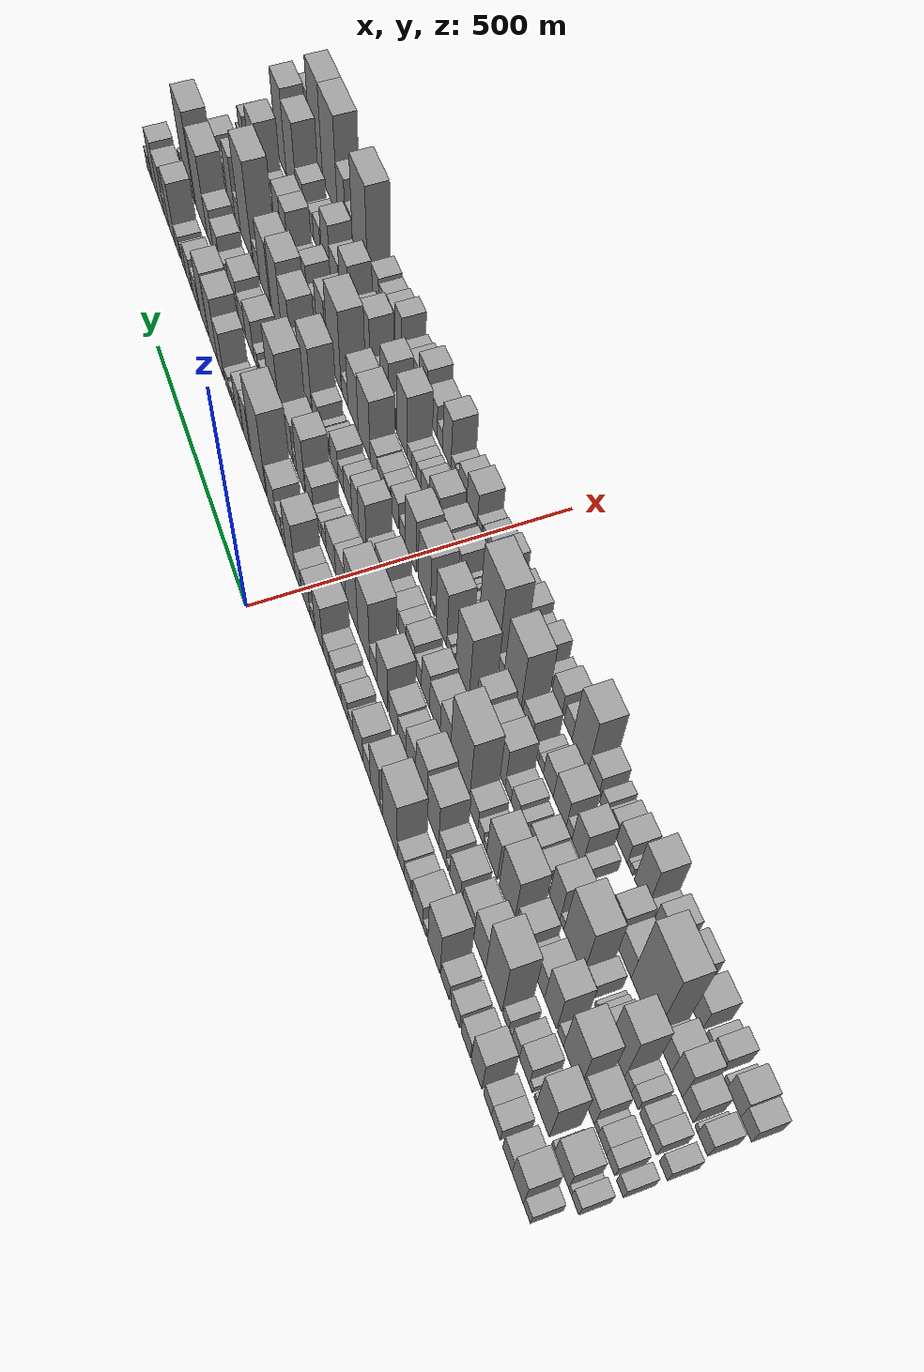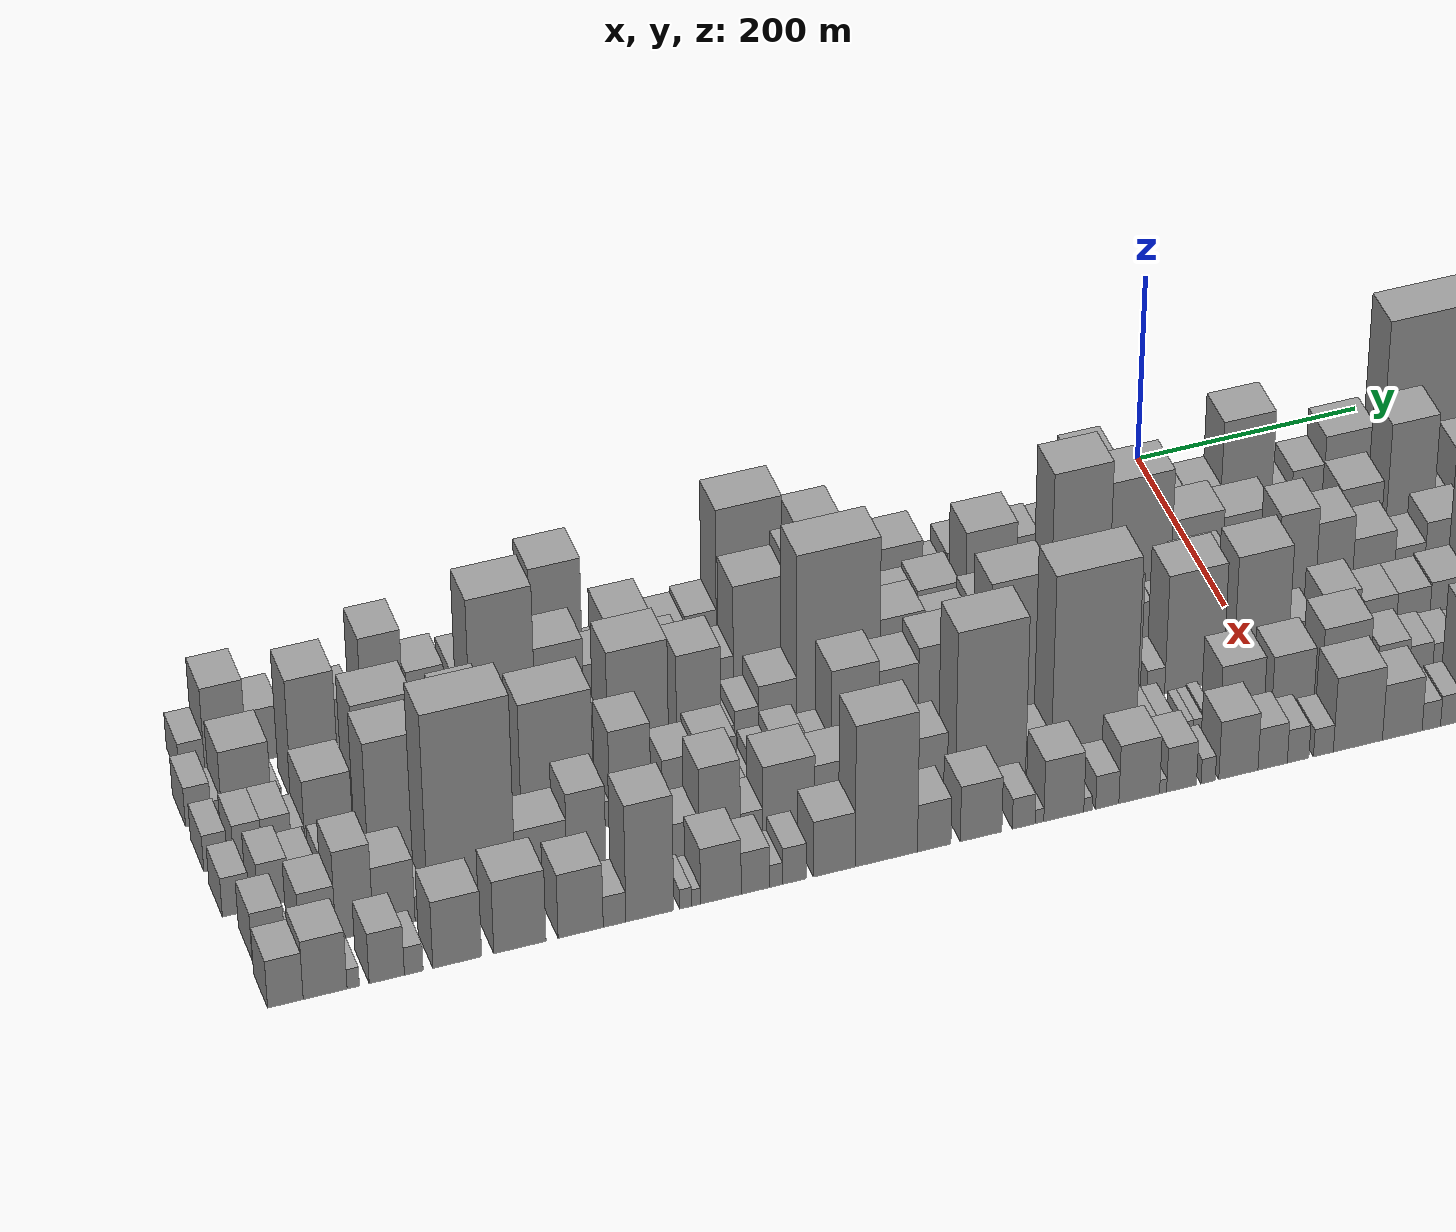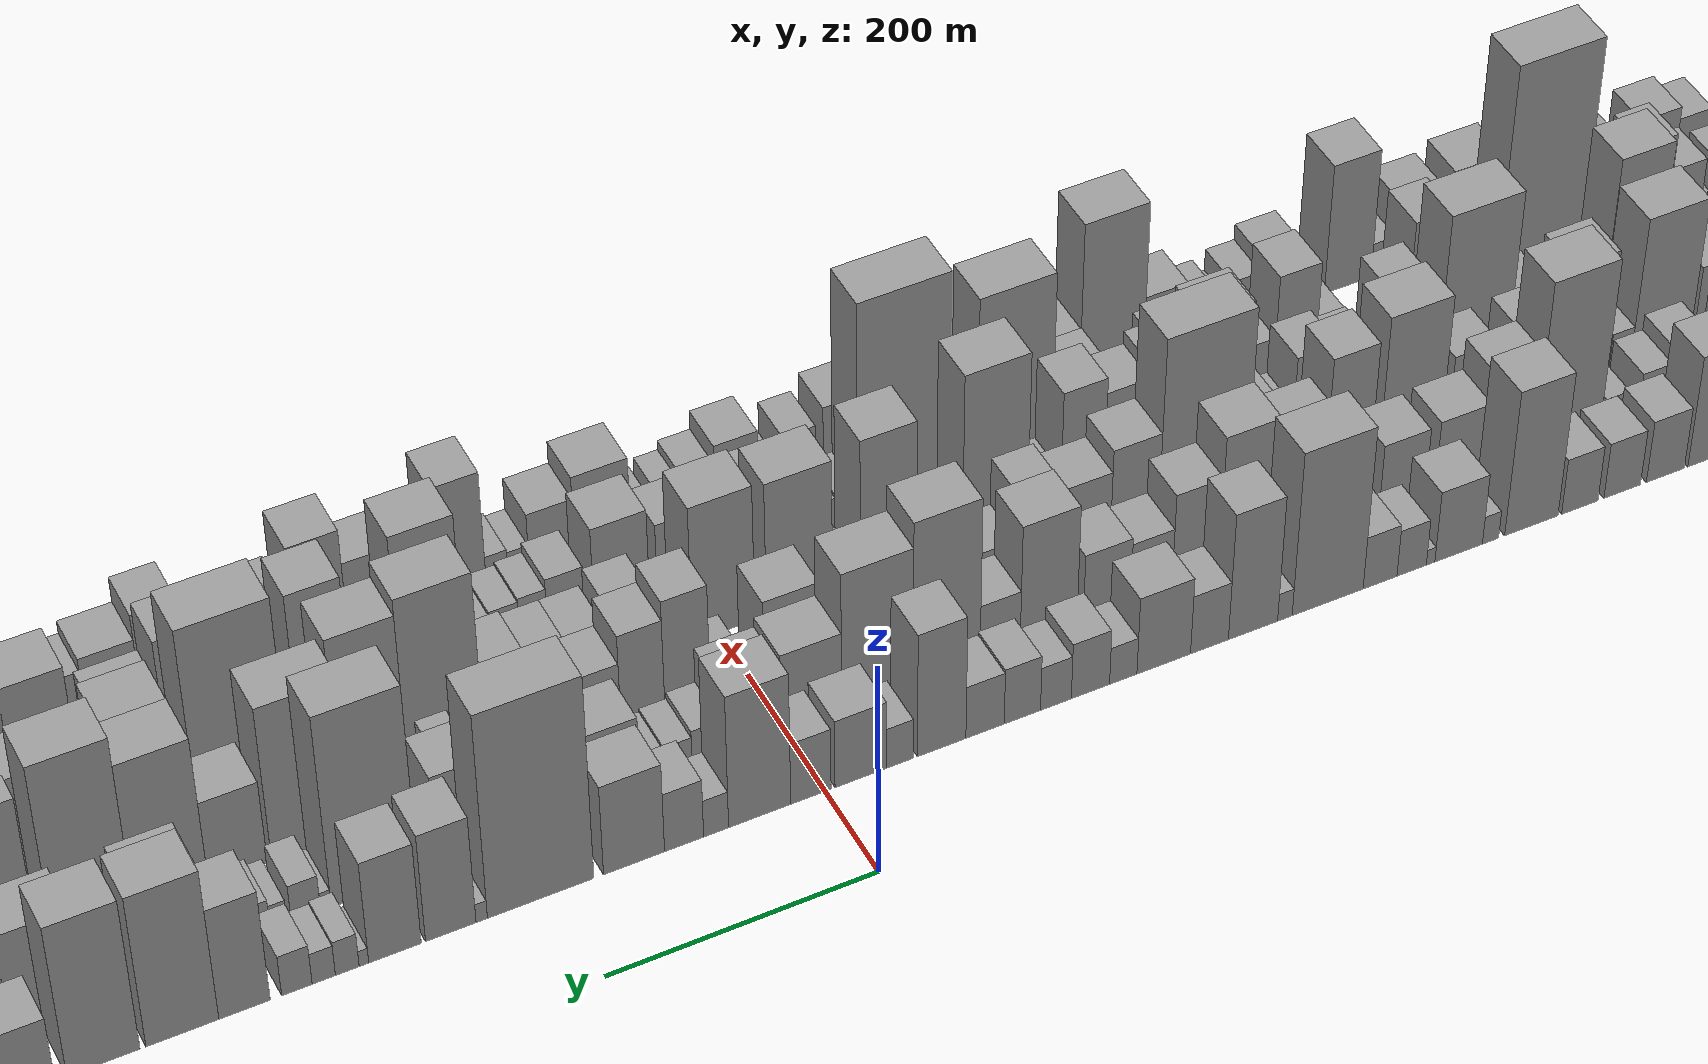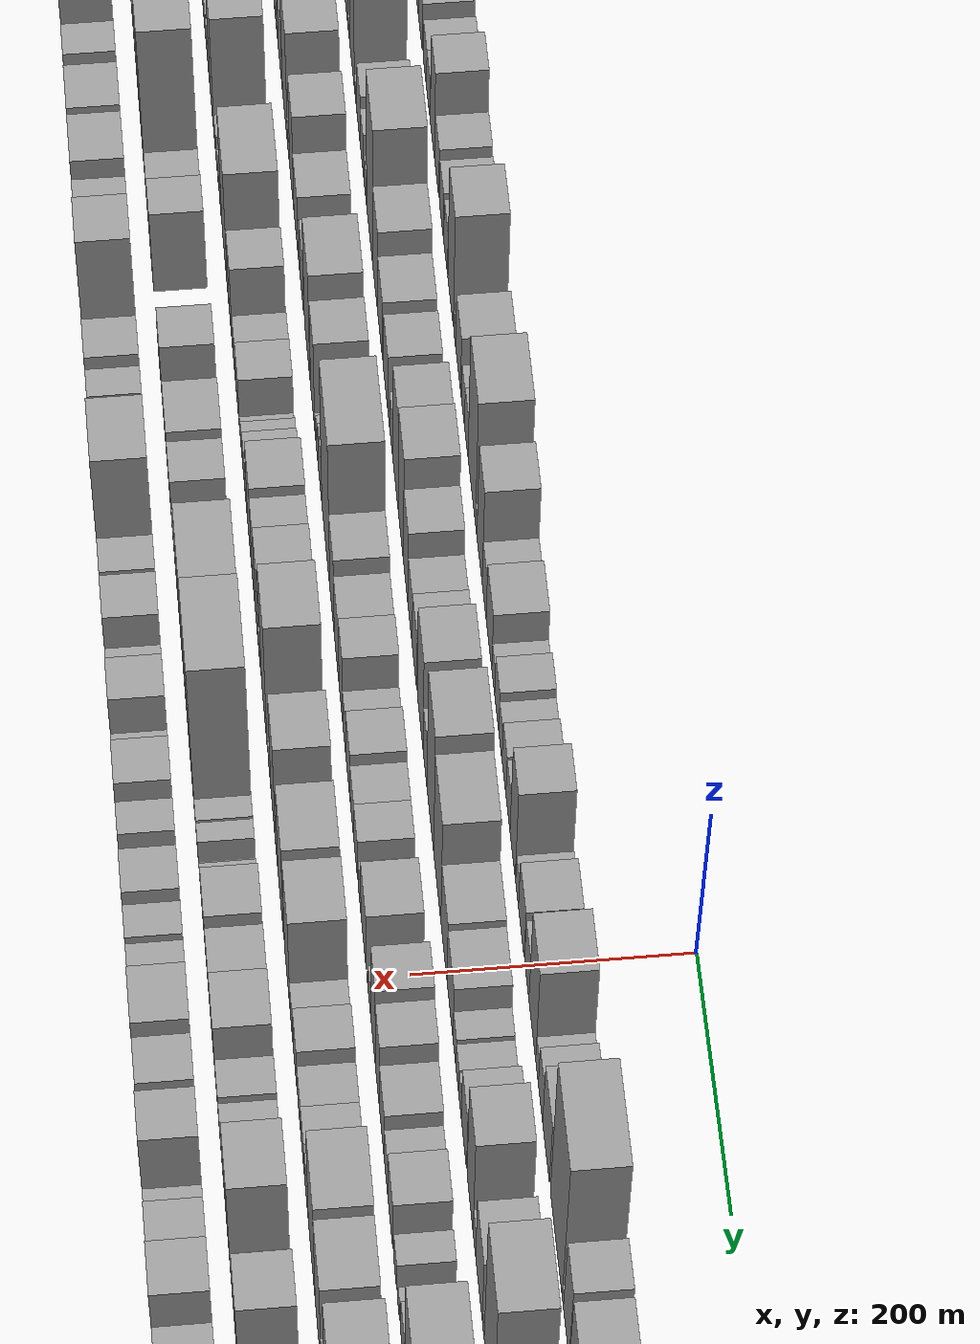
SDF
<sdf version="1.6">
 <world name="default">
  <scene>
   <sky><clouds><speed>12</speed></clouds></sky>
   <ambient>0.4 0.4 0.4 1</ambient>
   <background>0.7 0.7 0.7 1</background>
   <shadows>1</shadows>
  </scene>
  <gravity>0 0 -9.8066</gravity>
  <magnetic_field>6e-06 2.3e-05 -4.2e-05</magnetic_field>
  <physics default="0" name="default_physics" type="ode">
   <ode>
    <solver>
     <type>quick</type>
     <iters>10</iters>
     <sor>1.0</sor>
     <use_dynamic_moi_rescaling>0</use_dynamic_moi_rescaling>
    </solver>
    <constraints>
     <cfm>0</cfm>
     <erp>0.2</erp>
     <contact_max_correcting_vel>100</contact_max_correcting_vel>
     <contact_surface_layer>0.001</contact_surface_layer>
    </constraints>
   </ode>
   <max_step_size>0.004</max_step_size>
   <real_time_factor>1</real_time_factor>
   <real_time_update_rate>250</real_time_update_rate>
  </physics>
  <light name="sun" type="directional">
   <pose>0 0 10 0 0 0</pose>
   <diffuse>0.8 0.8 0.8 1</diffuse>
   <specular>0.2 0.2 0.2 1</specular>
   <attenuation>
    <range>1000</range>
    <constant>0.9</constant>
    <linear>0.01</linear>
    <quadratic>0.001</quadratic>
   </attenuation>
   <direction>-0.5 0.1 -0.9</direction>
  </light>
  <model name="building_1">
   <static>1</static>
   <pose>100.0000 -869.1969 0 0.000000 0.000000 0.000000</pose>
   <link name="link">
    <pose>0 0 19.50 0 0 0</pose>
    <collision name="collision"><geometry><box><size>40.0000 21.6063 39.0000</size></box></geometry></collision>
    <visual name="visual">
     <cast_shadows>0</cast_shadows>
     <geometry><box><size>40.0000 21.6063 39.0000</size></box></geometry>
     <material>
      <script>
       <uri>model://grey_wall/materials/scripts</uri>
       <uri>model://grey_wall/materials/textures</uri>
       <name>vrc/grey_wall</name>
      </script>
     </material>
    </visual>
   </link>
  </model>
  <model name="building_2">
   <static>1</static>
   <pose>100.0000 -840.7150 0 0.000000 0.000000 0.000000</pose>
   <link name="link">
    <pose>0 0 46.50 0 0 0</pose>
    <collision name="collision"><geometry><box><size>40.0000 35.3574 93.0000</size></box></geometry></collision>
    <visual name="visual">
     <cast_shadows>0</cast_shadows>
     <geometry><box><size>40.0000 35.3574 93.0000</size></box></geometry>
     <material>
      <script>
       <uri>model://grey_wall/materials/scripts</uri>
       <uri>model://grey_wall/materials/textures</uri>
       <name>vrc/grey_wall</name>
      </script>
     </material>
    </visual>
   </link>
  </model>
  <model name="building_3">
   <static>1</static>
   <pose>100.0000 -808.2781 0 0.000000 0.000000 0.000000</pose>
   <link name="link">
    <pose>0 0 28.50 0 0 0</pose>
    <collision name="collision"><geometry><box><size>40.0000 29.5164 57.0000</size></box></geometry></collision>
    <visual name="visual">
     <cast_shadows>0</cast_shadows>
     <geometry><box><size>40.0000 29.5164 57.0000</size></box></geometry>
     <material>
      <script>
       <uri>model://grey_wall/materials/scripts</uri>
       <uri>model://grey_wall/materials/textures</uri>
       <name>vrc/grey_wall</name>
      </script>
     </material>
    </visual>
   </link>
  </model>
  <model name="building_4">
   <static>1</static>
   <pose>100.0000 -771.2189 0 0.000000 0.000000 0.000000</pose>
   <link name="link">
    <pose>0 0 24.00 0 0 0</pose>
    <collision name="collision"><geometry><box><size>40.0000 28.6018 48.0000</size></box></geometry></collision>
    <visual name="visual">
     <cast_shadows>0</cast_shadows>
     <geometry><box><size>40.0000 28.6018 48.0000</size></box></geometry>
     <material>
      <script>
       <uri>model://grey_wall/materials/scripts</uri>
       <uri>model://grey_wall/materials/textures</uri>
       <name>vrc/grey_wall</name>
      </script>
     </material>
    </visual>
   </link>
  </model>
  <model name="building_5">
   <static>1</static>
   <pose>100.0000 -744.1187 0 0.000000 0.000000 0.000000</pose>
   <link name="link">
    <pose>0 0 24.00 0 0 0</pose>
    <collision name="collision"><geometry><box><size>40.0000 25.5986 48.0000</size></box></geometry></collision>
    <visual name="visual">
     <cast_shadows>0</cast_shadows>
     <geometry><box><size>40.0000 25.5986 48.0000</size></box></geometry>
     <material>
      <script>
       <uri>model://grey_wall/materials/scripts</uri>
       <uri>model://grey_wall/materials/textures</uri>
       <name>vrc/grey_wall</name>
      </script>
     </material>
    </visual>
   </link>
  </model>
  <model name="building_6">
   <static>1</static>
   <pose>100.0000 -707.5816 0 0.000000 0.000000 0.000000</pose>
   <link name="link">
    <pose>0 0 54.00 0 0 0</pose>
    <collision name="collision"><geometry><box><size>40.0000 35.4757 108.0000</size></box></geometry></collision>
    <visual name="visual">
     <cast_shadows>0</cast_shadows>
     <geometry><box><size>40.0000 35.4757 108.0000</size></box></geometry>
     <material>
      <script>
       <uri>model://grey_wall/materials/scripts</uri>
       <uri>model://grey_wall/materials/textures</uri>
       <name>vrc/grey_wall</name>
      </script>
     </material>
    </visual>
   </link>
  </model>
  <model name="building_7">
   <static>1</static>
   <pose>100.0000 -670.7844 0 0.000000 0.000000 0.000000</pose>
   <link name="link">
    <pose>0 0 30.00 0 0 0</pose>
    <collision name="collision"><geometry><box><size>40.0000 32.1186 60.0000</size></box></geometry></collision>
    <visual name="visual">
     <cast_shadows>0</cast_shadows>
     <geometry><box><size>40.0000 32.1186 60.0000</size></box></geometry>
     <material>
      <script>
       <uri>model://grey_wall/materials/scripts</uri>
       <uri>model://grey_wall/materials/textures</uri>
       <name>vrc/grey_wall</name>
      </script>
     </material>
    </visual>
   </link>
  </model>
  <model name="building_8">
   <static>1</static>
   <pose>100.0000 -634.3555 0 0.000000 0.000000 0.000000</pose>
   <link name="link">
    <pose>0 0 27.00 0 0 0</pose>
    <collision name="collision"><geometry><box><size>40.0000 30.7391 54.0000</size></box></geometry></collision>
    <visual name="visual">
     <cast_shadows>0</cast_shadows>
     <geometry><box><size>40.0000 30.7391 54.0000</size></box></geometry>
     <material>
      <script>
       <uri>model://grey_wall/materials/scripts</uri>
       <uri>model://grey_wall/materials/textures</uri>
       <name>vrc/grey_wall</name>
      </script>
     </material>
    </visual>
   </link>
  </model>
  <model name="building_9">
   <static>1</static>
   <pose>100.0000 -598.7894 0 0.000000 0.000000 0.000000</pose>
   <link name="link">
    <pose>0 0 27.00 0 0 0</pose>
    <collision name="collision"><geometry><box><size>40.0000 30.3932 54.0000</size></box></geometry></collision>
    <visual name="visual">
     <cast_shadows>0</cast_shadows>
     <geometry><box><size>40.0000 30.3932 54.0000</size></box></geometry>
     <material>
      <script>
       <uri>model://grey_wall/materials/scripts</uri>
       <uri>model://grey_wall/materials/textures</uri>
       <name>vrc/grey_wall</name>
      </script>
     </material>
    </visual>
   </link>
  </model>
  <model name="building_10">
   <static>1</static>
   <pose>100.0000 -558.4345 0 0.000000 0.000000 0.000000</pose>
   <link name="link">
    <pose>0 0 70.50 0 0 0</pose>
    <collision name="collision"><geometry><box><size>40.0000 44.3166 141.0000</size></box></geometry></collision>
    <visual name="visual">
     <cast_shadows>0</cast_shadows>
     <geometry><box><size>40.0000 44.3166 141.0000</size></box></geometry>
     <material>
      <script>
       <uri>model://grey_wall/materials/scripts</uri>
       <uri>model://grey_wall/materials/textures</uri>
       <name>vrc/grey_wall</name>
      </script>
     </material>
    </visual>
   </link>
  </model>
  <model name="building_11">
   <static>1</static>
   <pose>100.0000 -524.5641 0 0.000000 0.000000 0.000000</pose>
   <link name="link">
    <pose>0 0 13.50 0 0 0</pose>
    <collision name="collision"><geometry><box><size>40.0000 13.4241 27.0000</size></box></geometry></collision>
    <visual name="visual">
     <cast_shadows>0</cast_shadows>
     <geometry><box><size>40.0000 13.4241 27.0000</size></box></geometry>
     <material>
      <script>
       <uri>model://grey_wall/materials/scripts</uri>
       <uri>model://grey_wall/materials/textures</uri>
       <name>vrc/grey_wall</name>
      </script>
     </material>
    </visual>
   </link>
  </model>
  <model name="building_12">
   <static>1</static>
   <pose>100.0000 -498.3370 0 0.000000 0.000000 0.000000</pose>
   <link name="link">
    <pose>0 0 34.50 0 0 0</pose>
    <collision name="collision"><geometry><box><size>40.0000 39.0302 69.0000</size></box></geometry></collision>
    <visual name="visual">
     <cast_shadows>0</cast_shadows>
     <geometry><box><size>40.0000 39.0302 69.0000</size></box></geometry>
     <material>
      <script>
       <uri>model://grey_wall/materials/scripts</uri>
       <uri>model://grey_wall/materials/textures</uri>
       <name>vrc/grey_wall</name>
      </script>
     </material>
    </visual>
   </link>
  </model>
  <model name="building_13">
   <static>1</static>
   <pose>100.0000 -475.2982 0 0.000000 0.000000 0.000000</pose>
   <link name="link">
    <pose>0 0 7.50 0 0 0</pose>
    <collision name="collision"><geometry><box><size>40.0000 7.0475 15.0000</size></box></geometry></collision>
    <visual name="visual">
     <cast_shadows>0</cast_shadows>
     <geometry><box><size>40.0000 7.0475 15.0000</size></box></geometry>
     <material>
      <script>
       <uri>model://grey_wall/materials/scripts</uri>
       <uri>model://grey_wall/materials/textures</uri>
       <name>vrc/grey_wall</name>
      </script>
     </material>
    </visual>
   </link>
  </model>
  <model name="building_14">
   <static>1</static>
   <pose>100.0000 -459.7862 0 0.000000 0.000000 0.000000</pose>
   <link name="link">
    <pose>0 0 22.50 0 0 0</pose>
    <collision name="collision"><geometry><box><size>40.0000 23.9765 45.0000</size></box></geometry></collision>
    <visual name="visual">
     <cast_shadows>0</cast_shadows>
     <geometry><box><size>40.0000 23.9765 45.0000</size></box></geometry>
     <material>
      <script>
       <uri>model://grey_wall/materials/scripts</uri>
       <uri>model://grey_wall/materials/textures</uri>
       <name>vrc/grey_wall</name>
      </script>
     </material>
    </visual>
   </link>
  </model>
  <model name="building_15">
   <static>1</static>
   <pose>100.0000 -434.0678 0 0.000000 0.000000 0.000000</pose>
   <link name="link">
    <pose>0 0 25.50 0 0 0</pose>
    <collision name="collision"><geometry><box><size>40.0000 27.4603 51.0000</size></box></geometry></collision>
    <visual name="visual">
     <cast_shadows>0</cast_shadows>
     <geometry><box><size>40.0000 27.4603 51.0000</size></box></geometry>
     <material>
      <script>
       <uri>model://grey_wall/materials/scripts</uri>
       <uri>model://grey_wall/materials/textures</uri>
       <name>vrc/grey_wall</name>
      </script>
     </material>
    </visual>
   </link>
  </model>
  <model name="building_16">
   <static>1</static>
   <pose>100.0000 -391.7136 0 0.000000 0.000000 0.000000</pose>
   <link name="link">
    <pose>0 0 79.50 0 0 0</pose>
    <collision name="collision"><geometry><box><size>40.0000 57.2482 159.0000</size></box></geometry></collision>
    <visual name="visual">
     <cast_shadows>0</cast_shadows>
     <geometry><box><size>40.0000 57.2482 159.0000</size></box></geometry>
     <material>
      <script>
       <uri>model://grey_wall/materials/scripts</uri>
       <uri>model://grey_wall/materials/textures</uri>
       <name>vrc/grey_wall</name>
      </script>
     </material>
    </visual>
   </link>
  </model>
  <model name="building_17">
   <static>1</static>
   <pose>100.0000 -357.2260 0 0.000000 0.000000 0.000000</pose>
   <link name="link">
    <pose>0 0 13.50 0 0 0</pose>
    <collision name="collision"><geometry><box><size>40.0000 11.7269 27.0000</size></box></geometry></collision>
    <visual name="visual">
     <cast_shadows>0</cast_shadows>
     <geometry><box><size>40.0000 11.7269 27.0000</size></box></geometry>
     <material>
      <script>
       <uri>model://grey_wall/materials/scripts</uri>
       <uri>model://grey_wall/materials/textures</uri>
       <name>vrc/grey_wall</name>
      </script>
     </material>
    </visual>
   </link>
  </model>
  <model name="building_18">
   <static>1</static>
   <pose>100.0000 -331.7158 0 0.000000 0.000000 0.000000</pose>
   <link name="link">
    <pose>0 0 61.50 0 0 0</pose>
    <collision name="collision"><geometry><box><size>40.0000 39.2936 123.0000</size></box></geometry></collision>
    <visual name="visual">
     <cast_shadows>0</cast_shadows>
     <geometry><box><size>40.0000 39.2936 123.0000</size></box></geometry>
     <material>
      <script>
       <uri>model://grey_wall/materials/scripts</uri>
       <uri>model://grey_wall/materials/textures</uri>
       <name>vrc/grey_wall</name>
      </script>
     </material>
    </visual>
   </link>
  </model>
  <model name="building_19">
   <static>1</static>
   <pose>100.0000 -297.0438 0 0.000000 0.000000 0.000000</pose>
   <link name="link">
    <pose>0 0 28.50 0 0 0</pose>
    <collision name="collision"><geometry><box><size>40.0000 30.0505 57.0000</size></box></geometry></collision>
    <visual name="visual">
     <cast_shadows>0</cast_shadows>
     <geometry><box><size>40.0000 30.0505 57.0000</size></box></geometry>
     <material>
      <script>
       <uri>model://grey_wall/materials/scripts</uri>
       <uri>model://grey_wall/materials/textures</uri>
       <name>vrc/grey_wall</name>
      </script>
     </material>
    </visual>
   </link>
  </model>
  <model name="building_20">
   <static>1</static>
   <pose>100.0000 -260.8742 0 0.000000 0.000000 0.000000</pose>
   <link name="link">
    <pose>0 0 37.50 0 0 0</pose>
    <collision name="collision"><geometry><box><size>40.0000 42.2886 75.0000</size></box></geometry></collision>
    <visual name="visual">
     <cast_shadows>0</cast_shadows>
     <geometry><box><size>40.0000 42.2886 75.0000</size></box></geometry>
     <material>
      <script>
       <uri>model://grey_wall/materials/scripts</uri>
       <uri>model://grey_wall/materials/textures</uri>
       <name>vrc/grey_wall</name>
      </script>
     </material>
    </visual>
   </link>
  </model>
  <model name="building_21">
   <static>1</static>
   <pose>100.0000 -228.9998 0 0.000000 0.000000 0.000000</pose>
   <link name="link">
    <pose>0 0 18.00 0 0 0</pose>
    <collision name="collision"><geometry><box><size>40.0000 21.4602 36.0000</size></box></geometry></collision>
    <visual name="visual">
     <cast_shadows>0</cast_shadows>
     <geometry><box><size>40.0000 21.4602 36.0000</size></box></geometry>
     <material>
      <script>
       <uri>model://grey_wall/materials/scripts</uri>
       <uri>model://grey_wall/materials/textures</uri>
       <name>vrc/grey_wall</name>
      </script>
     </material>
    </visual>
   </link>
  </model>
  <model name="building_22">
   <static>1</static>
   <pose>100.0000 -203.3418 0 0.000000 0.000000 0.000000</pose>
   <link name="link">
    <pose>0 0 27.00 0 0 0</pose>
    <collision name="collision"><geometry><box><size>40.0000 29.8557 54.0000</size></box></geometry></collision>
    <visual name="visual">
     <cast_shadows>0</cast_shadows>
     <geometry><box><size>40.0000 29.8557 54.0000</size></box></geometry>
     <material>
      <script>
       <uri>model://grey_wall/materials/scripts</uri>
       <uri>model://grey_wall/materials/textures</uri>
       <name>vrc/grey_wall</name>
      </script>
     </material>
    </visual>
   </link>
  </model>
  <model name="building_23">
   <static>1</static>
   <pose>100.0000 -176.4392 0 0.000000 0.000000 0.000000</pose>
   <link name="link">
    <pose>0 0 21.00 0 0 0</pose>
    <collision name="collision"><geometry><box><size>40.0000 23.9494 42.0000</size></box></geometry></collision>
    <visual name="visual">
     <cast_shadows>0</cast_shadows>
     <geometry><box><size>40.0000 23.9494 42.0000</size></box></geometry>
     <material>
      <script>
       <uri>model://grey_wall/materials/scripts</uri>
       <uri>model://grey_wall/materials/textures</uri>
       <name>vrc/grey_wall</name>
      </script>
     </material>
    </visual>
   </link>
  </model>
  <model name="building_24">
   <static>1</static>
   <pose>100.0000 -150.4346 0 0.000000 0.000000 0.000000</pose>
   <link name="link">
    <pose>0 0 27.00 0 0 0</pose>
    <collision name="collision"><geometry><box><size>40.0000 28.0599 54.0000</size></box></geometry></collision>
    <visual name="visual">
     <cast_shadows>0</cast_shadows>
     <geometry><box><size>40.0000 28.0599 54.0000</size></box></geometry>
     <material>
      <script>
       <uri>model://grey_wall/materials/scripts</uri>
       <uri>model://grey_wall/materials/textures</uri>
       <name>vrc/grey_wall</name>
      </script>
     </material>
    </visual>
   </link>
  </model>
  <model name="building_25">
   <static>1</static>
   <pose>100.0000 -121.6439 0 0.000000 0.000000 0.000000</pose>
   <link name="link">
    <pose>0 0 25.50 0 0 0</pose>
    <collision name="collision"><geometry><box><size>40.0000 29.5215 51.0000</size></box></geometry></collision>
    <visual name="visual">
     <cast_shadows>0</cast_shadows>
     <geometry><box><size>40.0000 29.5215 51.0000</size></box></geometry>
     <material>
      <script>
       <uri>model://grey_wall/materials/scripts</uri>
       <uri>model://grey_wall/materials/textures</uri>
       <name>vrc/grey_wall</name>
      </script>
     </material>
    </visual>
   </link>
  </model>
  <model name="building_26">
   <static>1</static>
   <pose>100.0000 -88.3170 0 0.000000 0.000000 0.000000</pose>
   <link name="link">
    <pose>0 0 60.00 0 0 0</pose>
    <collision name="collision"><geometry><box><size>40.0000 37.1322 120.0000</size></box></geometry></collision>
    <visual name="visual">
     <cast_shadows>0</cast_shadows>
     <geometry><box><size>40.0000 37.1322 120.0000</size></box></geometry>
     <material>
      <script>
       <uri>model://grey_wall/materials/scripts</uri>
       <uri>model://grey_wall/materials/textures</uri>
       <name>vrc/grey_wall</name>
      </script>
     </material>
    </visual>
   </link>
  </model>
  <model name="building_27">
   <static>1</static>
   <pose>100.0000 -56.5800 0 0.000000 0.000000 0.000000</pose>
   <link name="link">
    <pose>0 0 19.50 0 0 0</pose>
    <collision name="collision"><geometry><box><size>40.0000 20.3419 39.0000</size></box></geometry></collision>
    <visual name="visual">
     <cast_shadows>0</cast_shadows>
     <geometry><box><size>40.0000 20.3419 39.0000</size></box></geometry>
     <material>
      <script>
       <uri>model://grey_wall/materials/scripts</uri>
       <uri>model://grey_wall/materials/textures</uri>
       <name>vrc/grey_wall</name>
      </script>
     </material>
    </visual>
   </link>
  </model>
  <model name="building_28">
   <static>1</static>
   <pose>100.0000 -26.8657 0 0.000000 0.000000 0.000000</pose>
   <link name="link">
    <pose>0 0 33.00 0 0 0</pose>
    <collision name="collision"><geometry><box><size>40.0000 39.0865 66.0000</size></box></geometry></collision>
    <visual name="visual">
     <cast_shadows>0</cast_shadows>
     <geometry><box><size>40.0000 39.0865 66.0000</size></box></geometry>
     <material>
      <script>
       <uri>model://grey_wall/materials/scripts</uri>
       <uri>model://grey_wall/materials/textures</uri>
       <name>vrc/grey_wall</name>
      </script>
     </material>
    </visual>
   </link>
  </model>
  <model name="building_29">
   <static>1</static>
   <pose>100.0000 10.8078 0 0.000000 0.000000 0.000000</pose>
   <link name="link">
    <pose>0 0 30.00 0 0 0</pose>
    <collision name="collision"><geometry><box><size>40.0000 30.2605 60.0000</size></box></geometry></collision>
    <visual name="visual">
     <cast_shadows>0</cast_shadows>
     <geometry><box><size>40.0000 30.2605 60.0000</size></box></geometry>
     <material>
      <script>
       <uri>model://grey_wall/materials/scripts</uri>
       <uri>model://grey_wall/materials/textures</uri>
       <name>vrc/grey_wall</name>
      </script>
     </material>
    </visual>
   </link>
  </model>
  <model name="building_30">
   <static>1</static>
   <pose>100.0000 49.1563 0 0.000000 0.000000 0.000000</pose>
   <link name="link">
    <pose>0 0 64.50 0 0 0</pose>
    <collision name="collision"><geometry><box><size>40.0000 46.4365 129.0000</size></box></geometry></collision>
    <visual name="visual">
     <cast_shadows>0</cast_shadows>
     <geometry><box><size>40.0000 46.4365 129.0000</size></box></geometry>
     <material>
      <script>
       <uri>model://grey_wall/materials/scripts</uri>
       <uri>model://grey_wall/materials/textures</uri>
       <name>vrc/grey_wall</name>
      </script>
     </material>
    </visual>
   </link>
  </model>
  <model name="building_31">
   <static>1</static>
   <pose>100.0000 81.6413 0 0.000000 0.000000 0.000000</pose>
   <link name="link">
    <pose>0 0 18.00 0 0 0</pose>
    <collision name="collision"><geometry><box><size>40.0000 18.5334 36.0000</size></box></geometry></collision>
    <visual name="visual">
     <cast_shadows>0</cast_shadows>
     <geometry><box><size>40.0000 18.5334 36.0000</size></box></geometry>
     <material>
      <script>
       <uri>model://grey_wall/materials/scripts</uri>
       <uri>model://grey_wall/materials/textures</uri>
       <name>vrc/grey_wall</name>
      </script>
     </material>
    </visual>
   </link>
  </model>
  <model name="building_32">
   <static>1</static>
   <pose>100.0000 105.3341 0 0.000000 0.000000 0.000000</pose>
   <link name="link">
    <pose>0 0 28.50 0 0 0</pose>
    <collision name="collision"><geometry><box><size>40.0000 28.8521 57.0000</size></box></geometry></collision>
    <visual name="visual">
     <cast_shadows>0</cast_shadows>
     <geometry><box><size>40.0000 28.8521 57.0000</size></box></geometry>
     <material>
      <script>
       <uri>model://grey_wall/materials/scripts</uri>
       <uri>model://grey_wall/materials/textures</uri>
       <name>vrc/grey_wall</name>
      </script>
     </material>
    </visual>
   </link>
  </model>
  <model name="building_33">
   <static>1</static>
   <pose>100.0000 142.1767 0 0.000000 0.000000 0.000000</pose>
   <link name="link">
    <pose>0 0 43.50 0 0 0</pose>
    <collision name="collision"><geometry><box><size>40.0000 44.8332 87.0000</size></box></geometry></collision>
    <visual name="visual">
     <cast_shadows>0</cast_shadows>
     <geometry><box><size>40.0000 44.8332 87.0000</size></box></geometry>
     <material>
      <script>
       <uri>model://grey_wall/materials/scripts</uri>
       <uri>model://grey_wall/materials/textures</uri>
       <name>vrc/grey_wall</name>
      </script>
     </material>
    </visual>
   </link>
  </model>
  <model name="building_34">
   <static>1</static>
   <pose>100.0000 210.1831 0 0.000000 0.000000 0.000000</pose>
   <link name="link">
    <pose>0 0 99.00 0 0 0</pose>
    <collision name="collision"><geometry><box><size>40.0000 77.1794 198.0000</size></box></geometry></collision>
    <visual name="visual">
     <cast_shadows>0</cast_shadows>
     <geometry><box><size>40.0000 77.1794 198.0000</size></box></geometry>
     <material>
      <script>
       <uri>model://grey_wall/materials/scripts</uri>
       <uri>model://grey_wall/materials/textures</uri>
       <name>vrc/grey_wall</name>
      </script>
     </material>
    </visual>
   </link>
  </model>
  <model name="building_35">
   <static>1</static>
   <pose>100.0000 252.8782 0 0.000000 0.000000 0.000000</pose>
   <link name="link">
    <pose>0 0 9.00 0 0 0</pose>
    <collision name="collision"><geometry><box><size>40.0000 8.2108 18.0000</size></box></geometry></collision>
    <visual name="visual">
     <cast_shadows>0</cast_shadows>
     <geometry><box><size>40.0000 8.2108 18.0000</size></box></geometry>
     <material>
      <script>
       <uri>model://grey_wall/materials/scripts</uri>
       <uri>model://grey_wall/materials/textures</uri>
       <name>vrc/grey_wall</name>
      </script>
     </material>
    </visual>
   </link>
  </model>
  <model name="building_36">
   <static>1</static>
   <pose>100.0000 275.0869 0 0.000000 0.000000 0.000000</pose>
   <link name="link">
    <pose>0 0 52.50 0 0 0</pose>
    <collision name="collision"><geometry><box><size>40.0000 36.2067 105.0000</size></box></geometry></collision>
    <visual name="visual">
     <cast_shadows>0</cast_shadows>
     <geometry><box><size>40.0000 36.2067 105.0000</size></box></geometry>
     <material>
      <script>
       <uri>model://grey_wall/materials/scripts</uri>
       <uri>model://grey_wall/materials/textures</uri>
       <name>vrc/grey_wall</name>
      </script>
     </material>
    </visual>
   </link>
  </model>
  <model name="building_37">
   <static>1</static>
   <pose>100.0000 314.8873 0 0.000000 0.000000 0.000000</pose>
   <link name="link">
    <pose>0 0 49.50 0 0 0</pose>
    <collision name="collision"><geometry><box><size>40.0000 37.3941 99.0000</size></box></geometry></collision>
    <visual name="visual">
     <cast_shadows>0</cast_shadows>
     <geometry><box><size>40.0000 37.3941 99.0000</size></box></geometry>
     <material>
      <script>
       <uri>model://grey_wall/materials/scripts</uri>
       <uri>model://grey_wall/materials/textures</uri>
       <name>vrc/grey_wall</name>
      </script>
     </material>
    </visual>
   </link>
  </model>
  <model name="building_38">
   <static>1</static>
   <pose>100.0000 336.9596 0 0.000000 0.000000 0.000000</pose>
   <link name="link">
    <pose>0 0 7.50 0 0 0</pose>
    <collision name="collision"><geometry><box><size>40.0000 6.7504 15.0000</size></box></geometry></collision>
    <visual name="visual">
     <cast_shadows>0</cast_shadows>
     <geometry><box><size>40.0000 6.7504 15.0000</size></box></geometry>
     <material>
      <script>
       <uri>model://grey_wall/materials/scripts</uri>
       <uri>model://grey_wall/materials/textures</uri>
       <name>vrc/grey_wall</name>
      </script>
     </material>
    </visual>
   </link>
  </model>
  <model name="building_39">
   <static>1</static>
   <pose>100.0000 348.7307 0 0.000000 0.000000 0.000000</pose>
   <link name="link">
    <pose>0 0 16.50 0 0 0</pose>
    <collision name="collision"><geometry><box><size>40.0000 16.7919 33.0000</size></box></geometry></collision>
    <visual name="visual">
     <cast_shadows>0</cast_shadows>
     <geometry><box><size>40.0000 16.7919 33.0000</size></box></geometry>
     <material>
      <script>
       <uri>model://grey_wall/materials/scripts</uri>
       <uri>model://grey_wall/materials/textures</uri>
       <name>vrc/grey_wall</name>
      </script>
     </material>
    </visual>
   </link>
  </model>
  <model name="building_40">
   <static>1</static>
   <pose>100.0000 365.3119 0 0.000000 0.000000 0.000000</pose>
   <link name="link">
    <pose>0 0 15.00 0 0 0</pose>
    <collision name="collision"><geometry><box><size>40.0000 16.3705 30.0000</size></box></geometry></collision>
    <visual name="visual">
     <cast_shadows>0</cast_shadows>
     <geometry><box><size>40.0000 16.3705 30.0000</size></box></geometry>
     <material>
      <script>
       <uri>model://grey_wall/materials/scripts</uri>
       <uri>model://grey_wall/materials/textures</uri>
       <name>vrc/grey_wall</name>
      </script>
     </material>
    </visual>
   </link>
  </model>
  <model name="building_41">
   <static>1</static>
   <pose>100.0000 384.2088 0 0.000000 0.000000 0.000000</pose>
   <link name="link">
    <pose>0 0 19.50 0 0 0</pose>
    <collision name="collision"><geometry><box><size>40.0000 21.4233 39.0000</size></box></geometry></collision>
    <visual name="visual">
     <cast_shadows>0</cast_shadows>
     <geometry><box><size>40.0000 21.4233 39.0000</size></box></geometry>
     <material>
      <script>
       <uri>model://grey_wall/materials/scripts</uri>
       <uri>model://grey_wall/materials/textures</uri>
       <name>vrc/grey_wall</name>
      </script>
     </material>
    </visual>
   </link>
  </model>
  <model name="building_42">
   <static>1</static>
   <pose>100.0000 420.8297 0 0.000000 0.000000 0.000000</pose>
   <link name="link">
    <pose>0 0 54.00 0 0 0</pose>
    <collision name="collision"><geometry><box><size>40.0000 35.8184 108.0000</size></box></geometry></collision>
    <visual name="visual">
     <cast_shadows>0</cast_shadows>
     <geometry><box><size>40.0000 35.8184 108.0000</size></box></geometry>
     <material>
      <script>
       <uri>model://grey_wall/materials/scripts</uri>
       <uri>model://grey_wall/materials/textures</uri>
       <name>vrc/grey_wall</name>
      </script>
     </material>
    </visual>
   </link>
  </model>
  <model name="building_43">
   <static>1</static>
   <pose>100.0000 463.9994 0 0.000000 0.000000 0.000000</pose>
   <link name="link">
    <pose>0 0 73.50 0 0 0</pose>
    <collision name="collision"><geometry><box><size>40.0000 50.5210 147.0000</size></box></geometry></collision>
    <visual name="visual">
     <cast_shadows>0</cast_shadows>
     <geometry><box><size>40.0000 50.5210 147.0000</size></box></geometry>
     <material>
      <script>
       <uri>model://grey_wall/materials/scripts</uri>
       <uri>model://grey_wall/materials/textures</uri>
       <name>vrc/grey_wall</name>
      </script>
     </material>
    </visual>
   </link>
  </model>
  <model name="building_44">
   <static>1</static>
   <pose>100.0000 518.3641 0 0.000000 0.000000 0.000000</pose>
   <link name="link">
    <pose>0 0 73.50 0 0 0</pose>
    <collision name="collision"><geometry><box><size>40.0000 50.2085 147.0000</size></box></geometry></collision>
    <visual name="visual">
     <cast_shadows>0</cast_shadows>
     <geometry><box><size>40.0000 50.2085 147.0000</size></box></geometry>
     <material>
      <script>
       <uri>model://grey_wall/materials/scripts</uri>
       <uri>model://grey_wall/materials/textures</uri>
       <name>vrc/grey_wall</name>
      </script>
     </material>
    </visual>
   </link>
  </model>
  <model name="building_45">
   <static>1</static>
   <pose>100.0000 569.8008 0 0.000000 0.000000 0.000000</pose>
   <link name="link">
    <pose>0 0 31.50 0 0 0</pose>
    <collision name="collision"><geometry><box><size>40.0000 36.6649 63.0000</size></box></geometry></collision>
    <visual name="visual">
     <cast_shadows>0</cast_shadows>
     <geometry><box><size>40.0000 36.6649 63.0000</size></box></geometry>
     <material>
      <script>
       <uri>model://grey_wall/materials/scripts</uri>
       <uri>model://grey_wall/materials/textures</uri>
       <name>vrc/grey_wall</name>
      </script>
     </material>
    </visual>
   </link>
  </model>
  <model name="building_46">
   <static>1</static>
   <pose>100.0000 612.7377 0 0.000000 0.000000 0.000000</pose>
   <link name="link">
    <pose>0 0 37.50 0 0 0</pose>
    <collision name="collision"><geometry><box><size>40.0000 39.2089 75.0000</size></box></geometry></collision>
    <visual name="visual">
     <cast_shadows>0</cast_shadows>
     <geometry><box><size>40.0000 39.2089 75.0000</size></box></geometry>
     <material>
      <script>
       <uri>model://grey_wall/materials/scripts</uri>
       <uri>model://grey_wall/materials/textures</uri>
       <name>vrc/grey_wall</name>
      </script>
     </material>
    </visual>
   </link>
  </model>
  <model name="building_47">
   <static>1</static>
   <pose>100.0000 645.6110 0 0.000000 0.000000 0.000000</pose>
   <link name="link">
    <pose>0 0 25.50 0 0 0</pose>
    <collision name="collision"><geometry><box><size>40.0000 26.5376 51.0000</size></box></geometry></collision>
    <visual name="visual">
     <cast_shadows>0</cast_shadows>
     <geometry><box><size>40.0000 26.5376 51.0000</size></box></geometry>
     <material>
      <script>
       <uri>model://grey_wall/materials/scripts</uri>
       <uri>model://grey_wall/materials/textures</uri>
       <name>vrc/grey_wall</name>
      </script>
     </material>
    </visual>
   </link>
  </model>
  <model name="building_48">
   <static>1</static>
   <pose>100.0000 683.8776 0 0.000000 0.000000 0.000000</pose>
   <link name="link">
    <pose>0 0 25.50 0 0 0</pose>
    <collision name="collision"><geometry><box><size>40.0000 29.9957 51.0000</size></box></geometry></collision>
    <visual name="visual">
     <cast_shadows>0</cast_shadows>
     <geometry><box><size>40.0000 29.9957 51.0000</size></box></geometry>
     <material>
      <script>
       <uri>model://grey_wall/materials/scripts</uri>
       <uri>model://grey_wall/materials/textures</uri>
       <name>vrc/grey_wall</name>
      </script>
     </material>
    </visual>
   </link>
  </model>
  <model name="building_49">
   <static>1</static>
   <pose>100.0000 720.3638 0 0.000000 0.000000 0.000000</pose>
   <link name="link">
    <pose>0 0 70.50 0 0 0</pose>
    <collision name="collision"><geometry><box><size>40.0000 42.9768 141.0000</size></box></geometry></collision>
    <visual name="visual">
     <cast_shadows>0</cast_shadows>
     <geometry><box><size>40.0000 42.9768 141.0000</size></box></geometry>
     <material>
      <script>
       <uri>model://grey_wall/materials/scripts</uri>
       <uri>model://grey_wall/materials/textures</uri>
       <name>vrc/grey_wall</name>
      </script>
     </material>
    </visual>
   </link>
  </model>
  <model name="building_50">
   <static>1</static>
   <pose>100.0000 757.2081 0 0.000000 0.000000 0.000000</pose>
   <link name="link">
    <pose>0 0 27.00 0 0 0</pose>
    <collision name="collision"><geometry><box><size>40.0000 30.7118 54.0000</size></box></geometry></collision>
    <visual name="visual">
     <cast_shadows>0</cast_shadows>
     <geometry><box><size>40.0000 30.7118 54.0000</size></box></geometry>
     <material>
      <script>
       <uri>model://grey_wall/materials/scripts</uri>
       <uri>model://grey_wall/materials/textures</uri>
       <name>vrc/grey_wall</name>
      </script>
     </material>
    </visual>
   </link>
  </model>
  <model name="building_51">
   <static>1</static>
   <pose>100.0000 793.3910 0 0.000000 0.000000 0.000000</pose>
   <link name="link">
    <pose>0 0 55.50 0 0 0</pose>
    <collision name="collision"><geometry><box><size>40.0000 41.6539 111.0000</size></box></geometry></collision>
    <visual name="visual">
     <cast_shadows>0</cast_shadows>
     <geometry><box><size>40.0000 41.6539 111.0000</size></box></geometry>
     <material>
      <script>
       <uri>model://grey_wall/materials/scripts</uri>
       <uri>model://grey_wall/materials/textures</uri>
       <name>vrc/grey_wall</name>
      </script>
     </material>
    </visual>
   </link>
  </model>
  <model name="building_52">
   <static>1</static>
   <pose>100.0000 834.1180 0 0.000000 0.000000 0.000000</pose>
   <link name="link">
    <pose>0 0 63.00 0 0 0</pose>
    <collision name="collision"><geometry><box><size>40.0000 39.8001 126.0000</size></box></geometry></collision>
    <visual name="visual">
     <cast_shadows>0</cast_shadows>
     <geometry><box><size>40.0000 39.8001 126.0000</size></box></geometry>
     <material>
      <script>
       <uri>model://grey_wall/materials/scripts</uri>
       <uri>model://grey_wall/materials/textures</uri>
       <name>vrc/grey_wall</name>
      </script>
     </material>
    </visual>
   </link>
  </model>
  <model name="building_53">
   <static>1</static>
   <pose>100.0000 862.7531 0 0.000000 0.000000 0.000000</pose>
   <link name="link">
    <pose>0 0 13.50 0 0 0</pose>
    <collision name="collision"><geometry><box><size>40.0000 11.4700 27.0000</size></box></geometry></collision>
    <visual name="visual">
     <cast_shadows>0</cast_shadows>
     <geometry><box><size>40.0000 11.4700 27.0000</size></box></geometry>
     <material>
      <script>
       <uri>model://grey_wall/materials/scripts</uri>
       <uri>model://grey_wall/materials/textures</uri>
       <name>vrc/grey_wall</name>
      </script>
     </material>
    </visual>
   </link>
  </model>
  <model name="building_54">
   <static>1</static>
   <pose>100.0000 881.6972 0 0.000000 0.000000 0.000000</pose>
   <link name="link">
    <pose>0 0 24.00 0 0 0</pose>
    <collision name="collision"><geometry><box><size>40.0000 26.4182 48.0000</size></box></geometry></collision>
    <visual name="visual">
     <cast_shadows>0</cast_shadows>
     <geometry><box><size>40.0000 26.4182 48.0000</size></box></geometry>
     <material>
      <script>
       <uri>model://grey_wall/materials/scripts</uri>
       <uri>model://grey_wall/materials/textures</uri>
       <name>vrc/grey_wall</name>
      </script>
     </material>
    </visual>
   </link>
  </model>
  <model name="building_55">
   <static>1</static>
   <pose>155.0000 -879.1581 0 0.000000 0.000000 0.000000</pose>
   <link name="link">
    <pose>0 0 21.00 0 0 0</pose>
    <collision name="collision"><geometry><box><size>40.0000 21.6838 42.0000</size></box></geometry></collision>
    <visual name="visual">
     <cast_shadows>0</cast_shadows>
     <geometry><box><size>40.0000 21.6838 42.0000</size></box></geometry>
     <material>
      <script>
       <uri>model://grey_wall/materials/scripts</uri>
       <uri>model://grey_wall/materials/textures</uri>
       <name>vrc/grey_wall</name>
      </script>
     </material>
    </visual>
   </link>
  </model>
  <model name="building_56">
   <static>1</static>
   <pose>155.0000 -863.9852 0 0.000000 0.000000 0.000000</pose>
   <link name="link">
    <pose>0 0 10.50 0 0 0</pose>
    <collision name="collision"><geometry><box><size>40.0000 8.6621 21.0000</size></box></geometry></collision>
    <visual name="visual">
     <cast_shadows>0</cast_shadows>
     <geometry><box><size>40.0000 8.6621 21.0000</size></box></geometry>
     <material>
      <script>
       <uri>model://grey_wall/materials/scripts</uri>
       <uri>model://grey_wall/materials/textures</uri>
       <name>vrc/grey_wall</name>
      </script>
     </material>
    </visual>
   </link>
  </model>
  <model name="building_57">
   <static>1</static>
   <pose>155.0000 -838.8582 0 0.000000 0.000000 0.000000</pose>
   <link name="link">
    <pose>0 0 36.00 0 0 0</pose>
    <collision name="collision"><geometry><box><size>40.0000 41.5917 72.0000</size></box></geometry></collision>
    <visual name="visual">
     <cast_shadows>0</cast_shadows>
     <geometry><box><size>40.0000 41.5917 72.0000</size></box></geometry>
     <material>
      <script>
       <uri>model://grey_wall/materials/scripts</uri>
       <uri>model://grey_wall/materials/textures</uri>
       <name>vrc/grey_wall</name>
      </script>
     </material>
    </visual>
   </link>
  </model>
  <model name="building_58">
   <static>1</static>
   <pose>155.0000 -813.6436 0 0.000000 0.000000 0.000000</pose>
   <link name="link">
    <pose>0 0 9.00 0 0 0</pose>
    <collision name="collision"><geometry><box><size>40.0000 8.8376 18.0000</size></box></geometry></collision>
    <visual name="visual">
     <cast_shadows>0</cast_shadows>
     <geometry><box><size>40.0000 8.8376 18.0000</size></box></geometry>
     <material>
      <script>
       <uri>model://grey_wall/materials/scripts</uri>
       <uri>model://grey_wall/materials/textures</uri>
       <name>vrc/grey_wall</name>
      </script>
     </material>
    </visual>
   </link>
  </model>
  <model name="building_59">
   <static>1</static>
   <pose>155.0000 -781.1763 0 0.000000 0.000000 0.000000</pose>
   <link name="link">
    <pose>0 0 66.00 0 0 0</pose>
    <collision name="collision"><geometry><box><size>40.0000 40.0968 132.0000</size></box></geometry></collision>
    <visual name="visual">
     <cast_shadows>0</cast_shadows>
     <geometry><box><size>40.0000 40.0968 132.0000</size></box></geometry>
     <material>
      <script>
       <uri>model://grey_wall/materials/scripts</uri>
       <uri>model://grey_wall/materials/textures</uri>
       <name>vrc/grey_wall</name>
      </script>
     </material>
    </visual>
   </link>
  </model>
  <model name="building_60">
   <static>1</static>
   <pose>155.0000 -757.4105 0 0.000000 0.000000 0.000000</pose>
   <link name="link">
    <pose>0 0 9.00 0 0 0</pose>
    <collision name="collision"><geometry><box><size>40.0000 7.4349 18.0000</size></box></geometry></collision>
    <visual name="visual">
     <cast_shadows>0</cast_shadows>
     <geometry><box><size>40.0000 7.4349 18.0000</size></box></geometry>
     <material>
      <script>
       <uri>model://grey_wall/materials/scripts</uri>
       <uri>model://grey_wall/materials/textures</uri>
       <name>vrc/grey_wall</name>
      </script>
     </material>
    </visual>
   </link>
  </model>
  <model name="building_61">
   <static>1</static>
   <pose>155.0000 -743.4360 0 0.000000 0.000000 0.000000</pose>
   <link name="link">
    <pose>0 0 12.00 0 0 0</pose>
    <collision name="collision"><geometry><box><size>40.0000 10.5141 24.0000</size></box></geometry></collision>
    <visual name="visual">
     <cast_shadows>0</cast_shadows>
     <geometry><box><size>40.0000 10.5141 24.0000</size></box></geometry>
     <material>
      <script>
       <uri>model://grey_wall/materials/scripts</uri>
       <uri>model://grey_wall/materials/textures</uri>
       <name>vrc/grey_wall</name>
      </script>
     </material>
    </visual>
   </link>
  </model>
  <model name="building_62">
   <static>1</static>
   <pose>155.0000 -722.3975 0 0.000000 0.000000 0.000000</pose>
   <link name="link">
    <pose>0 0 31.50 0 0 0</pose>
    <collision name="collision"><geometry><box><size>40.0000 31.5630 63.0000</size></box></geometry></collision>
    <visual name="visual">
     <cast_shadows>0</cast_shadows>
     <geometry><box><size>40.0000 31.5630 63.0000</size></box></geometry>
     <material>
      <script>
       <uri>model://grey_wall/materials/scripts</uri>
       <uri>model://grey_wall/materials/textures</uri>
       <name>vrc/grey_wall</name>
      </script>
     </material>
    </visual>
   </link>
  </model>
  <model name="building_63">
   <static>1</static>
   <pose>155.0000 -694.3487 0 0.000000 0.000000 0.000000</pose>
   <link name="link">
    <pose>0 0 24.00 0 0 0</pose>
    <collision name="collision"><geometry><box><size>40.0000 24.5346 48.0000</size></box></geometry></collision>
    <visual name="visual">
     <cast_shadows>0</cast_shadows>
     <geometry><box><size>40.0000 24.5346 48.0000</size></box></geometry>
     <material>
      <script>
       <uri>model://grey_wall/materials/scripts</uri>
       <uri>model://grey_wall/materials/textures</uri>
       <name>vrc/grey_wall</name>
      </script>
     </material>
    </visual>
   </link>
  </model>
  <model name="building_64">
   <static>1</static>
   <pose>155.0000 -678.9963 0 0.000000 0.000000 0.000000</pose>
   <link name="link">
    <pose>0 0 7.50 0 0 0</pose>
    <collision name="collision"><geometry><box><size>40.0000 6.1702 15.0000</size></box></geometry></collision>
    <visual name="visual">
     <cast_shadows>0</cast_shadows>
     <geometry><box><size>40.0000 6.1702 15.0000</size></box></geometry>
     <material>
      <script>
       <uri>model://grey_wall/materials/scripts</uri>
       <uri>model://grey_wall/materials/textures</uri>
       <name>vrc/grey_wall</name>
      </script>
     </material>
    </visual>
   </link>
  </model>
  <model name="building_65">
   <static>1</static>
   <pose>155.0000 -662.1134 0 0.000000 0.000000 0.000000</pose>
   <link name="link">
    <pose>0 0 18.00 0 0 0</pose>
    <collision name="collision"><geometry><box><size>40.0000 19.5956 36.0000</size></box></geometry></collision>
    <visual name="visual">
     <cast_shadows>0</cast_shadows>
     <geometry><box><size>40.0000 19.5956 36.0000</size></box></geometry>
     <material>
      <script>
       <uri>model://grey_wall/materials/scripts</uri>
       <uri>model://grey_wall/materials/textures</uri>
       <name>vrc/grey_wall</name>
      </script>
     </material>
    </visual>
   </link>
  </model>
  <model name="building_66">
   <static>1</static>
   <pose>155.0000 -621.7221 0 0.000000 0.000000 0.000000</pose>
   <link name="link">
    <pose>0 0 87.00 0 0 0</pose>
    <collision name="collision"><geometry><box><size>40.0000 55.1869 174.0000</size></box></geometry></collision>
    <visual name="visual">
     <cast_shadows>0</cast_shadows>
     <geometry><box><size>40.0000 55.1869 174.0000</size></box></geometry>
     <material>
      <script>
       <uri>model://grey_wall/materials/scripts</uri>
       <uri>model://grey_wall/materials/textures</uri>
       <name>vrc/grey_wall</name>
      </script>
     </material>
    </visual>
   </link>
  </model>
  <model name="building_67">
   <static>1</static>
   <pose>155.0000 -573.3513 0 0.000000 0.000000 0.000000</pose>
   <link name="link">
    <pose>0 0 52.50 0 0 0</pose>
    <collision name="collision"><geometry><box><size>40.0000 41.5547 105.0000</size></box></geometry></collision>
    <visual name="visual">
     <cast_shadows>0</cast_shadows>
     <geometry><box><size>40.0000 41.5547 105.0000</size></box></geometry>
     <material>
      <script>
       <uri>model://grey_wall/materials/scripts</uri>
       <uri>model://grey_wall/materials/textures</uri>
       <name>vrc/grey_wall</name>
      </script>
     </material>
    </visual>
   </link>
  </model>
  <model name="building_68">
   <static>1</static>
   <pose>155.0000 -531.8345 0 0.000000 0.000000 0.000000</pose>
   <link name="link">
    <pose>0 0 37.50 0 0 0</pose>
    <collision name="collision"><geometry><box><size>40.0000 41.4788 75.0000</size></box></geometry></collision>
    <visual name="visual">
     <cast_shadows>0</cast_shadows>
     <geometry><box><size>40.0000 41.4788 75.0000</size></box></geometry>
     <material>
      <script>
       <uri>model://grey_wall/materials/scripts</uri>
       <uri>model://grey_wall/materials/textures</uri>
       <name>vrc/grey_wall</name>
      </script>
     </material>
    </visual>
   </link>
  </model>
  <model name="building_69">
   <static>1</static>
   <pose>155.0000 -484.1350 0 0.000000 0.000000 0.000000</pose>
   <link name="link">
    <pose>0 0 36.00 0 0 0</pose>
    <collision name="collision"><geometry><box><size>40.0000 37.9203 72.0000</size></box></geometry></collision>
    <visual name="visual">
     <cast_shadows>0</cast_shadows>
     <geometry><box><size>40.0000 37.9203 72.0000</size></box></geometry>
     <material>
      <script>
       <uri>model://grey_wall/materials/scripts</uri>
       <uri>model://grey_wall/materials/textures</uri>
       <name>vrc/grey_wall</name>
      </script>
     </material>
    </visual>
   </link>
  </model>
  <model name="building_70">
   <static>1</static>
   <pose>155.0000 -456.2228 0 0.000000 0.000000 0.000000</pose>
   <link name="link">
    <pose>0 0 10.50 0 0 0</pose>
    <collision name="collision"><geometry><box><size>40.0000 9.9042 21.0000</size></box></geometry></collision>
    <visual name="visual">
     <cast_shadows>0</cast_shadows>
     <geometry><box><size>40.0000 9.9042 21.0000</size></box></geometry>
     <material>
      <script>
       <uri>model://grey_wall/materials/scripts</uri>
       <uri>model://grey_wall/materials/textures</uri>
       <name>vrc/grey_wall</name>
      </script>
     </material>
    </visual>
   </link>
  </model>
  <model name="building_71">
   <static>1</static>
   <pose>155.0000 -437.6892 0 0.000000 0.000000 0.000000</pose>
   <link name="link">
    <pose>0 0 24.00 0 0 0</pose>
    <collision name="collision"><geometry><box><size>40.0000 27.1628 48.0000</size></box></geometry></collision>
    <visual name="visual">
     <cast_shadows>0</cast_shadows>
     <geometry><box><size>40.0000 27.1628 48.0000</size></box></geometry>
     <material>
      <script>
       <uri>model://grey_wall/materials/scripts</uri>
       <uri>model://grey_wall/materials/textures</uri>
       <name>vrc/grey_wall</name>
      </script>
     </material>
    </visual>
   </link>
  </model>
  <model name="building_72">
   <static>1</static>
   <pose>155.0000 -401.4090 0 0.000000 0.000000 0.000000</pose>
   <link name="link">
    <pose>0 0 61.50 0 0 0</pose>
    <collision name="collision"><geometry><box><size>40.0000 45.3978 123.0000</size></box></geometry></collision>
    <visual name="visual">
     <cast_shadows>0</cast_shadows>
     <geometry><box><size>40.0000 45.3978 123.0000</size></box></geometry>
     <material>
      <script>
       <uri>model://grey_wall/materials/scripts</uri>
       <uri>model://grey_wall/materials/textures</uri>
       <name>vrc/grey_wall</name>
      </script>
     </material>
    </visual>
   </link>
  </model>
  <model name="building_73">
   <static>1</static>
   <pose>155.0000 -356.7541 0 0.000000 0.000000 0.000000</pose>
   <link name="link">
    <pose>0 0 69.00 0 0 0</pose>
    <collision name="collision"><geometry><box><size>40.0000 43.9119 138.0000</size></box></geometry></collision>
    <visual name="visual">
     <cast_shadows>0</cast_shadows>
     <geometry><box><size>40.0000 43.9119 138.0000</size></box></geometry>
     <material>
      <script>
       <uri>model://grey_wall/materials/scripts</uri>
       <uri>model://grey_wall/materials/textures</uri>
       <name>vrc/grey_wall</name>
      </script>
     </material>
    </visual>
   </link>
  </model>
  <model name="building_74">
   <static>1</static>
   <pose>155.0000 -316.0880 0 0.000000 0.000000 0.000000</pose>
   <link name="link">
    <pose>0 0 49.50 0 0 0</pose>
    <collision name="collision"><geometry><box><size>40.0000 37.4204 99.0000</size></box></geometry></collision>
    <visual name="visual">
     <cast_shadows>0</cast_shadows>
     <geometry><box><size>40.0000 37.4204 99.0000</size></box></geometry>
     <material>
      <script>
       <uri>model://grey_wall/materials/scripts</uri>
       <uri>model://grey_wall/materials/textures</uri>
       <name>vrc/grey_wall</name>
      </script>
     </material>
    </visual>
   </link>
  </model>
  <model name="building_75">
   <static>1</static>
   <pose>155.0000 -280.8613 0 0.000000 0.000000 0.000000</pose>
   <link name="link">
    <pose>0 0 33.00 0 0 0</pose>
    <collision name="collision"><geometry><box><size>40.0000 33.0329 66.0000</size></box></geometry></collision>
    <visual name="visual">
     <cast_shadows>0</cast_shadows>
     <geometry><box><size>40.0000 33.0329 66.0000</size></box></geometry>
     <material>
      <script>
       <uri>model://grey_wall/materials/scripts</uri>
       <uri>model://grey_wall/materials/textures</uri>
       <name>vrc/grey_wall</name>
      </script>
     </material>
    </visual>
   </link>
  </model>
  <model name="building_76">
   <static>1</static>
   <pose>155.0000 -245.7300 0 0.000000 0.000000 0.000000</pose>
   <link name="link">
    <pose>0 0 36.00 0 0 0</pose>
    <collision name="collision"><geometry><box><size>40.0000 37.2297 72.0000</size></box></geometry></collision>
    <visual name="visual">
     <cast_shadows>0</cast_shadows>
     <geometry><box><size>40.0000 37.2297 72.0000</size></box></geometry>
     <material>
      <script>
       <uri>model://grey_wall/materials/scripts</uri>
       <uri>model://grey_wall/materials/textures</uri>
       <name>vrc/grey_wall</name>
      </script>
     </material>
    </visual>
   </link>
  </model>
  <model name="building_77">
   <static>1</static>
   <pose>155.0000 -199.8251 0 0.000000 0.000000 0.000000</pose>
   <link name="link">
    <pose>0 0 61.50 0 0 0</pose>
    <collision name="collision"><geometry><box><size>40.0000 44.5802 123.0000</size></box></geometry></collision>
    <visual name="visual">
     <cast_shadows>0</cast_shadows>
     <geometry><box><size>40.0000 44.5802 123.0000</size></box></geometry>
     <material>
      <script>
       <uri>model://grey_wall/materials/scripts</uri>
       <uri>model://grey_wall/materials/textures</uri>
       <name>vrc/grey_wall</name>
      </script>
     </material>
    </visual>
   </link>
  </model>
  <model name="building_78">
   <static>1</static>
   <pose>155.0000 -161.8962 0 0.000000 0.000000 0.000000</pose>
   <link name="link">
    <pose>0 0 30.00 0 0 0</pose>
    <collision name="collision"><geometry><box><size>40.0000 31.2775 60.0000</size></box></geometry></collision>
    <visual name="visual">
     <cast_shadows>0</cast_shadows>
     <geometry><box><size>40.0000 31.2775 60.0000</size></box></geometry>
     <material>
      <script>
       <uri>model://grey_wall/materials/scripts</uri>
       <uri>model://grey_wall/materials/textures</uri>
       <name>vrc/grey_wall</name>
      </script>
     </material>
    </visual>
   </link>
  </model>
  <model name="building_79">
   <static>1</static>
   <pose>155.0000 -120.3510 0 0.000000 0.000000 0.000000</pose>
   <link name="link">
    <pose>0 0 82.50 0 0 0</pose>
    <collision name="collision"><geometry><box><size>40.0000 51.8129 165.0000</size></box></geometry></collision>
    <visual name="visual">
     <cast_shadows>0</cast_shadows>
     <geometry><box><size>40.0000 51.8129 165.0000</size></box></geometry>
     <material>
      <script>
       <uri>model://grey_wall/materials/scripts</uri>
       <uri>model://grey_wall/materials/textures</uri>
       <name>vrc/grey_wall</name>
      </script>
     </material>
    </visual>
   </link>
  </model>
  <model name="building_80">
   <static>1</static>
   <pose>155.0000 -67.1273 0 0.000000 0.000000 0.000000</pose>
   <link name="link">
    <pose>0 0 70.50 0 0 0</pose>
    <collision name="collision"><geometry><box><size>40.0000 54.6345 141.0000</size></box></geometry></collision>
    <visual name="visual">
     <cast_shadows>0</cast_shadows>
     <geometry><box><size>40.0000 54.6345 141.0000</size></box></geometry>
     <material>
      <script>
       <uri>model://grey_wall/materials/scripts</uri>
       <uri>model://grey_wall/materials/textures</uri>
       <name>vrc/grey_wall</name>
      </script>
     </material>
    </visual>
   </link>
  </model>
  <model name="building_81">
   <static>1</static>
   <pose>155.0000 -16.7177 0 0.000000 0.000000 0.000000</pose>
   <link name="link">
    <pose>0 0 42.00 0 0 0</pose>
    <collision name="collision"><geometry><box><size>40.0000 46.1846 84.0000</size></box></geometry></collision>
    <visual name="visual">
     <cast_shadows>0</cast_shadows>
     <geometry><box><size>40.0000 46.1846 84.0000</size></box></geometry>
     <material>
      <script>
       <uri>model://grey_wall/materials/scripts</uri>
       <uri>model://grey_wall/materials/textures</uri>
       <name>vrc/grey_wall</name>
      </script>
     </material>
    </visual>
   </link>
  </model>
  <model name="building_82">
   <static>1</static>
   <pose>155.0000 28.8551 0 0.000000 0.000000 0.000000</pose>
   <link name="link">
    <pose>0 0 37.50 0 0 0</pose>
    <collision name="collision"><geometry><box><size>40.0000 44.9611 75.0000</size></box></geometry></collision>
    <visual name="visual">
     <cast_shadows>0</cast_shadows>
     <geometry><box><size>40.0000 44.9611 75.0000</size></box></geometry>
     <material>
      <script>
       <uri>model://grey_wall/materials/scripts</uri>
       <uri>model://grey_wall/materials/textures</uri>
       <name>vrc/grey_wall</name>
      </script>
     </material>
    </visual>
   </link>
  </model>
  <model name="building_83">
   <static>1</static>
   <pose>155.0000 62.2718 0 0.000000 0.000000 0.000000</pose>
   <link name="link">
    <pose>0 0 21.00 0 0 0</pose>
    <collision name="collision"><geometry><box><size>40.0000 21.8722 42.0000</size></box></geometry></collision>
    <visual name="visual">
     <cast_shadows>0</cast_shadows>
     <geometry><box><size>40.0000 21.8722 42.0000</size></box></geometry>
     <material>
      <script>
       <uri>model://grey_wall/materials/scripts</uri>
       <uri>model://grey_wall/materials/textures</uri>
       <name>vrc/grey_wall</name>
      </script>
     </material>
    </visual>
   </link>
  </model>
  <model name="building_84">
   <static>1</static>
   <pose>155.0000 83.4148 0 0.000000 0.000000 0.000000</pose>
   <link name="link">
    <pose>0 0 18.00 0 0 0</pose>
    <collision name="collision"><geometry><box><size>40.0000 20.4138 36.0000</size></box></geometry></collision>
    <visual name="visual">
     <cast_shadows>0</cast_shadows>
     <geometry><box><size>40.0000 20.4138 36.0000</size></box></geometry>
     <material>
      <script>
       <uri>model://grey_wall/materials/scripts</uri>
       <uri>model://grey_wall/materials/textures</uri>
       <name>vrc/grey_wall</name>
      </script>
     </material>
    </visual>
   </link>
  </model>
  <model name="building_85">
   <static>1</static>
   <pose>155.0000 102.8067 0 0.000000 0.000000 0.000000</pose>
   <link name="link">
    <pose>0 0 16.50 0 0 0</pose>
    <collision name="collision"><geometry><box><size>40.0000 18.3700 33.0000</size></box></geometry></collision>
    <visual name="visual">
     <cast_shadows>0</cast_shadows>
     <geometry><box><size>40.0000 18.3700 33.0000</size></box></geometry>
     <material>
      <script>
       <uri>model://grey_wall/materials/scripts</uri>
       <uri>model://grey_wall/materials/textures</uri>
       <name>vrc/grey_wall</name>
      </script>
     </material>
    </visual>
   </link>
  </model>
  <model name="building_86">
   <static>1</static>
   <pose>155.0000 130.8605 0 0.000000 0.000000 0.000000</pose>
   <link name="link">
    <pose>0 0 37.50 0 0 0</pose>
    <collision name="collision"><geometry><box><size>40.0000 37.7377 75.0000</size></box></geometry></collision>
    <visual name="visual">
     <cast_shadows>0</cast_shadows>
     <geometry><box><size>40.0000 37.7377 75.0000</size></box></geometry>
     <material>
      <script>
       <uri>model://grey_wall/materials/scripts</uri>
       <uri>model://grey_wall/materials/textures</uri>
       <name>vrc/grey_wall</name>
      </script>
     </material>
    </visual>
   </link>
  </model>
  <model name="building_87">
   <static>1</static>
   <pose>155.0000 175.2452 0 0.000000 0.000000 0.000000</pose>
   <link name="link">
    <pose>0 0 67.50 0 0 0</pose>
    <collision name="collision"><geometry><box><size>40.0000 43.0318 135.0000</size></box></geometry></collision>
    <visual name="visual">
     <cast_shadows>0</cast_shadows>
     <geometry><box><size>40.0000 43.0318 135.0000</size></box></geometry>
     <material>
      <script>
       <uri>model://grey_wall/materials/scripts</uri>
       <uri>model://grey_wall/materials/textures</uri>
       <name>vrc/grey_wall</name>
      </script>
     </material>
    </visual>
   </link>
  </model>
  <model name="building_88">
   <static>1</static>
   <pose>155.0000 206.0267 0 0.000000 0.000000 0.000000</pose>
   <link name="link">
    <pose>0 0 18.00 0 0 0</pose>
    <collision name="collision"><geometry><box><size>40.0000 18.5311 36.0000</size></box></geometry></collision>
    <visual name="visual">
     <cast_shadows>0</cast_shadows>
     <geometry><box><size>40.0000 18.5311 36.0000</size></box></geometry>
     <material>
      <script>
       <uri>model://grey_wall/materials/scripts</uri>
       <uri>model://grey_wall/materials/textures</uri>
       <name>vrc/grey_wall</name>
      </script>
     </material>
    </visual>
   </link>
  </model>
  <model name="building_89">
   <static>1</static>
   <pose>155.0000 238.3310 0 0.000000 0.000000 0.000000</pose>
   <link name="link">
    <pose>0 0 45.00 0 0 0</pose>
    <collision name="collision"><geometry><box><size>40.0000 46.0777 90.0000</size></box></geometry></collision>
    <visual name="visual">
     <cast_shadows>0</cast_shadows>
     <geometry><box><size>40.0000 46.0777 90.0000</size></box></geometry>
     <material>
      <script>
       <uri>model://grey_wall/materials/scripts</uri>
       <uri>model://grey_wall/materials/textures</uri>
       <name>vrc/grey_wall</name>
      </script>
     </material>
    </visual>
   </link>
  </model>
  <model name="building_90">
   <static>1</static>
   <pose>155.0000 269.5385 0 0.000000 0.000000 0.000000</pose>
   <link name="link">
    <pose>0 0 10.50 0 0 0</pose>
    <collision name="collision"><geometry><box><size>40.0000 10.3374 21.0000</size></box></geometry></collision>
    <visual name="visual">
     <cast_shadows>0</cast_shadows>
     <geometry><box><size>40.0000 10.3374 21.0000</size></box></geometry>
     <material>
      <script>
       <uri>model://grey_wall/materials/scripts</uri>
       <uri>model://grey_wall/materials/textures</uri>
       <name>vrc/grey_wall</name>
      </script>
     </material>
    </visual>
   </link>
  </model>
  <model name="building_91">
   <static>1</static>
   <pose>155.0000 305.9449 0 0.000000 0.000000 0.000000</pose>
   <link name="link">
    <pose>0 0 93.00 0 0 0</pose>
    <collision name="collision"><geometry><box><size>40.0000 62.4753 186.0000</size></box></geometry></collision>
    <visual name="visual">
     <cast_shadows>0</cast_shadows>
     <geometry><box><size>40.0000 62.4753 186.0000</size></box></geometry>
     <material>
      <script>
       <uri>model://grey_wall/materials/scripts</uri>
       <uri>model://grey_wall/materials/textures</uri>
       <name>vrc/grey_wall</name>
      </script>
     </material>
    </visual>
   </link>
  </model>
  <model name="building_92">
   <static>1</static>
   <pose>155.0000 340.9703 0 0.000000 0.000000 0.000000</pose>
   <link name="link">
    <pose>0 0 9.00 0 0 0</pose>
    <collision name="collision"><geometry><box><size>40.0000 7.5755 18.0000</size></box></geometry></collision>
    <visual name="visual">
     <cast_shadows>0</cast_shadows>
     <geometry><box><size>40.0000 7.5755 18.0000</size></box></geometry>
     <material>
      <script>
       <uri>model://grey_wall/materials/scripts</uri>
       <uri>model://grey_wall/materials/textures</uri>
       <name>vrc/grey_wall</name>
      </script>
     </material>
    </visual>
   </link>
  </model>
  <model name="building_93">
   <static>1</static>
   <pose>155.0000 355.2063 0 0.000000 0.000000 0.000000</pose>
   <link name="link">
    <pose>0 0 18.00 0 0 0</pose>
    <collision name="collision"><geometry><box><size>40.0000 20.8964 36.0000</size></box></geometry></collision>
    <visual name="visual">
     <cast_shadows>0</cast_shadows>
     <geometry><box><size>40.0000 20.8964 36.0000</size></box></geometry>
     <material>
      <script>
       <uri>model://grey_wall/materials/scripts</uri>
       <uri>model://grey_wall/materials/textures</uri>
       <name>vrc/grey_wall</name>
      </script>
     </material>
    </visual>
   </link>
  </model>
  <model name="building_94">
   <static>1</static>
   <pose>155.0000 374.6204 0 0.000000 0.000000 0.000000</pose>
   <link name="link">
    <pose>0 0 12.00 0 0 0</pose>
    <collision name="collision"><geometry><box><size>40.0000 11.9318 24.0000</size></box></geometry></collision>
    <visual name="visual">
     <cast_shadows>0</cast_shadows>
     <geometry><box><size>40.0000 11.9318 24.0000</size></box></geometry>
     <material>
      <script>
       <uri>model://grey_wall/materials/scripts</uri>
       <uri>model://grey_wall/materials/textures</uri>
       <name>vrc/grey_wall</name>
      </script>
     </material>
    </visual>
   </link>
  </model>
  <model name="building_95">
   <static>1</static>
   <pose>155.0000 389.4227 0 0.000000 0.000000 0.000000</pose>
   <link name="link">
    <pose>0 0 15.00 0 0 0</pose>
    <collision name="collision"><geometry><box><size>40.0000 17.6727 30.0000</size></box></geometry></collision>
    <visual name="visual">
     <cast_shadows>0</cast_shadows>
     <geometry><box><size>40.0000 17.6727 30.0000</size></box></geometry>
     <material>
      <script>
       <uri>model://grey_wall/materials/scripts</uri>
       <uri>model://grey_wall/materials/textures</uri>
       <name>vrc/grey_wall</name>
      </script>
     </material>
    </visual>
   </link>
  </model>
  <model name="building_96">
   <static>1</static>
   <pose>155.0000 414.1274 0 0.000000 0.000000 0.000000</pose>
   <link name="link">
    <pose>0 0 19.50 0 0 0</pose>
    <collision name="collision"><geometry><box><size>40.0000 21.7367 39.0000</size></box></geometry></collision>
    <visual name="visual">
     <cast_shadows>0</cast_shadows>
     <geometry><box><size>40.0000 21.7367 39.0000</size></box></geometry>
     <material>
      <script>
       <uri>model://grey_wall/materials/scripts</uri>
       <uri>model://grey_wall/materials/textures</uri>
       <name>vrc/grey_wall</name>
      </script>
     </material>
    </visual>
   </link>
  </model>
  <model name="building_97">
   <static>1</static>
   <pose>155.0000 448.5511 0 0.000000 0.000000 0.000000</pose>
   <link name="link">
    <pose>0 0 45.00 0 0 0</pose>
    <collision name="collision"><geometry><box><size>40.0000 47.1107 90.0000</size></box></geometry></collision>
    <visual name="visual">
     <cast_shadows>0</cast_shadows>
     <geometry><box><size>40.0000 47.1107 90.0000</size></box></geometry>
     <material>
      <script>
       <uri>model://grey_wall/materials/scripts</uri>
       <uri>model://grey_wall/materials/textures</uri>
       <name>vrc/grey_wall</name>
      </script>
     </material>
    </visual>
   </link>
  </model>
  <model name="building_98">
   <static>1</static>
   <pose>155.0000 491.6109 0 0.000000 0.000000 0.000000</pose>
   <link name="link">
    <pose>0 0 33.00 0 0 0</pose>
    <collision name="collision"><geometry><box><size>40.0000 39.0090 66.0000</size></box></geometry></collision>
    <visual name="visual">
     <cast_shadows>0</cast_shadows>
     <geometry><box><size>40.0000 39.0090 66.0000</size></box></geometry>
     <material>
      <script>
       <uri>model://grey_wall/materials/scripts</uri>
       <uri>model://grey_wall/materials/textures</uri>
       <name>vrc/grey_wall</name>
      </script>
     </material>
    </visual>
   </link>
  </model>
  <model name="building_99">
   <static>1</static>
   <pose>155.0000 536.5823 0 0.000000 0.000000 0.000000</pose>
   <link name="link">
    <pose>0 0 45.00 0 0 0</pose>
    <collision name="collision"><geometry><box><size>40.0000 50.9338 90.0000</size></box></geometry></collision>
    <visual name="visual">
     <cast_shadows>0</cast_shadows>
     <geometry><box><size>40.0000 50.9338 90.0000</size></box></geometry>
     <material>
      <script>
       <uri>model://grey_wall/materials/scripts</uri>
       <uri>model://grey_wall/materials/textures</uri>
       <name>vrc/grey_wall</name>
      </script>
     </material>
    </visual>
   </link>
  </model>
  <model name="building_100">
   <static>1</static>
   <pose>155.0000 572.3786 0 0.000000 0.000000 0.000000</pose>
   <link name="link">
    <pose>0 0 19.50 0 0 0</pose>
    <collision name="collision"><geometry><box><size>40.0000 20.6586 39.0000</size></box></geometry></collision>
    <visual name="visual">
     <cast_shadows>0</cast_shadows>
     <geometry><box><size>40.0000 20.6586 39.0000</size></box></geometry>
     <material>
      <script>
       <uri>model://grey_wall/materials/scripts</uri>
       <uri>model://grey_wall/materials/textures</uri>
       <name>vrc/grey_wall</name>
      </script>
     </material>
    </visual>
   </link>
  </model>
  <model name="building_101">
   <static>1</static>
   <pose>155.0000 605.6708 0 0.000000 0.000000 0.000000</pose>
   <link name="link">
    <pose>0 0 24.00 0 0 0</pose>
    <collision name="collision"><geometry><box><size>40.0000 27.9259 48.0000</size></box></geometry></collision>
    <visual name="visual">
     <cast_shadows>0</cast_shadows>
     <geometry><box><size>40.0000 27.9259 48.0000</size></box></geometry>
     <material>
      <script>
       <uri>model://grey_wall/materials/scripts</uri>
       <uri>model://grey_wall/materials/textures</uri>
       <name>vrc/grey_wall</name>
      </script>
     </material>
    </visual>
   </link>
  </model>
  <model name="building_102">
   <static>1</static>
   <pose>155.0000 641.2579 0 0.000000 0.000000 0.000000</pose>
   <link name="link">
    <pose>0 0 40.50 0 0 0</pose>
    <collision name="collision"><geometry><box><size>40.0000 43.2483 81.0000</size></box></geometry></collision>
    <visual name="visual">
     <cast_shadows>0</cast_shadows>
     <geometry><box><size>40.0000 43.2483 81.0000</size></box></geometry>
     <material>
      <script>
       <uri>model://grey_wall/materials/scripts</uri>
       <uri>model://grey_wall/materials/textures</uri>
       <name>vrc/grey_wall</name>
      </script>
     </material>
    </visual>
   </link>
  </model>
  <model name="building_103">
   <static>1</static>
   <pose>155.0000 682.6313 0 0.000000 0.000000 0.000000</pose>
   <link name="link">
    <pose>0 0 49.50 0 0 0</pose>
    <collision name="collision"><geometry><box><size>40.0000 39.4984 99.0000</size></box></geometry></collision>
    <visual name="visual">
     <cast_shadows>0</cast_shadows>
     <geometry><box><size>40.0000 39.4984 99.0000</size></box></geometry>
     <material>
      <script>
       <uri>model://grey_wall/materials/scripts</uri>
       <uri>model://grey_wall/materials/textures</uri>
       <name>vrc/grey_wall</name>
      </script>
     </material>
    </visual>
   </link>
  </model>
  <model name="building_104">
   <static>1</static>
   <pose>155.0000 738.1567 0 0.000000 0.000000 0.000000</pose>
   <link name="link">
    <pose>0 0 90.00 0 0 0</pose>
    <collision name="collision"><geometry><box><size>40.0000 71.5523 180.0000</size></box></geometry></collision>
    <visual name="visual">
     <cast_shadows>0</cast_shadows>
     <geometry><box><size>40.0000 71.5523 180.0000</size></box></geometry>
     <material>
      <script>
       <uri>model://grey_wall/materials/scripts</uri>
       <uri>model://grey_wall/materials/textures</uri>
       <name>vrc/grey_wall</name>
      </script>
     </material>
    </visual>
   </link>
  </model>
  <model name="building_105">
   <static>1</static>
   <pose>155.0000 817.5352 0 0.000000 0.000000 0.000000</pose>
   <link name="link">
    <pose>0 0 100.50 0 0 0</pose>
    <collision name="collision"><geometry><box><size>40.0000 69.2048 201.0000</size></box></geometry></collision>
    <visual name="visual">
     <cast_shadows>0</cast_shadows>
     <geometry><box><size>40.0000 69.2048 201.0000</size></box></geometry>
     <material>
      <script>
       <uri>model://grey_wall/materials/scripts</uri>
       <uri>model://grey_wall/materials/textures</uri>
       <name>vrc/grey_wall</name>
      </script>
     </material>
    </visual>
   </link>
  </model>
  <model name="building_106">
   <static>1</static>
   <pose>155.0000 862.9307 0 0.000000 0.000000 0.000000</pose>
   <link name="link">
    <pose>0 0 18.00 0 0 0</pose>
    <collision name="collision"><geometry><box><size>40.0000 21.5860 36.0000</size></box></geometry></collision>
    <visual name="visual">
     <cast_shadows>0</cast_shadows>
     <geometry><box><size>40.0000 21.5860 36.0000</size></box></geometry>
     <material>
      <script>
       <uri>model://grey_wall/materials/scripts</uri>
       <uri>model://grey_wall/materials/textures</uri>
       <name>vrc/grey_wall</name>
      </script>
     </material>
    </visual>
   </link>
  </model>
  <model name="building_107">
   <static>1</static>
   <pose>155.0000 882.0513 0 0.000000 0.000000 0.000000</pose>
   <link name="link">
    <pose>0 0 15.00 0 0 0</pose>
    <collision name="collision"><geometry><box><size>40.0000 16.6553 30.0000</size></box></geometry></collision>
    <visual name="visual">
     <cast_shadows>0</cast_shadows>
     <geometry><box><size>40.0000 16.6553 30.0000</size></box></geometry>
     <material>
      <script>
       <uri>model://grey_wall/materials/scripts</uri>
       <uri>model://grey_wall/materials/textures</uri>
       <name>vrc/grey_wall</name>
      </script>
     </material>
    </visual>
   </link>
  </model>
  <model name="building_108">
   <static>1</static>
   <pose>210.0000 -880.0709 0 0.000000 0.000000 0.000000</pose>
   <link name="link">
    <pose>0 0 19.50 0 0 0</pose>
    <collision name="collision"><geometry><box><size>40.0000 19.8581 39.0000</size></box></geometry></collision>
    <visual name="visual">
     <cast_shadows>0</cast_shadows>
     <geometry><box><size>40.0000 19.8581 39.0000</size></box></geometry>
     <material>
      <script>
       <uri>model://grey_wall/materials/scripts</uri>
       <uri>model://grey_wall/materials/textures</uri>
       <name>vrc/grey_wall</name>
      </script>
     </material>
    </visual>
   </link>
  </model>
  <model name="building_109">
   <static>1</static>
   <pose>210.0000 -853.3707 0 0.000000 0.000000 0.000000</pose>
   <link name="link">
    <pose>0 0 21.00 0 0 0</pose>
    <collision name="collision"><geometry><box><size>40.0000 23.5423 42.0000</size></box></geometry></collision>
    <visual name="visual">
     <cast_shadows>0</cast_shadows>
     <geometry><box><size>40.0000 23.5423 42.0000</size></box></geometry>
     <material>
      <script>
       <uri>model://grey_wall/materials/scripts</uri>
       <uri>model://grey_wall/materials/textures</uri>
       <name>vrc/grey_wall</name>
      </script>
     </material>
    </visual>
   </link>
  </model>
  <model name="building_110">
   <static>1</static>
   <pose>210.0000 -829.2890 0 0.000000 0.000000 0.000000</pose>
   <link name="link">
    <pose>0 0 21.00 0 0 0</pose>
    <collision name="collision"><geometry><box><size>40.0000 24.6212 42.0000</size></box></geometry></collision>
    <visual name="visual">
     <cast_shadows>0</cast_shadows>
     <geometry><box><size>40.0000 24.6212 42.0000</size></box></geometry>
     <material>
      <script>
       <uri>model://grey_wall/materials/scripts</uri>
       <uri>model://grey_wall/materials/textures</uri>
       <name>vrc/grey_wall</name>
      </script>
     </material>
    </visual>
   </link>
  </model>
  <model name="building_111">
   <static>1</static>
   <pose>210.0000 -811.3701 0 0.000000 0.000000 0.000000</pose>
   <link name="link">
    <pose>0 0 12.00 0 0 0</pose>
    <collision name="collision"><geometry><box><size>40.0000 11.2167 24.0000</size></box></geometry></collision>
    <visual name="visual">
     <cast_shadows>0</cast_shadows>
     <geometry><box><size>40.0000 11.2167 24.0000</size></box></geometry>
     <material>
      <script>
       <uri>model://grey_wall/materials/scripts</uri>
       <uri>model://grey_wall/materials/textures</uri>
       <name>vrc/grey_wall</name>
      </script>
     </material>
    </visual>
   </link>
  </model>
  <model name="building_112">
   <static>1</static>
   <pose>210.0000 -785.6438 0 0.000000 0.000000 0.000000</pose>
   <link name="link">
    <pose>0 0 36.00 0 0 0</pose>
    <collision name="collision"><geometry><box><size>40.0000 40.2358 72.0000</size></box></geometry></collision>
    <visual name="visual">
     <cast_shadows>0</cast_shadows>
     <geometry><box><size>40.0000 40.2358 72.0000</size></box></geometry>
     <material>
      <script>
       <uri>model://grey_wall/materials/scripts</uri>
       <uri>model://grey_wall/materials/textures</uri>
       <name>vrc/grey_wall</name>
      </script>
     </material>
    </visual>
   </link>
  </model>
  <model name="building_113">
   <static>1</static>
   <pose>210.0000 -736.9311 0 0.000000 0.000000 0.000000</pose>
   <link name="link">
    <pose>0 0 70.50 0 0 0</pose>
    <collision name="collision"><geometry><box><size>40.0000 51.1895 141.0000</size></box></geometry></collision>
    <visual name="visual">
     <cast_shadows>0</cast_shadows>
     <geometry><box><size>40.0000 51.1895 141.0000</size></box></geometry>
     <material>
      <script>
       <uri>model://grey_wall/materials/scripts</uri>
       <uri>model://grey_wall/materials/textures</uri>
       <name>vrc/grey_wall</name>
      </script>
     </material>
    </visual>
   </link>
  </model>
  <model name="building_114">
   <static>1</static>
   <pose>210.0000 -701.9579 0 0.000000 0.000000 0.000000</pose>
   <link name="link">
    <pose>0 0 18.00 0 0 0</pose>
    <collision name="collision"><geometry><box><size>40.0000 18.7569 36.0000</size></box></geometry></collision>
    <visual name="visual">
     <cast_shadows>0</cast_shadows>
     <geometry><box><size>40.0000 18.7569 36.0000</size></box></geometry>
     <material>
      <script>
       <uri>model://grey_wall/materials/scripts</uri>
       <uri>model://grey_wall/materials/textures</uri>
       <name>vrc/grey_wall</name>
      </script>
     </material>
    </visual>
   </link>
  </model>
  <model name="building_115">
   <static>1</static>
   <pose>210.0000 -669.9927 0 0.000000 0.000000 0.000000</pose>
   <link name="link">
    <pose>0 0 60.00 0 0 0</pose>
    <collision name="collision"><geometry><box><size>40.0000 39.1734 120.0000</size></box></geometry></collision>
    <visual name="visual">
     <cast_shadows>0</cast_shadows>
     <geometry><box><size>40.0000 39.1734 120.0000</size></box></geometry>
     <material>
      <script>
       <uri>model://grey_wall/materials/scripts</uri>
       <uri>model://grey_wall/materials/textures</uri>
       <name>vrc/grey_wall</name>
      </script>
     </material>
    </visual>
   </link>
  </model>
  <model name="building_116">
   <static>1</static>
   <pose>210.0000 -630.2434 0 0.000000 0.000000 0.000000</pose>
   <link name="link">
    <pose>0 0 37.50 0 0 0</pose>
    <collision name="collision"><geometry><box><size>40.0000 40.3252 75.0000</size></box></geometry></collision>
    <visual name="visual">
     <cast_shadows>0</cast_shadows>
     <geometry><box><size>40.0000 40.3252 75.0000</size></box></geometry>
     <material>
      <script>
       <uri>model://grey_wall/materials/scripts</uri>
       <uri>model://grey_wall/materials/textures</uri>
       <name>vrc/grey_wall</name>
      </script>
     </material>
    </visual>
   </link>
  </model>
  <model name="building_117">
   <static>1</static>
   <pose>210.0000 -601.4040 0 0.000000 0.000000 0.000000</pose>
   <link name="link">
    <pose>0 0 16.50 0 0 0</pose>
    <collision name="collision"><geometry><box><size>40.0000 17.3537 33.0000</size></box></geometry></collision>
    <visual name="visual">
     <cast_shadows>0</cast_shadows>
     <geometry><box><size>40.0000 17.3537 33.0000</size></box></geometry>
     <material>
      <script>
       <uri>model://grey_wall/materials/scripts</uri>
       <uri>model://grey_wall/materials/textures</uri>
       <name>vrc/grey_wall</name>
      </script>
     </material>
    </visual>
   </link>
  </model>
  <model name="building_118">
   <static>1</static>
   <pose>210.0000 -574.3709 0 0.000000 0.000000 0.000000</pose>
   <link name="link">
    <pose>0 0 36.00 0 0 0</pose>
    <collision name="collision"><geometry><box><size>40.0000 36.7125 72.0000</size></box></geometry></collision>
    <visual name="visual">
     <cast_shadows>0</cast_shadows>
     <geometry><box><size>40.0000 36.7125 72.0000</size></box></geometry>
     <material>
      <script>
       <uri>model://grey_wall/materials/scripts</uri>
       <uri>model://grey_wall/materials/textures</uri>
       <name>vrc/grey_wall</name>
      </script>
     </material>
    </visual>
   </link>
  </model>
  <model name="building_119">
   <static>1</static>
   <pose>210.0000 -524.1350 0 0.000000 0.000000 0.000000</pose>
   <link name="link">
    <pose>0 0 67.50 0 0 0</pose>
    <collision name="collision"><geometry><box><size>40.0000 51.7592 135.0000</size></box></geometry></collision>
    <visual name="visual">
     <cast_shadows>0</cast_shadows>
     <geometry><box><size>40.0000 51.7592 135.0000</size></box></geometry>
     <material>
      <script>
       <uri>model://grey_wall/materials/scripts</uri>
       <uri>model://grey_wall/materials/textures</uri>
       <name>vrc/grey_wall</name>
      </script>
     </material>
    </visual>
   </link>
  </model>
  <model name="building_120">
   <static>1</static>
   <pose>210.0000 -472.2821 0 0.000000 0.000000 0.000000</pose>
   <link name="link">
    <pose>0 0 57.00 0 0 0</pose>
    <collision name="collision"><geometry><box><size>40.0000 37.9465 114.0000</size></box></geometry></collision>
    <visual name="visual">
     <cast_shadows>0</cast_shadows>
     <geometry><box><size>40.0000 37.9465 114.0000</size></box></geometry>
     <material>
      <script>
       <uri>model://grey_wall/materials/scripts</uri>
       <uri>model://grey_wall/materials/textures</uri>
       <name>vrc/grey_wall</name>
      </script>
     </material>
    </visual>
   </link>
  </model>
  <model name="building_121">
   <static>1</static>
   <pose>210.0000 -447.4691 0 0.000000 0.000000 0.000000</pose>
   <link name="link">
    <pose>0 0 12.00 0 0 0</pose>
    <collision name="collision"><geometry><box><size>40.0000 11.6796 24.0000</size></box></geometry></collision>
    <visual name="visual">
     <cast_shadows>0</cast_shadows>
     <geometry><box><size>40.0000 11.6796 24.0000</size></box></geometry>
     <material>
      <script>
       <uri>model://grey_wall/materials/scripts</uri>
       <uri>model://grey_wall/materials/textures</uri>
       <name>vrc/grey_wall</name>
      </script>
     </material>
    </visual>
   </link>
  </model>
  <model name="building_122">
   <static>1</static>
   <pose>210.0000 -431.3562 0 0.000000 0.000000 0.000000</pose>
   <link name="link">
    <pose>0 0 19.50 0 0 0</pose>
    <collision name="collision"><geometry><box><size>40.0000 20.5462 39.0000</size></box></geometry></collision>
    <visual name="visual">
     <cast_shadows>0</cast_shadows>
     <geometry><box><size>40.0000 20.5462 39.0000</size></box></geometry>
     <material>
      <script>
       <uri>model://grey_wall/materials/scripts</uri>
       <uri>model://grey_wall/materials/textures</uri>
       <name>vrc/grey_wall</name>
      </script>
     </material>
    </visual>
   </link>
  </model>
  <model name="building_123">
   <static>1</static>
   <pose>210.0000 -404.6020 0 0.000000 0.000000 0.000000</pose>
   <link name="link">
    <pose>0 0 30.00 0 0 0</pose>
    <collision name="collision"><geometry><box><size>40.0000 32.9622 60.0000</size></box></geometry></collision>
    <visual name="visual">
     <cast_shadows>0</cast_shadows>
     <geometry><box><size>40.0000 32.9622 60.0000</size></box></geometry>
     <material>
      <script>
       <uri>model://grey_wall/materials/scripts</uri>
       <uri>model://grey_wall/materials/textures</uri>
       <name>vrc/grey_wall</name>
      </script>
     </material>
    </visual>
   </link>
  </model>
  <model name="building_124">
   <static>1</static>
   <pose>210.0000 -352.3375 0 0.000000 0.000000 0.000000</pose>
   <link name="link">
    <pose>0 0 96.00 0 0 0</pose>
    <collision name="collision"><geometry><box><size>40.0000 71.5667 192.0000</size></box></geometry></collision>
    <visual name="visual">
     <cast_shadows>0</cast_shadows>
     <geometry><box><size>40.0000 71.5667 192.0000</size></box></geometry>
     <material>
      <script>
       <uri>model://grey_wall/materials/scripts</uri>
       <uri>model://grey_wall/materials/textures</uri>
       <name>vrc/grey_wall</name>
      </script>
     </material>
    </visual>
   </link>
  </model>
  <model name="building_125">
   <static>1</static>
   <pose>210.0000 -297.3048 0 0.000000 0.000000 0.000000</pose>
   <link name="link">
    <pose>0 0 51.00 0 0 0</pose>
    <collision name="collision"><geometry><box><size>40.0000 38.4986 102.0000</size></box></geometry></collision>
    <visual name="visual">
     <cast_shadows>0</cast_shadows>
     <geometry><box><size>40.0000 38.4986 102.0000</size></box></geometry>
     <material>
      <script>
       <uri>model://grey_wall/materials/scripts</uri>
       <uri>model://grey_wall/materials/textures</uri>
       <name>vrc/grey_wall</name>
      </script>
     </material>
    </visual>
   </link>
  </model>
  <model name="building_126">
   <static>1</static>
   <pose>210.0000 -257.0660 0 0.000000 0.000000 0.000000</pose>
   <link name="link">
    <pose>0 0 40.50 0 0 0</pose>
    <collision name="collision"><geometry><box><size>40.0000 41.9790 81.0000</size></box></geometry></collision>
    <visual name="visual">
     <cast_shadows>0</cast_shadows>
     <geometry><box><size>40.0000 41.9790 81.0000</size></box></geometry>
     <material>
      <script>
       <uri>model://grey_wall/materials/scripts</uri>
       <uri>model://grey_wall/materials/textures</uri>
       <name>vrc/grey_wall</name>
      </script>
     </material>
    </visual>
   </link>
  </model>
  <model name="building_127">
   <static>1</static>
   <pose>210.0000 -219.6654 0 0.000000 0.000000 0.000000</pose>
   <link name="link">
    <pose>0 0 46.50 0 0 0</pose>
    <collision name="collision"><geometry><box><size>40.0000 32.8223 93.0000</size></box></geometry></collision>
    <visual name="visual">
     <cast_shadows>0</cast_shadows>
     <geometry><box><size>40.0000 32.8223 93.0000</size></box></geometry>
     <material>
      <script>
       <uri>model://grey_wall/materials/scripts</uri>
       <uri>model://grey_wall/materials/textures</uri>
       <name>vrc/grey_wall</name>
      </script>
     </material>
    </visual>
   </link>
  </model>
  <model name="building_128">
   <static>1</static>
   <pose>210.0000 -189.1695 0 0.000000 0.000000 0.000000</pose>
   <link name="link">
    <pose>0 0 24.00 0 0 0</pose>
    <collision name="collision"><geometry><box><size>40.0000 28.1694 48.0000</size></box></geometry></collision>
    <visual name="visual">
     <cast_shadows>0</cast_shadows>
     <geometry><box><size>40.0000 28.1694 48.0000</size></box></geometry>
     <material>
      <script>
       <uri>model://grey_wall/materials/scripts</uri>
       <uri>model://grey_wall/materials/textures</uri>
       <name>vrc/grey_wall</name>
      </script>
     </material>
    </visual>
   </link>
  </model>
  <model name="building_129">
   <static>1</static>
   <pose>210.0000 -157.2749 0 0.000000 0.000000 0.000000</pose>
   <link name="link">
    <pose>0 0 34.50 0 0 0</pose>
    <collision name="collision"><geometry><box><size>40.0000 35.6198 69.0000</size></box></geometry></collision>
    <visual name="visual">
     <cast_shadows>0</cast_shadows>
     <geometry><box><size>40.0000 35.6198 69.0000</size></box></geometry>
     <material>
      <script>
       <uri>model://grey_wall/materials/scripts</uri>
       <uri>model://grey_wall/materials/textures</uri>
       <name>vrc/grey_wall</name>
      </script>
     </material>
    </visual>
   </link>
  </model>
  <model name="building_130">
   <static>1</static>
   <pose>210.0000 -124.1151 0 0.000000 0.000000 0.000000</pose>
   <link name="link">
    <pose>0 0 27.00 0 0 0</pose>
    <collision name="collision"><geometry><box><size>40.0000 30.7000 54.0000</size></box></geometry></collision>
    <visual name="visual">
     <cast_shadows>0</cast_shadows>
     <geometry><box><size>40.0000 30.7000 54.0000</size></box></geometry>
     <material>
      <script>
       <uri>model://grey_wall/materials/scripts</uri>
       <uri>model://grey_wall/materials/textures</uri>
       <name>vrc/grey_wall</name>
      </script>
     </material>
    </visual>
   </link>
  </model>
  <model name="building_131">
   <static>1</static>
   <pose>210.0000 -93.6935 0 0.000000 0.000000 0.000000</pose>
   <link name="link">
    <pose>0 0 27.00 0 0 0</pose>
    <collision name="collision"><geometry><box><size>40.0000 30.1431 54.0000</size></box></geometry></collision>
    <visual name="visual">
     <cast_shadows>0</cast_shadows>
     <geometry><box><size>40.0000 30.1431 54.0000</size></box></geometry>
     <material>
      <script>
       <uri>model://grey_wall/materials/scripts</uri>
       <uri>model://grey_wall/materials/textures</uri>
       <name>vrc/grey_wall</name>
      </script>
     </material>
    </visual>
   </link>
  </model>
  <model name="building_132">
   <static>1</static>
   <pose>210.0000 -60.9863 0 0.000000 0.000000 0.000000</pose>
   <link name="link">
    <pose>0 0 19.50 0 0 0</pose>
    <collision name="collision"><geometry><box><size>40.0000 21.2712 39.0000</size></box></geometry></collision>
    <visual name="visual">
     <cast_shadows>0</cast_shadows>
     <geometry><box><size>40.0000 21.2712 39.0000</size></box></geometry>
     <material>
      <script>
       <uri>model://grey_wall/materials/scripts</uri>
       <uri>model://grey_wall/materials/textures</uri>
       <name>vrc/grey_wall</name>
      </script>
     </material>
    </visual>
   </link>
  </model>
  <model name="building_133">
   <static>1</static>
   <pose>210.0000 -28.8298 0 0.000000 0.000000 0.000000</pose>
   <link name="link">
    <pose>0 0 39.00 0 0 0</pose>
    <collision name="collision"><geometry><box><size>40.0000 43.0419 78.0000</size></box></geometry></collision>
    <visual name="visual">
     <cast_shadows>0</cast_shadows>
     <geometry><box><size>40.0000 43.0419 78.0000</size></box></geometry>
     <material>
      <script>
       <uri>model://grey_wall/materials/scripts</uri>
       <uri>model://grey_wall/materials/textures</uri>
       <name>vrc/grey_wall</name>
      </script>
     </material>
    </visual>
   </link>
  </model>
  <model name="building_134">
   <static>1</static>
   <pose>210.0000 4.8229 0 0.000000 0.000000 0.000000</pose>
   <link name="link">
    <pose>0 0 7.50 0 0 0</pose>
    <collision name="collision"><geometry><box><size>40.0000 6.2635 15.0000</size></box></geometry></collision>
    <visual name="visual">
     <cast_shadows>0</cast_shadows>
     <geometry><box><size>40.0000 6.2635 15.0000</size></box></geometry>
     <material>
      <script>
       <uri>model://grey_wall/materials/scripts</uri>
       <uri>model://grey_wall/materials/textures</uri>
       <name>vrc/grey_wall</name>
      </script>
     </material>
    </visual>
   </link>
  </model>
  <model name="building_135">
   <static>1</static>
   <pose>210.0000 18.7124 0 0.000000 0.000000 0.000000</pose>
   <link name="link">
    <pose>0 0 18.00 0 0 0</pose>
    <collision name="collision"><geometry><box><size>40.0000 21.5155 36.0000</size></box></geometry></collision>
    <visual name="visual">
     <cast_shadows>0</cast_shadows>
     <geometry><box><size>40.0000 21.5155 36.0000</size></box></geometry>
     <material>
      <script>
       <uri>model://grey_wall/materials/scripts</uri>
       <uri>model://grey_wall/materials/textures</uri>
       <name>vrc/grey_wall</name>
      </script>
     </material>
    </visual>
   </link>
  </model>
  <model name="building_136">
   <static>1</static>
   <pose>210.0000 50.6151 0 0.000000 0.000000 0.000000</pose>
   <link name="link">
    <pose>0 0 57.00 0 0 0</pose>
    <collision name="collision"><geometry><box><size>40.0000 34.2898 114.0000</size></box></geometry></collision>
    <visual name="visual">
     <cast_shadows>0</cast_shadows>
     <geometry><box><size>40.0000 34.2898 114.0000</size></box></geometry>
     <material>
      <script>
       <uri>model://grey_wall/materials/scripts</uri>
       <uri>model://grey_wall/materials/textures</uri>
       <name>vrc/grey_wall</name>
      </script>
     </material>
    </visual>
   </link>
  </model>
  <model name="building_137">
   <static>1</static>
   <pose>210.0000 84.2709 0 0.000000 0.000000 0.000000</pose>
   <link name="link">
    <pose>0 0 48.00 0 0 0</pose>
    <collision name="collision"><geometry><box><size>40.0000 33.0219 96.0000</size></box></geometry></collision>
    <visual name="visual">
     <cast_shadows>0</cast_shadows>
     <geometry><box><size>40.0000 33.0219 96.0000</size></box></geometry>
     <material>
      <script>
       <uri>model://grey_wall/materials/scripts</uri>
       <uri>model://grey_wall/materials/textures</uri>
       <name>vrc/grey_wall</name>
      </script>
     </material>
    </visual>
   </link>
  </model>
  <model name="building_138">
   <static>1</static>
   <pose>210.0000 119.7731 0 0.000000 0.000000 0.000000</pose>
   <link name="link">
    <pose>0 0 34.50 0 0 0</pose>
    <collision name="collision"><geometry><box><size>40.0000 37.9823 69.0000</size></box></geometry></collision>
    <visual name="visual">
     <cast_shadows>0</cast_shadows>
     <geometry><box><size>40.0000 37.9823 69.0000</size></box></geometry>
     <material>
      <script>
       <uri>model://grey_wall/materials/scripts</uri>
       <uri>model://grey_wall/materials/textures</uri>
       <name>vrc/grey_wall</name>
      </script>
     </material>
    </visual>
   </link>
  </model>
  <model name="building_139">
   <static>1</static>
   <pose>210.0000 152.4103 0 0.000000 0.000000 0.000000</pose>
   <link name="link">
    <pose>0 0 24.00 0 0 0</pose>
    <collision name="collision"><geometry><box><size>40.0000 27.2921 48.0000</size></box></geometry></collision>
    <visual name="visual">
     <cast_shadows>0</cast_shadows>
     <geometry><box><size>40.0000 27.2921 48.0000</size></box></geometry>
     <material>
      <script>
       <uri>model://grey_wall/materials/scripts</uri>
       <uri>model://grey_wall/materials/textures</uri>
       <name>vrc/grey_wall</name>
      </script>
     </material>
    </visual>
   </link>
  </model>
  <model name="building_140">
   <static>1</static>
   <pose>210.0000 185.1663 0 0.000000 0.000000 0.000000</pose>
   <link name="link">
    <pose>0 0 34.50 0 0 0</pose>
    <collision name="collision"><geometry><box><size>40.0000 38.2198 69.0000</size></box></geometry></collision>
    <visual name="visual">
     <cast_shadows>0</cast_shadows>
     <geometry><box><size>40.0000 38.2198 69.0000</size></box></geometry>
     <material>
      <script>
       <uri>model://grey_wall/materials/scripts</uri>
       <uri>model://grey_wall/materials/textures</uri>
       <name>vrc/grey_wall</name>
      </script>
     </material>
    </visual>
   </link>
  </model>
  <model name="building_141">
   <static>1</static>
   <pose>210.0000 222.8262 0 0.000000 0.000000 0.000000</pose>
   <link name="link">
    <pose>0 0 19.50 0 0 0</pose>
    <collision name="collision"><geometry><box><size>40.0000 23.1000 39.0000</size></box></geometry></collision>
    <visual name="visual">
     <cast_shadows>0</cast_shadows>
     <geometry><box><size>40.0000 23.1000 39.0000</size></box></geometry>
     <material>
      <script>
       <uri>model://grey_wall/materials/scripts</uri>
       <uri>model://grey_wall/materials/textures</uri>
       <name>vrc/grey_wall</name>
      </script>
     </material>
    </visual>
   </link>
  </model>
  <model name="building_142">
   <static>1</static>
   <pose>210.0000 250.6755 0 0.000000 0.000000 0.000000</pose>
   <link name="link">
    <pose>0 0 13.50 0 0 0</pose>
    <collision name="collision"><geometry><box><size>40.0000 12.5986 27.0000</size></box></geometry></collision>
    <visual name="visual">
     <cast_shadows>0</cast_shadows>
     <geometry><box><size>40.0000 12.5986 27.0000</size></box></geometry>
     <material>
      <script>
       <uri>model://grey_wall/materials/scripts</uri>
       <uri>model://grey_wall/materials/textures</uri>
       <name>vrc/grey_wall</name>
      </script>
     </material>
    </visual>
   </link>
  </model>
  <model name="building_143">
   <static>1</static>
   <pose>210.0000 279.7951 0 0.000000 0.000000 0.000000</pose>
   <link name="link">
    <pose>0 0 25.50 0 0 0</pose>
    <collision name="collision"><geometry><box><size>40.0000 29.6405 51.0000</size></box></geometry></collision>
    <visual name="visual">
     <cast_shadows>0</cast_shadows>
     <geometry><box><size>40.0000 29.6405 51.0000</size></box></geometry>
     <material>
      <script>
       <uri>model://grey_wall/materials/scripts</uri>
       <uri>model://grey_wall/materials/textures</uri>
       <name>vrc/grey_wall</name>
      </script>
     </material>
    </visual>
   </link>
  </model>
  <model name="building_144">
   <static>1</static>
   <pose>210.0000 327.4892 0 0.000000 0.000000 0.000000</pose>
   <link name="link">
    <pose>0 0 75.00 0 0 0</pose>
    <collision name="collision"><geometry><box><size>40.0000 59.7477 150.0000</size></box></geometry></collision>
    <visual name="visual">
     <cast_shadows>0</cast_shadows>
     <geometry><box><size>40.0000 59.7477 150.0000</size></box></geometry>
     <material>
      <script>
       <uri>model://grey_wall/materials/scripts</uri>
       <uri>model://grey_wall/materials/textures</uri>
       <name>vrc/grey_wall</name>
      </script>
     </material>
    </visual>
   </link>
  </model>
  <model name="building_145">
   <static>1</static>
   <pose>210.0000 381.3656 0 0.000000 0.000000 0.000000</pose>
   <link name="link">
    <pose>0 0 40.50 0 0 0</pose>
    <collision name="collision"><geometry><box><size>40.0000 42.0051 81.0000</size></box></geometry></collision>
    <visual name="visual">
     <cast_shadows>0</cast_shadows>
     <geometry><box><size>40.0000 42.0051 81.0000</size></box></geometry>
     <material>
      <script>
       <uri>model://grey_wall/materials/scripts</uri>
       <uri>model://grey_wall/materials/textures</uri>
       <name>vrc/grey_wall</name>
      </script>
     </material>
    </visual>
   </link>
  </model>
  <model name="building_146">
   <static>1</static>
   <pose>210.0000 428.6325 0 0.000000 0.000000 0.000000</pose>
   <link name="link">
    <pose>0 0 72.00 0 0 0</pose>
    <collision name="collision"><geometry><box><size>40.0000 52.5286 144.0000</size></box></geometry></collision>
    <visual name="visual">
     <cast_shadows>0</cast_shadows>
     <geometry><box><size>40.0000 52.5286 144.0000</size></box></geometry>
     <material>
      <script>
       <uri>model://grey_wall/materials/scripts</uri>
       <uri>model://grey_wall/materials/textures</uri>
       <name>vrc/grey_wall</name>
      </script>
     </material>
    </visual>
   </link>
  </model>
  <model name="building_147">
   <static>1</static>
   <pose>210.0000 483.1780 0 0.000000 0.000000 0.000000</pose>
   <link name="link">
    <pose>0 0 85.50 0 0 0</pose>
    <collision name="collision"><geometry><box><size>40.0000 56.5623 171.0000</size></box></geometry></collision>
    <visual name="visual">
     <cast_shadows>0</cast_shadows>
     <geometry><box><size>40.0000 56.5623 171.0000</size></box></geometry>
     <material>
      <script>
       <uri>model://grey_wall/materials/scripts</uri>
       <uri>model://grey_wall/materials/textures</uri>
       <name>vrc/grey_wall</name>
      </script>
     </material>
    </visual>
   </link>
  </model>
  <model name="building_148">
   <static>1</static>
   <pose>210.0000 550.5122 0 0.000000 0.000000 0.000000</pose>
   <link name="link">
    <pose>0 0 73.50 0 0 0</pose>
    <collision name="collision"><geometry><box><size>40.0000 58.1063 147.0000</size></box></geometry></collision>
    <visual name="visual">
     <cast_shadows>0</cast_shadows>
     <geometry><box><size>40.0000 58.1063 147.0000</size></box></geometry>
     <material>
      <script>
       <uri>model://grey_wall/materials/scripts</uri>
       <uri>model://grey_wall/materials/textures</uri>
       <name>vrc/grey_wall</name>
      </script>
     </material>
    </visual>
   </link>
  </model>
  <model name="building_149">
   <static>1</static>
   <pose>210.0000 597.1902 0 0.000000 0.000000 0.000000</pose>
   <link name="link">
    <pose>0 0 31.50 0 0 0</pose>
    <collision name="collision"><geometry><box><size>40.0000 35.2497 63.0000</size></box></geometry></collision>
    <visual name="visual">
     <cast_shadows>0</cast_shadows>
     <geometry><box><size>40.0000 35.2497 63.0000</size></box></geometry>
     <material>
      <script>
       <uri>model://grey_wall/materials/scripts</uri>
       <uri>model://grey_wall/materials/textures</uri>
       <name>vrc/grey_wall</name>
      </script>
     </material>
    </visual>
   </link>
  </model>
  <model name="building_150">
   <static>1</static>
   <pose>210.0000 656.9177 0 0.000000 0.000000 0.000000</pose>
   <link name="link">
    <pose>0 0 112.50 0 0 0</pose>
    <collision name="collision"><geometry><box><size>40.0000 74.2052 225.0000</size></box></geometry></collision>
    <visual name="visual">
     <cast_shadows>0</cast_shadows>
     <geometry><box><size>40.0000 74.2052 225.0000</size></box></geometry>
     <material>
      <script>
       <uri>model://grey_wall/materials/scripts</uri>
       <uri>model://grey_wall/materials/textures</uri>
       <name>vrc/grey_wall</name>
      </script>
     </material>
    </visual>
   </link>
  </model>
  <model name="building_151">
   <static>1</static>
   <pose>210.0000 710.8483 0 0.000000 0.000000 0.000000</pose>
   <link name="link">
    <pose>0 0 31.50 0 0 0</pose>
    <collision name="collision"><geometry><box><size>40.0000 33.6561 63.0000</size></box></geometry></collision>
    <visual name="visual">
     <cast_shadows>0</cast_shadows>
     <geometry><box><size>40.0000 33.6561 63.0000</size></box></geometry>
     <material>
      <script>
       <uri>model://grey_wall/materials/scripts</uri>
       <uri>model://grey_wall/materials/textures</uri>
       <name>vrc/grey_wall</name>
      </script>
     </material>
    </visual>
   </link>
  </model>
  <model name="building_152">
   <static>1</static>
   <pose>210.0000 750.0266 0 0.000000 0.000000 0.000000</pose>
   <link name="link">
    <pose>0 0 69.00 0 0 0</pose>
    <collision name="collision"><geometry><box><size>40.0000 44.7004 138.0000</size></box></geometry></collision>
    <visual name="visual">
     <cast_shadows>0</cast_shadows>
     <geometry><box><size>40.0000 44.7004 138.0000</size></box></geometry>
     <material>
      <script>
       <uri>model://grey_wall/materials/scripts</uri>
       <uri>model://grey_wall/materials/textures</uri>
       <name>vrc/grey_wall</name>
      </script>
     </material>
    </visual>
   </link>
  </model>
  <model name="building_153">
   <static>1</static>
   <pose>210.0000 793.9997 0 0.000000 0.000000 0.000000</pose>
   <link name="link">
    <pose>0 0 37.50 0 0 0</pose>
    <collision name="collision"><geometry><box><size>40.0000 43.2459 75.0000</size></box></geometry></collision>
    <visual name="visual">
     <cast_shadows>0</cast_shadows>
     <geometry><box><size>40.0000 43.2459 75.0000</size></box></geometry>
     <material>
      <script>
       <uri>model://grey_wall/materials/scripts</uri>
       <uri>model://grey_wall/materials/textures</uri>
       <name>vrc/grey_wall</name>
      </script>
     </material>
    </visual>
   </link>
  </model>
  <model name="building_154">
   <static>1</static>
   <pose>210.0000 830.6722 0 0.000000 0.000000 0.000000</pose>
   <link name="link">
    <pose>0 0 21.00 0 0 0</pose>
    <collision name="collision"><geometry><box><size>40.0000 22.0991 42.0000</size></box></geometry></collision>
    <visual name="visual">
     <cast_shadows>0</cast_shadows>
     <geometry><box><size>40.0000 22.0991 42.0000</size></box></geometry>
     <material>
      <script>
       <uri>model://grey_wall/materials/scripts</uri>
       <uri>model://grey_wall/materials/textures</uri>
       <name>vrc/grey_wall</name>
      </script>
     </material>
    </visual>
   </link>
  </model>
  <model name="building_155">
   <static>1</static>
   <pose>210.0000 867.6209 0 0.000000 0.000000 0.000000</pose>
   <link name="link">
    <pose>0 0 39.00 0 0 0</pose>
    <collision name="collision"><geometry><box><size>40.0000 43.7984 78.0000</size></box></geometry></collision>
    <visual name="visual">
     <cast_shadows>0</cast_shadows>
     <geometry><box><size>40.0000 43.7984 78.0000</size></box></geometry>
     <material>
      <script>
       <uri>model://grey_wall/materials/scripts</uri>
       <uri>model://grey_wall/materials/textures</uri>
       <name>vrc/grey_wall</name>
      </script>
     </material>
    </visual>
   </link>
  </model>
  <model name="building_156">
   <static>1</static>
   <pose>210.0000 900.2096 0 0.000000 0.000000 0.000000</pose>
   <link name="link">
    <pose>0 0 12.00 0 0 0</pose>
    <collision name="collision"><geometry><box><size>40.0000 11.3791 24.0000</size></box></geometry></collision>
    <visual name="visual">
     <cast_shadows>0</cast_shadows>
     <geometry><box><size>40.0000 11.3791 24.0000</size></box></geometry>
     <material>
      <script>
       <uri>model://grey_wall/materials/scripts</uri>
       <uri>model://grey_wall/materials/textures</uri>
       <name>vrc/grey_wall</name>
      </script>
     </material>
    </visual>
   </link>
  </model>
  <model name="building_157">
   <static>1</static>
   <pose>265.0000 -878.7255 0 0.000000 0.000000 0.000000</pose>
   <link name="link">
    <pose>0 0 21.00 0 0 0</pose>
    <collision name="collision"><geometry><box><size>40.0000 22.5489 42.0000</size></box></geometry></collision>
    <visual name="visual">
     <cast_shadows>0</cast_shadows>
     <geometry><box><size>40.0000 22.5489 42.0000</size></box></geometry>
     <material>
      <script>
       <uri>model://grey_wall/materials/scripts</uri>
       <uri>model://grey_wall/materials/textures</uri>
       <name>vrc/grey_wall</name>
      </script>
     </material>
    </visual>
   </link>
  </model>
  <model name="building_158">
   <static>1</static>
   <pose>265.0000 -847.7572 0 0.000000 0.000000 0.000000</pose>
   <link name="link">
    <pose>0 0 24.00 0 0 0</pose>
    <collision name="collision"><geometry><box><size>40.0000 25.3876 48.0000</size></box></geometry></collision>
    <visual name="visual">
     <cast_shadows>0</cast_shadows>
     <geometry><box><size>40.0000 25.3876 48.0000</size></box></geometry>
     <material>
      <script>
       <uri>model://grey_wall/materials/scripts</uri>
       <uri>model://grey_wall/materials/textures</uri>
       <name>vrc/grey_wall</name>
      </script>
     </material>
    </visual>
   </link>
  </model>
  <model name="building_159">
   <static>1</static>
   <pose>265.0000 -823.3934 0 0.000000 0.000000 0.000000</pose>
   <link name="link">
    <pose>0 0 19.50 0 0 0</pose>
    <collision name="collision"><geometry><box><size>40.0000 23.3401 39.0000</size></box></geometry></collision>
    <visual name="visual">
     <cast_shadows>0</cast_shadows>
     <geometry><box><size>40.0000 23.3401 39.0000</size></box></geometry>
     <material>
      <script>
       <uri>model://grey_wall/materials/scripts</uri>
       <uri>model://grey_wall/materials/textures</uri>
       <name>vrc/grey_wall</name>
      </script>
     </material>
    </visual>
   </link>
  </model>
  <model name="building_160">
   <static>1</static>
   <pose>265.0000 -797.4604 0 0.000000 0.000000 0.000000</pose>
   <link name="link">
    <pose>0 0 19.50 0 0 0</pose>
    <collision name="collision"><geometry><box><size>40.0000 20.5258 39.0000</size></box></geometry></collision>
    <visual name="visual">
     <cast_shadows>0</cast_shadows>
     <geometry><box><size>40.0000 20.5258 39.0000</size></box></geometry>
     <material>
      <script>
       <uri>model://grey_wall/materials/scripts</uri>
       <uri>model://grey_wall/materials/textures</uri>
       <name>vrc/grey_wall</name>
      </script>
     </material>
    </visual>
   </link>
  </model>
  <model name="building_161">
   <static>1</static>
   <pose>265.0000 -777.8115 0 0.000000 0.000000 0.000000</pose>
   <link name="link">
    <pose>0 0 16.50 0 0 0</pose>
    <collision name="collision"><geometry><box><size>40.0000 18.7721 33.0000</size></box></geometry></collision>
    <visual name="visual">
     <cast_shadows>0</cast_shadows>
     <geometry><box><size>40.0000 18.7721 33.0000</size></box></geometry>
     <material>
      <script>
       <uri>model://grey_wall/materials/scripts</uri>
       <uri>model://grey_wall/materials/textures</uri>
       <name>vrc/grey_wall</name>
      </script>
     </material>
    </visual>
   </link>
  </model>
  <model name="building_162">
   <static>1</static>
   <pose>265.0000 -745.3612 0 0.000000 0.000000 0.000000</pose>
   <link name="link">
    <pose>0 0 75.00 0 0 0</pose>
    <collision name="collision"><geometry><box><size>40.0000 46.1286 150.0000</size></box></geometry></collision>
    <visual name="visual">
     <cast_shadows>0</cast_shadows>
     <geometry><box><size>40.0000 46.1286 150.0000</size></box></geometry>
     <material>
      <script>
       <uri>model://grey_wall/materials/scripts</uri>
       <uri>model://grey_wall/materials/textures</uri>
       <name>vrc/grey_wall</name>
      </script>
     </material>
    </visual>
   </link>
  </model>
  <model name="building_163">
   <static>1</static>
   <pose>265.0000 -706.7123 0 0.000000 0.000000 0.000000</pose>
   <link name="link">
    <pose>0 0 19.50 0 0 0</pose>
    <collision name="collision"><geometry><box><size>40.0000 21.1692 39.0000</size></box></geometry></collision>
    <visual name="visual">
     <cast_shadows>0</cast_shadows>
     <geometry><box><size>40.0000 21.1692 39.0000</size></box></geometry>
     <material>
      <script>
       <uri>model://grey_wall/materials/scripts</uri>
       <uri>model://grey_wall/materials/textures</uri>
       <name>vrc/grey_wall</name>
      </script>
     </material>
    </visual>
   </link>
  </model>
  <model name="building_164">
   <static>1</static>
   <pose>265.0000 -690.4866 0 0.000000 0.000000 0.000000</pose>
   <link name="link">
    <pose>0 0 12.00 0 0 0</pose>
    <collision name="collision"><geometry><box><size>40.0000 11.2822 24.0000</size></box></geometry></collision>
    <visual name="visual">
     <cast_shadows>0</cast_shadows>
     <geometry><box><size>40.0000 11.2822 24.0000</size></box></geometry>
     <material>
      <script>
       <uri>model://grey_wall/materials/scripts</uri>
       <uri>model://grey_wall/materials/textures</uri>
       <name>vrc/grey_wall</name>
      </script>
     </material>
    </visual>
   </link>
  </model>
  <model name="building_165">
   <static>1</static>
   <pose>265.0000 -681.2058 0 0.000000 0.000000 0.000000</pose>
   <link name="link">
    <pose>0 0 7.50 0 0 0</pose>
    <collision name="collision"><geometry><box><size>40.0000 7.2794 15.0000</size></box></geometry></collision>
    <visual name="visual">
     <cast_shadows>0</cast_shadows>
     <geometry><box><size>40.0000 7.2794 15.0000</size></box></geometry>
     <material>
      <script>
       <uri>model://grey_wall/materials/scripts</uri>
       <uri>model://grey_wall/materials/textures</uri>
       <name>vrc/grey_wall</name>
      </script>
     </material>
    </visual>
   </link>
  </model>
  <model name="building_166">
   <static>1</static>
   <pose>265.0000 -657.5472 0 0.000000 0.000000 0.000000</pose>
   <link name="link">
    <pose>0 0 25.50 0 0 0</pose>
    <collision name="collision"><geometry><box><size>40.0000 26.0378 51.0000</size></box></geometry></collision>
    <visual name="visual">
     <cast_shadows>0</cast_shadows>
     <geometry><box><size>40.0000 26.0378 51.0000</size></box></geometry>
     <material>
      <script>
       <uri>model://grey_wall/materials/scripts</uri>
       <uri>model://grey_wall/materials/textures</uri>
       <name>vrc/grey_wall</name>
      </script>
     </material>
    </visual>
   </link>
  </model>
  <model name="building_167">
   <static>1</static>
   <pose>265.0000 -610.1065 0 0.000000 0.000000 0.000000</pose>
   <link name="link">
    <pose>0 0 76.50 0 0 0</pose>
    <collision name="collision"><geometry><box><size>40.0000 60.8436 153.0000</size></box></geometry></collision>
    <visual name="visual">
     <cast_shadows>0</cast_shadows>
     <geometry><box><size>40.0000 60.8436 153.0000</size></box></geometry>
     <material>
      <script>
       <uri>model://grey_wall/materials/scripts</uri>
       <uri>model://grey_wall/materials/textures</uri>
       <name>vrc/grey_wall</name>
      </script>
     </material>
    </visual>
   </link>
  </model>
  <model name="building_168">
   <static>1</static>
   <pose>265.0000 -573.0785 0 0.000000 0.000000 0.000000</pose>
   <link name="link">
    <pose>0 0 13.50 0 0 0</pose>
    <collision name="collision"><geometry><box><size>40.0000 13.2125 27.0000</size></box></geometry></collision>
    <visual name="visual">
     <cast_shadows>0</cast_shadows>
     <geometry><box><size>40.0000 13.2125 27.0000</size></box></geometry>
     <material>
      <script>
       <uri>model://grey_wall/materials/scripts</uri>
       <uri>model://grey_wall/materials/textures</uri>
       <name>vrc/grey_wall</name>
      </script>
     </material>
    </visual>
   </link>
  </model>
  <model name="building_169">
   <static>1</static>
   <pose>265.0000 -548.9682 0 0.000000 0.000000 0.000000</pose>
   <link name="link">
    <pose>0 0 51.00 0 0 0</pose>
    <collision name="collision"><geometry><box><size>40.0000 35.0081 102.0000</size></box></geometry></collision>
    <visual name="visual">
     <cast_shadows>0</cast_shadows>
     <geometry><box><size>40.0000 35.0081 102.0000</size></box></geometry>
     <material>
      <script>
       <uri>model://grey_wall/materials/scripts</uri>
       <uri>model://grey_wall/materials/textures</uri>
       <name>vrc/grey_wall</name>
      </script>
     </material>
    </visual>
   </link>
  </model>
  <model name="building_170">
   <static>1</static>
   <pose>265.0000 -526.5927 0 0.000000 0.000000 0.000000</pose>
   <link name="link">
    <pose>0 0 12.00 0 0 0</pose>
    <collision name="collision"><geometry><box><size>40.0000 9.7431 24.0000</size></box></geometry></collision>
    <visual name="visual">
     <cast_shadows>0</cast_shadows>
     <geometry><box><size>40.0000 9.7431 24.0000</size></box></geometry>
     <material>
      <script>
       <uri>model://grey_wall/materials/scripts</uri>
       <uri>model://grey_wall/materials/textures</uri>
       <name>vrc/grey_wall</name>
      </script>
     </material>
    </visual>
   </link>
  </model>
  <model name="building_171">
   <static>1</static>
   <pose>265.0000 -506.9515 0 0.000000 0.000000 0.000000</pose>
   <link name="link">
    <pose>0 0 28.50 0 0 0</pose>
    <collision name="collision"><geometry><box><size>40.0000 29.5392 57.0000</size></box></geometry></collision>
    <visual name="visual">
     <cast_shadows>0</cast_shadows>
     <geometry><box><size>40.0000 29.5392 57.0000</size></box></geometry>
     <material>
      <script>
       <uri>model://grey_wall/materials/scripts</uri>
       <uri>model://grey_wall/materials/textures</uri>
       <name>vrc/grey_wall</name>
      </script>
     </material>
    </visual>
   </link>
  </model>
  <model name="building_172">
   <static>1</static>
   <pose>265.0000 -475.4943 0 0.000000 0.000000 0.000000</pose>
   <link name="link">
    <pose>0 0 33.00 0 0 0</pose>
    <collision name="collision"><geometry><box><size>40.0000 33.3753 66.0000</size></box></geometry></collision>
    <visual name="visual">
     <cast_shadows>0</cast_shadows>
     <geometry><box><size>40.0000 33.3753 66.0000</size></box></geometry>
     <material>
      <script>
       <uri>model://grey_wall/materials/scripts</uri>
       <uri>model://grey_wall/materials/textures</uri>
       <name>vrc/grey_wall</name>
      </script>
     </material>
    </visual>
   </link>
  </model>
  <model name="building_173">
   <static>1</static>
   <pose>265.0000 -454.9927 0 0.000000 0.000000 0.000000</pose>
   <link name="link">
    <pose>0 0 9.00 0 0 0</pose>
    <collision name="collision"><geometry><box><size>40.0000 7.6279 18.0000</size></box></geometry></collision>
    <visual name="visual">
     <cast_shadows>0</cast_shadows>
     <geometry><box><size>40.0000 7.6279 18.0000</size></box></geometry>
     <material>
      <script>
       <uri>model://grey_wall/materials/scripts</uri>
       <uri>model://grey_wall/materials/textures</uri>
       <name>vrc/grey_wall</name>
      </script>
     </material>
    </visual>
   </link>
  </model>
  <model name="building_174">
   <static>1</static>
   <pose>265.0000 -447.9318 0 0.000000 0.000000 0.000000</pose>
   <link name="link">
    <pose>0 0 7.50 0 0 0</pose>
    <collision name="collision"><geometry><box><size>40.0000 6.4940 15.0000</size></box></geometry></collision>
    <visual name="visual">
     <cast_shadows>0</cast_shadows>
     <geometry><box><size>40.0000 6.4940 15.0000</size></box></geometry>
     <material>
      <script>
       <uri>model://grey_wall/materials/scripts</uri>
       <uri>model://grey_wall/materials/textures</uri>
       <name>vrc/grey_wall</name>
      </script>
     </material>
    </visual>
   </link>
  </model>
  <model name="building_175">
   <static>1</static>
   <pose>265.0000 -435.4269 0 0.000000 0.000000 0.000000</pose>
   <link name="link">
    <pose>0 0 16.50 0 0 0</pose>
    <collision name="collision"><geometry><box><size>40.0000 18.5157 33.0000</size></box></geometry></collision>
    <visual name="visual">
     <cast_shadows>0</cast_shadows>
     <geometry><box><size>40.0000 18.5157 33.0000</size></box></geometry>
     <material>
      <script>
       <uri>model://grey_wall/materials/scripts</uri>
       <uri>model://grey_wall/materials/textures</uri>
       <name>vrc/grey_wall</name>
      </script>
     </material>
    </visual>
   </link>
  </model>
  <model name="building_176">
   <static>1</static>
   <pose>265.0000 -412.4485 0 0.000000 0.000000 0.000000</pose>
   <link name="link">
    <pose>0 0 24.00 0 0 0</pose>
    <collision name="collision"><geometry><box><size>40.0000 27.4411 48.0000</size></box></geometry></collision>
    <visual name="visual">
     <cast_shadows>0</cast_shadows>
     <geometry><box><size>40.0000 27.4411 48.0000</size></box></geometry>
     <material>
      <script>
       <uri>model://grey_wall/materials/scripts</uri>
       <uri>model://grey_wall/materials/textures</uri>
       <name>vrc/grey_wall</name>
      </script>
     </material>
    </visual>
   </link>
  </model>
  <model name="building_177">
   <static>1</static>
   <pose>265.0000 -388.0995 0 0.000000 0.000000 0.000000</pose>
   <link name="link">
    <pose>0 0 18.00 0 0 0</pose>
    <collision name="collision"><geometry><box><size>40.0000 21.2570 36.0000</size></box></geometry></collision>
    <visual name="visual">
     <cast_shadows>0</cast_shadows>
     <geometry><box><size>40.0000 21.2570 36.0000</size></box></geometry>
     <material>
      <script>
       <uri>model://grey_wall/materials/scripts</uri>
       <uri>model://grey_wall/materials/textures</uri>
       <name>vrc/grey_wall</name>
      </script>
     </material>
    </visual>
   </link>
  </model>
  <model name="building_178">
   <static>1</static>
   <pose>265.0000 -357.2744 0 0.000000 0.000000 0.000000</pose>
   <link name="link">
    <pose>0 0 55.50 0 0 0</pose>
    <collision name="collision"><geometry><box><size>40.0000 40.3933 111.0000</size></box></geometry></collision>
    <visual name="visual">
     <cast_shadows>0</cast_shadows>
     <geometry><box><size>40.0000 40.3933 111.0000</size></box></geometry>
     <material>
      <script>
       <uri>model://grey_wall/materials/scripts</uri>
       <uri>model://grey_wall/materials/textures</uri>
       <name>vrc/grey_wall</name>
      </script>
     </material>
    </visual>
   </link>
  </model>
  <model name="building_179">
   <static>1</static>
   <pose>265.0000 -320.0539 0 0.000000 0.000000 0.000000</pose>
   <link name="link">
    <pose>0 0 49.50 0 0 0</pose>
    <collision name="collision"><geometry><box><size>40.0000 34.0477 99.0000</size></box></geometry></collision>
    <visual name="visual">
     <cast_shadows>0</cast_shadows>
     <geometry><box><size>40.0000 34.0477 99.0000</size></box></geometry>
     <material>
      <script>
       <uri>model://grey_wall/materials/scripts</uri>
       <uri>model://grey_wall/materials/textures</uri>
       <name>vrc/grey_wall</name>
      </script>
     </material>
    </visual>
   </link>
  </model>
  <model name="building_180">
   <static>1</static>
   <pose>265.0000 -285.5125 0 0.000000 0.000000 0.000000</pose>
   <link name="link">
    <pose>0 0 57.00 0 0 0</pose>
    <collision name="collision"><geometry><box><size>40.0000 35.0350 114.0000</size></box></geometry></collision>
    <visual name="visual">
     <cast_shadows>0</cast_shadows>
     <geometry><box><size>40.0000 35.0350 114.0000</size></box></geometry>
     <material>
      <script>
       <uri>model://grey_wall/materials/scripts</uri>
       <uri>model://grey_wall/materials/textures</uri>
       <name>vrc/grey_wall</name>
      </script>
     </material>
    </visual>
   </link>
  </model>
  <model name="building_181">
   <static>1</static>
   <pose>265.0000 -258.2749 0 0.000000 0.000000 0.000000</pose>
   <link name="link">
    <pose>0 0 18.00 0 0 0</pose>
    <collision name="collision"><geometry><box><size>40.0000 19.4403 36.0000</size></box></geometry></collision>
    <visual name="visual">
     <cast_shadows>0</cast_shadows>
     <geometry><box><size>40.0000 19.4403 36.0000</size></box></geometry>
     <material>
      <script>
       <uri>model://grey_wall/materials/scripts</uri>
       <uri>model://grey_wall/materials/textures</uri>
       <name>vrc/grey_wall</name>
      </script>
     </material>
    </visual>
   </link>
  </model>
  <model name="building_182">
   <static>1</static>
   <pose>265.0000 -215.6051 0 0.000000 0.000000 0.000000</pose>
   <link name="link">
    <pose>0 0 82.50 0 0 0</pose>
    <collision name="collision"><geometry><box><size>40.0000 51.8993 165.0000</size></box></geometry></collision>
    <visual name="visual">
     <cast_shadows>0</cast_shadows>
     <geometry><box><size>40.0000 51.8993 165.0000</size></box></geometry>
     <material>
      <script>
       <uri>model://grey_wall/materials/scripts</uri>
       <uri>model://grey_wall/materials/textures</uri>
       <name>vrc/grey_wall</name>
      </script>
     </material>
    </visual>
   </link>
  </model>
  <model name="building_183">
   <static>1</static>
   <pose>265.0000 -175.2644 0 0.000000 0.000000 0.000000</pose>
   <link name="link">
    <pose>0 0 12.00 0 0 0</pose>
    <collision name="collision"><geometry><box><size>40.0000 10.7821 24.0000</size></box></geometry></collision>
    <visual name="visual">
     <cast_shadows>0</cast_shadows>
     <geometry><box><size>40.0000 10.7821 24.0000</size></box></geometry>
     <material>
      <script>
       <uri>model://grey_wall/materials/scripts</uri>
       <uri>model://grey_wall/materials/textures</uri>
       <name>vrc/grey_wall</name>
      </script>
     </material>
    </visual>
   </link>
  </model>
  <model name="building_184">
   <static>1</static>
   <pose>265.0000 -161.6234 0 0.000000 0.000000 0.000000</pose>
   <link name="link">
    <pose>0 0 15.00 0 0 0</pose>
    <collision name="collision"><geometry><box><size>40.0000 16.4998 30.0000</size></box></geometry></collision>
    <visual name="visual">
     <cast_shadows>0</cast_shadows>
     <geometry><box><size>40.0000 16.4998 30.0000</size></box></geometry>
     <material>
      <script>
       <uri>model://grey_wall/materials/scripts</uri>
       <uri>model://grey_wall/materials/textures</uri>
       <name>vrc/grey_wall</name>
      </script>
     </material>
    </visual>
   </link>
  </model>
  <model name="building_185">
   <static>1</static>
   <pose>265.0000 -131.2296 0 0.000000 0.000000 0.000000</pose>
   <link name="link">
    <pose>0 0 69.00 0 0 0</pose>
    <collision name="collision"><geometry><box><size>40.0000 44.2877 138.0000</size></box></geometry></collision>
    <visual name="visual">
     <cast_shadows>0</cast_shadows>
     <geometry><box><size>40.0000 44.2877 138.0000</size></box></geometry>
     <material>
      <script>
       <uri>model://grey_wall/materials/scripts</uri>
       <uri>model://grey_wall/materials/textures</uri>
       <name>vrc/grey_wall</name>
      </script>
     </material>
    </visual>
   </link>
  </model>
  <model name="building_186">
   <static>1</static>
   <pose>265.0000 -95.1825 0 0.000000 0.000000 0.000000</pose>
   <link name="link">
    <pose>0 0 15.00 0 0 0</pose>
    <collision name="collision"><geometry><box><size>40.0000 15.8065 30.0000</size></box></geometry></collision>
    <visual name="visual">
     <cast_shadows>0</cast_shadows>
     <geometry><box><size>40.0000 15.8065 30.0000</size></box></geometry>
     <material>
      <script>
       <uri>model://grey_wall/materials/scripts</uri>
       <uri>model://grey_wall/materials/textures</uri>
       <name>vrc/grey_wall</name>
      </script>
     </material>
    </visual>
   </link>
  </model>
  <model name="building_187">
   <static>1</static>
   <pose>265.0000 -61.5658 0 0.000000 0.000000 0.000000</pose>
   <link name="link">
    <pose>0 0 64.50 0 0 0</pose>
    <collision name="collision"><geometry><box><size>40.0000 51.4269 129.0000</size></box></geometry></collision>
    <visual name="visual">
     <cast_shadows>0</cast_shadows>
     <geometry><box><size>40.0000 51.4269 129.0000</size></box></geometry>
     <material>
      <script>
       <uri>model://grey_wall/materials/scripts</uri>
       <uri>model://grey_wall/materials/textures</uri>
       <name>vrc/grey_wall</name>
      </script>
     </material>
    </visual>
   </link>
  </model>
  <model name="building_188">
   <static>1</static>
   <pose>265.0000 -2.7063 0 0.000000 0.000000 0.000000</pose>
   <link name="link">
    <pose>0 0 66.00 0 0 0</pose>
    <collision name="collision"><geometry><box><size>40.0000 48.2919 132.0000</size></box></geometry></collision>
    <visual name="visual">
     <cast_shadows>0</cast_shadows>
     <geometry><box><size>40.0000 48.2919 132.0000</size></box></geometry>
     <material>
      <script>
       <uri>model://grey_wall/materials/scripts</uri>
       <uri>model://grey_wall/materials/textures</uri>
       <name>vrc/grey_wall</name>
      </script>
     </material>
    </visual>
   </link>
  </model>
  <model name="building_189">
   <static>1</static>
   <pose>265.0000 33.8729 0 0.000000 0.000000 0.000000</pose>
   <link name="link">
    <pose>0 0 22.50 0 0 0</pose>
    <collision name="collision"><geometry><box><size>40.0000 24.8665 45.0000</size></box></geometry></collision>
    <visual name="visual">
     <cast_shadows>0</cast_shadows>
     <geometry><box><size>40.0000 24.8665 45.0000</size></box></geometry>
     <material>
      <script>
       <uri>model://grey_wall/materials/scripts</uri>
       <uri>model://grey_wall/materials/textures</uri>
       <name>vrc/grey_wall</name>
      </script>
     </material>
    </visual>
   </link>
  </model>
  <model name="building_190">
   <static>1</static>
   <pose>265.0000 67.9472 0 0.000000 0.000000 0.000000</pose>
   <link name="link">
    <pose>0 0 33.00 0 0 0</pose>
    <collision name="collision"><geometry><box><size>40.0000 33.2822 66.0000</size></box></geometry></collision>
    <visual name="visual">
     <cast_shadows>0</cast_shadows>
     <geometry><box><size>40.0000 33.2822 66.0000</size></box></geometry>
     <material>
      <script>
       <uri>model://grey_wall/materials/scripts</uri>
       <uri>model://grey_wall/materials/textures</uri>
       <name>vrc/grey_wall</name>
      </script>
     </material>
    </visual>
   </link>
  </model>
  <model name="building_191">
   <static>1</static>
   <pose>265.0000 102.7457 0 0.000000 0.000000 0.000000</pose>
   <link name="link">
    <pose>0 0 25.50 0 0 0</pose>
    <collision name="collision"><geometry><box><size>40.0000 30.3149 51.0000</size></box></geometry></collision>
    <visual name="visual">
     <cast_shadows>0</cast_shadows>
     <geometry><box><size>40.0000 30.3149 51.0000</size></box></geometry>
     <material>
      <script>
       <uri>model://grey_wall/materials/scripts</uri>
       <uri>model://grey_wall/materials/textures</uri>
       <name>vrc/grey_wall</name>
      </script>
     </material>
    </visual>
   </link>
  </model>
  <model name="building_192">
   <static>1</static>
   <pose>265.0000 132.8029 0 0.000000 0.000000 0.000000</pose>
   <link name="link">
    <pose>0 0 25.50 0 0 0</pose>
    <collision name="collision"><geometry><box><size>40.0000 29.7994 51.0000</size></box></geometry></collision>
    <visual name="visual">
     <cast_shadows>0</cast_shadows>
     <geometry><box><size>40.0000 29.7994 51.0000</size></box></geometry>
     <material>
      <script>
       <uri>model://grey_wall/materials/scripts</uri>
       <uri>model://grey_wall/materials/textures</uri>
       <name>vrc/grey_wall</name>
      </script>
     </material>
    </visual>
   </link>
  </model>
  <model name="building_193">
   <static>1</static>
   <pose>265.0000 163.8663 0 0.000000 0.000000 0.000000</pose>
   <link name="link">
    <pose>0 0 27.00 0 0 0</pose>
    <collision name="collision"><geometry><box><size>40.0000 32.3273 54.0000</size></box></geometry></collision>
    <visual name="visual">
     <cast_shadows>0</cast_shadows>
     <geometry><box><size>40.0000 32.3273 54.0000</size></box></geometry>
     <material>
      <script>
       <uri>model://grey_wall/materials/scripts</uri>
       <uri>model://grey_wall/materials/textures</uri>
       <name>vrc/grey_wall</name>
      </script>
     </material>
    </visual>
   </link>
  </model>
  <model name="building_194">
   <static>1</static>
   <pose>265.0000 208.4505 0 0.000000 0.000000 0.000000</pose>
   <link name="link">
    <pose>0 0 72.00 0 0 0</pose>
    <collision name="collision"><geometry><box><size>40.0000 56.8411 144.0000</size></box></geometry></collision>
    <visual name="visual">
     <cast_shadows>0</cast_shadows>
     <geometry><box><size>40.0000 56.8411 144.0000</size></box></geometry>
     <material>
      <script>
       <uri>model://grey_wall/materials/scripts</uri>
       <uri>model://grey_wall/materials/textures</uri>
       <name>vrc/grey_wall</name>
      </script>
     </material>
    </visual>
   </link>
  </model>
  <model name="building_195">
   <static>1</static>
   <pose>265.0000 262.0289 0 0.000000 0.000000 0.000000</pose>
   <link name="link">
    <pose>0 0 64.50 0 0 0</pose>
    <collision name="collision"><geometry><box><size>40.0000 50.3157 129.0000</size></box></geometry></collision>
    <visual name="visual">
     <cast_shadows>0</cast_shadows>
     <geometry><box><size>40.0000 50.3157 129.0000</size></box></geometry>
     <material>
      <script>
       <uri>model://grey_wall/materials/scripts</uri>
       <uri>model://grey_wall/materials/textures</uri>
       <name>vrc/grey_wall</name>
      </script>
     </material>
    </visual>
   </link>
  </model>
  <model name="building_196">
   <static>1</static>
   <pose>265.0000 302.3254 0 0.000000 0.000000 0.000000</pose>
   <link name="link">
    <pose>0 0 25.50 0 0 0</pose>
    <collision name="collision"><geometry><box><size>40.0000 30.2773 51.0000</size></box></geometry></collision>
    <visual name="visual">
     <cast_shadows>0</cast_shadows>
     <geometry><box><size>40.0000 30.2773 51.0000</size></box></geometry>
     <material>
      <script>
       <uri>model://grey_wall/materials/scripts</uri>
       <uri>model://grey_wall/materials/textures</uri>
       <name>vrc/grey_wall</name>
      </script>
     </material>
    </visual>
   </link>
  </model>
  <model name="building_197">
   <static>1</static>
   <pose>265.0000 354.0483 0 0.000000 0.000000 0.000000</pose>
   <link name="link">
    <pose>0 0 93.00 0 0 0</pose>
    <collision name="collision"><geometry><box><size>40.0000 67.1686 186.0000</size></box></geometry></collision>
    <visual name="visual">
     <cast_shadows>0</cast_shadows>
     <geometry><box><size>40.0000 67.1686 186.0000</size></box></geometry>
     <material>
      <script>
       <uri>model://grey_wall/materials/scripts</uri>
       <uri>model://grey_wall/materials/textures</uri>
       <name>vrc/grey_wall</name>
      </script>
     </material>
    </visual>
   </link>
  </model>
  <model name="building_198">
   <static>1</static>
   <pose>265.0000 394.4452 0 0.000000 0.000000 0.000000</pose>
   <link name="link">
    <pose>0 0 9.00 0 0 0</pose>
    <collision name="collision"><geometry><box><size>40.0000 7.6251 18.0000</size></box></geometry></collision>
    <visual name="visual">
     <cast_shadows>0</cast_shadows>
     <geometry><box><size>40.0000 7.6251 18.0000</size></box></geometry>
     <material>
      <script>
       <uri>model://grey_wall/materials/scripts</uri>
       <uri>model://grey_wall/materials/textures</uri>
       <name>vrc/grey_wall</name>
      </script>
     </material>
    </visual>
   </link>
  </model>
  <model name="building_199">
   <static>1</static>
   <pose>265.0000 422.1411 0 0.000000 0.000000 0.000000</pose>
   <link name="link">
    <pose>0 0 63.00 0 0 0</pose>
    <collision name="collision"><geometry><box><size>40.0000 47.7667 126.0000</size></box></geometry></collision>
    <visual name="visual">
     <cast_shadows>0</cast_shadows>
     <geometry><box><size>40.0000 47.7667 126.0000</size></box></geometry>
     <material>
      <script>
       <uri>model://grey_wall/materials/scripts</uri>
       <uri>model://grey_wall/materials/textures</uri>
       <name>vrc/grey_wall</name>
      </script>
     </material>
    </visual>
   </link>
  </model>
  <model name="building_200">
   <static>1</static>
   <pose>265.0000 464.8283 0 0.000000 0.000000 0.000000</pose>
   <link name="link">
    <pose>0 0 37.50 0 0 0</pose>
    <collision name="collision"><geometry><box><size>40.0000 37.6077 75.0000</size></box></geometry></collision>
    <visual name="visual">
     <cast_shadows>0</cast_shadows>
     <geometry><box><size>40.0000 37.6077 75.0000</size></box></geometry>
     <material>
      <script>
       <uri>model://grey_wall/materials/scripts</uri>
       <uri>model://grey_wall/materials/textures</uri>
       <name>vrc/grey_wall</name>
      </script>
     </material>
    </visual>
   </link>
  </model>
  <model name="building_201">
   <static>1</static>
   <pose>265.0000 510.9204 0 0.000000 0.000000 0.000000</pose>
   <link name="link">
    <pose>0 0 52.50 0 0 0</pose>
    <collision name="collision"><geometry><box><size>40.0000 34.5764 105.0000</size></box></geometry></collision>
    <visual name="visual">
     <cast_shadows>0</cast_shadows>
     <geometry><box><size>40.0000 34.5764 105.0000</size></box></geometry>
     <material>
      <script>
       <uri>model://grey_wall/materials/scripts</uri>
       <uri>model://grey_wall/materials/textures</uri>
       <name>vrc/grey_wall</name>
      </script>
     </material>
    </visual>
   </link>
  </model>
  <model name="building_202">
   <static>1</static>
   <pose>265.0000 538.6721 0 0.000000 0.000000 0.000000</pose>
   <link name="link">
    <pose>0 0 19.50 0 0 0</pose>
    <collision name="collision"><geometry><box><size>40.0000 20.9270 39.0000</size></box></geometry></collision>
    <visual name="visual">
     <cast_shadows>0</cast_shadows>
     <geometry><box><size>40.0000 20.9270 39.0000</size></box></geometry>
     <material>
      <script>
       <uri>model://grey_wall/materials/scripts</uri>
       <uri>model://grey_wall/materials/textures</uri>
       <name>vrc/grey_wall</name>
      </script>
     </material>
    </visual>
   </link>
  </model>
  <model name="building_203">
   <static>1</static>
   <pose>265.0000 558.5217 0 0.000000 0.000000 0.000000</pose>
   <link name="link">
    <pose>0 0 10.50 0 0 0</pose>
    <collision name="collision"><geometry><box><size>40.0000 8.7724 21.0000</size></box></geometry></collision>
    <visual name="visual">
     <cast_shadows>0</cast_shadows>
     <geometry><box><size>40.0000 8.7724 21.0000</size></box></geometry>
     <material>
      <script>
       <uri>model://grey_wall/materials/scripts</uri>
       <uri>model://grey_wall/materials/textures</uri>
       <name>vrc/grey_wall</name>
      </script>
     </material>
    </visual>
   </link>
  </model>
  <model name="building_204">
   <static>1</static>
   <pose>265.0000 567.6125 0 0.000000 0.000000 0.000000</pose>
   <link name="link">
    <pose>0 0 10.50 0 0 0</pose>
    <collision name="collision"><geometry><box><size>40.0000 9.4091 21.0000</size></box></geometry></collision>
    <visual name="visual">
     <cast_shadows>0</cast_shadows>
     <geometry><box><size>40.0000 9.4091 21.0000</size></box></geometry>
     <material>
      <script>
       <uri>model://grey_wall/materials/scripts</uri>
       <uri>model://grey_wall/materials/textures</uri>
       <name>vrc/grey_wall</name>
      </script>
     </material>
    </visual>
   </link>
  </model>
  <model name="building_205">
   <static>1</static>
   <pose>265.0000 583.6075 0 0.000000 0.000000 0.000000</pose>
   <link name="link">
    <pose>0 0 21.00 0 0 0</pose>
    <collision name="collision"><geometry><box><size>40.0000 22.5809 42.0000</size></box></geometry></collision>
    <visual name="visual">
     <cast_shadows>0</cast_shadows>
     <geometry><box><size>40.0000 22.5809 42.0000</size></box></geometry>
     <material>
      <script>
       <uri>model://grey_wall/materials/scripts</uri>
       <uri>model://grey_wall/materials/textures</uri>
       <name>vrc/grey_wall</name>
      </script>
     </material>
    </visual>
   </link>
  </model>
  <model name="building_206">
   <static>1</static>
   <pose>265.0000 617.3824 0 0.000000 0.000000 0.000000</pose>
   <link name="link">
    <pose>0 0 60.00 0 0 0</pose>
    <collision name="collision"><geometry><box><size>40.0000 38.9689 120.0000</size></box></geometry></collision>
    <visual name="visual">
     <cast_shadows>0</cast_shadows>
     <geometry><box><size>40.0000 38.9689 120.0000</size></box></geometry>
     <material>
      <script>
       <uri>model://grey_wall/materials/scripts</uri>
       <uri>model://grey_wall/materials/textures</uri>
       <name>vrc/grey_wall</name>
      </script>
     </material>
    </visual>
   </link>
  </model>
  <model name="building_207">
   <static>1</static>
   <pose>265.0000 657.5342 0 0.000000 0.000000 0.000000</pose>
   <link name="link">
    <pose>0 0 58.50 0 0 0</pose>
    <collision name="collision"><geometry><box><size>40.0000 41.3347 117.0000</size></box></geometry></collision>
    <visual name="visual">
     <cast_shadows>0</cast_shadows>
     <geometry><box><size>40.0000 41.3347 117.0000</size></box></geometry>
     <material>
      <script>
       <uri>model://grey_wall/materials/scripts</uri>
       <uri>model://grey_wall/materials/textures</uri>
       <name>vrc/grey_wall</name>
      </script>
     </material>
    </visual>
   </link>
  </model>
  <model name="building_208">
   <static>1</static>
   <pose>265.0000 684.0892 0 0.000000 0.000000 0.000000</pose>
   <link name="link">
    <pose>0 0 12.00 0 0 0</pose>
    <collision name="collision"><geometry><box><size>40.0000 11.7752 24.0000</size></box></geometry></collision>
    <visual name="visual">
     <cast_shadows>0</cast_shadows>
     <geometry><box><size>40.0000 11.7752 24.0000</size></box></geometry>
     <material>
      <script>
       <uri>model://grey_wall/materials/scripts</uri>
       <uri>model://grey_wall/materials/textures</uri>
       <name>vrc/grey_wall</name>
      </script>
     </material>
    </visual>
   </link>
  </model>
  <model name="building_209">
   <static>1</static>
   <pose>265.0000 695.5169 0 0.000000 0.000000 0.000000</pose>
   <link name="link">
    <pose>0 0 12.00 0 0 0</pose>
    <collision name="collision"><geometry><box><size>40.0000 11.0803 24.0000</size></box></geometry></collision>
    <visual name="visual">
     <cast_shadows>0</cast_shadows>
     <geometry><box><size>40.0000 11.0803 24.0000</size></box></geometry>
     <material>
      <script>
       <uri>model://grey_wall/materials/scripts</uri>
       <uri>model://grey_wall/materials/textures</uri>
       <name>vrc/grey_wall</name>
      </script>
     </material>
    </visual>
   </link>
  </model>
  <model name="building_210">
   <static>1</static>
   <pose>265.0000 712.1629 0 0.000000 0.000000 0.000000</pose>
   <link name="link">
    <pose>0 0 21.00 0 0 0</pose>
    <collision name="collision"><geometry><box><size>40.0000 22.2115 42.0000</size></box></geometry></collision>
    <visual name="visual">
     <cast_shadows>0</cast_shadows>
     <geometry><box><size>40.0000 22.2115 42.0000</size></box></geometry>
     <material>
      <script>
       <uri>model://grey_wall/materials/scripts</uri>
       <uri>model://grey_wall/materials/textures</uri>
       <name>vrc/grey_wall</name>
      </script>
     </material>
    </visual>
   </link>
  </model>
  <model name="building_211">
   <static>1</static>
   <pose>265.0000 733.7759 0 0.000000 0.000000 0.000000</pose>
   <link name="link">
    <pose>0 0 18.00 0 0 0</pose>
    <collision name="collision"><geometry><box><size>40.0000 21.0145 36.0000</size></box></geometry></collision>
    <visual name="visual">
     <cast_shadows>0</cast_shadows>
     <geometry><box><size>40.0000 21.0145 36.0000</size></box></geometry>
     <material>
      <script>
       <uri>model://grey_wall/materials/scripts</uri>
       <uri>model://grey_wall/materials/textures</uri>
       <name>vrc/grey_wall</name>
      </script>
     </material>
    </visual>
   </link>
  </model>
  <model name="building_212">
   <static>1</static>
   <pose>265.0000 755.9635 0 0.000000 0.000000 0.000000</pose>
   <link name="link">
    <pose>0 0 22.50 0 0 0</pose>
    <collision name="collision"><geometry><box><size>40.0000 23.3608 45.0000</size></box></geometry></collision>
    <visual name="visual">
     <cast_shadows>0</cast_shadows>
     <geometry><box><size>40.0000 23.3608 45.0000</size></box></geometry>
     <material>
      <script>
       <uri>model://grey_wall/materials/scripts</uri>
       <uri>model://grey_wall/materials/textures</uri>
       <name>vrc/grey_wall</name>
      </script>
     </material>
    </visual>
   </link>
  </model>
  <model name="building_213">
   <static>1</static>
   <pose>265.0000 797.5456 0 0.000000 0.000000 0.000000</pose>
   <link name="link">
    <pose>0 0 76.50 0 0 0</pose>
    <collision name="collision"><geometry><box><size>40.0000 49.8034 153.0000</size></box></geometry></collision>
    <visual name="visual">
     <cast_shadows>0</cast_shadows>
     <geometry><box><size>40.0000 49.8034 153.0000</size></box></geometry>
     <material>
      <script>
       <uri>model://grey_wall/materials/scripts</uri>
       <uri>model://grey_wall/materials/textures</uri>
       <name>vrc/grey_wall</name>
      </script>
     </material>
    </visual>
   </link>
  </model>
  <model name="building_214">
   <static>1</static>
   <pose>265.0000 825.9558 0 0.000000 0.000000 0.000000</pose>
   <link name="link">
    <pose>0 0 7.50 0 0 0</pose>
    <collision name="collision"><geometry><box><size>40.0000 7.0169 15.0000</size></box></geometry></collision>
    <visual name="visual">
     <cast_shadows>0</cast_shadows>
     <geometry><box><size>40.0000 7.0169 15.0000</size></box></geometry>
     <material>
      <script>
       <uri>model://grey_wall/materials/scripts</uri>
       <uri>model://grey_wall/materials/textures</uri>
       <name>vrc/grey_wall</name>
      </script>
     </material>
    </visual>
   </link>
  </model>
  <model name="building_215">
   <static>1</static>
   <pose>265.0000 840.8919 0 0.000000 0.000000 0.000000</pose>
   <link name="link">
    <pose>0 0 21.00 0 0 0</pose>
    <collision name="collision"><geometry><box><size>40.0000 22.8554 42.0000</size></box></geometry></collision>
    <visual name="visual">
     <cast_shadows>0</cast_shadows>
     <geometry><box><size>40.0000 22.8554 42.0000</size></box></geometry>
     <material>
      <script>
       <uri>model://grey_wall/materials/scripts</uri>
       <uri>model://grey_wall/materials/textures</uri>
       <name>vrc/grey_wall</name>
      </script>
     </material>
    </visual>
   </link>
  </model>
  <model name="building_216">
   <static>1</static>
   <pose>265.0000 867.5062 0 0.000000 0.000000 0.000000</pose>
   <link name="link">
    <pose>0 0 49.50 0 0 0</pose>
    <collision name="collision"><geometry><box><size>40.0000 30.3731 99.0000</size></box></geometry></collision>
    <visual name="visual">
     <cast_shadows>0</cast_shadows>
     <geometry><box><size>40.0000 30.3731 99.0000</size></box></geometry>
     <material>
      <script>
       <uri>model://grey_wall/materials/scripts</uri>
       <uri>model://grey_wall/materials/textures</uri>
       <name>vrc/grey_wall</name>
      </script>
     </material>
    </visual>
   </link>
  </model>
  <model name="building_217">
   <static>1</static>
   <pose>265.0000 897.0723 0 0.000000 0.000000 0.000000</pose>
   <link name="link">
    <pose>0 0 19.50 0 0 0</pose>
    <collision name="collision"><geometry><box><size>40.0000 22.7591 39.0000</size></box></geometry></collision>
    <visual name="visual">
     <cast_shadows>0</cast_shadows>
     <geometry><box><size>40.0000 22.7591 39.0000</size></box></geometry>
     <material>
      <script>
       <uri>model://grey_wall/materials/scripts</uri>
       <uri>model://grey_wall/materials/textures</uri>
       <name>vrc/grey_wall</name>
      </script>
     </material>
    </visual>
   </link>
  </model>
  <model name="building_218">
   <static>1</static>
   <pose>320.0000 -867.3627 0 0.000000 0.000000 0.000000</pose>
   <link name="link">
    <pose>0 0 25.50 0 0 0</pose>
    <collision name="collision"><geometry><box><size>40.0000 27.2746 51.0000</size></box></geometry></collision>
    <visual name="visual">
     <cast_shadows>0</cast_shadows>
     <geometry><box><size>40.0000 27.2746 51.0000</size></box></geometry>
     <material>
      <script>
       <uri>model://grey_wall/materials/scripts</uri>
       <uri>model://grey_wall/materials/textures</uri>
       <name>vrc/grey_wall</name>
      </script>
     </material>
    </visual>
   </link>
  </model>
  <model name="building_219">
   <static>1</static>
   <pose>320.0000 -849.9187 0 0.000000 0.000000 0.000000</pose>
   <link name="link">
    <pose>0 0 9.00 0 0 0</pose>
    <collision name="collision"><geometry><box><size>40.0000 7.6133 18.0000</size></box></geometry></collision>
    <visual name="visual">
     <cast_shadows>0</cast_shadows>
     <geometry><box><size>40.0000 7.6133 18.0000</size></box></geometry>
     <material>
      <script>
       <uri>model://grey_wall/materials/scripts</uri>
       <uri>model://grey_wall/materials/textures</uri>
       <name>vrc/grey_wall</name>
      </script>
     </material>
    </visual>
   </link>
  </model>
  <model name="building_220">
   <static>1</static>
   <pose>320.0000 -827.0747 0 0.000000 0.000000 0.000000</pose>
   <link name="link">
    <pose>0 0 30.00 0 0 0</pose>
    <collision name="collision"><geometry><box><size>40.0000 30.0748 60.0000</size></box></geometry></collision>
    <visual name="visual">
     <cast_shadows>0</cast_shadows>
     <geometry><box><size>40.0000 30.0748 60.0000</size></box></geometry>
     <material>
      <script>
       <uri>model://grey_wall/materials/scripts</uri>
       <uri>model://grey_wall/materials/textures</uri>
       <name>vrc/grey_wall</name>
      </script>
     </material>
    </visual>
   </link>
  </model>
  <model name="building_221">
   <static>1</static>
   <pose>320.0000 -796.6579 0 0.000000 0.000000 0.000000</pose>
   <link name="link">
    <pose>0 0 48.00 0 0 0</pose>
    <collision name="collision"><geometry><box><size>40.0000 30.7588 96.0000</size></box></geometry></collision>
    <visual name="visual">
     <cast_shadows>0</cast_shadows>
     <geometry><box><size>40.0000 30.7588 96.0000</size></box></geometry>
     <material>
      <script>
       <uri>model://grey_wall/materials/scripts</uri>
       <uri>model://grey_wall/materials/textures</uri>
       <name>vrc/grey_wall</name>
      </script>
     </material>
    </visual>
   </link>
  </model>
  <model name="building_222">
   <static>1</static>
   <pose>320.0000 -764.0114 0 0.000000 0.000000 0.000000</pose>
   <link name="link">
    <pose>0 0 34.50 0 0 0</pose>
    <collision name="collision"><geometry><box><size>40.0000 34.5341 69.0000</size></box></geometry></collision>
    <visual name="visual">
     <cast_shadows>0</cast_shadows>
     <geometry><box><size>40.0000 34.5341 69.0000</size></box></geometry>
     <material>
      <script>
       <uri>model://grey_wall/materials/scripts</uri>
       <uri>model://grey_wall/materials/textures</uri>
       <name>vrc/grey_wall</name>
      </script>
     </material>
    </visual>
   </link>
  </model>
  <model name="building_223">
   <static>1</static>
   <pose>320.0000 -741.3206 0 0.000000 0.000000 0.000000</pose>
   <link name="link">
    <pose>0 0 13.50 0 0 0</pose>
    <collision name="collision"><geometry><box><size>40.0000 10.8476 27.0000</size></box></geometry></collision>
    <visual name="visual">
     <cast_shadows>0</cast_shadows>
     <geometry><box><size>40.0000 10.8476 27.0000</size></box></geometry>
     <material>
      <script>
       <uri>model://grey_wall/materials/scripts</uri>
       <uri>model://grey_wall/materials/textures</uri>
       <name>vrc/grey_wall</name>
      </script>
     </material>
    </visual>
   </link>
  </model>
  <model name="building_224">
   <static>1</static>
   <pose>320.0000 -699.4676 0 0.000000 0.000000 0.000000</pose>
   <link name="link">
    <pose>0 0 109.50 0 0 0</pose>
    <collision name="collision"><geometry><box><size>40.0000 72.8583 219.0000</size></box></geometry></collision>
    <visual name="visual">
     <cast_shadows>0</cast_shadows>
     <geometry><box><size>40.0000 72.8583 219.0000</size></box></geometry>
     <material>
      <script>
       <uri>model://grey_wall/materials/scripts</uri>
       <uri>model://grey_wall/materials/textures</uri>
       <name>vrc/grey_wall</name>
      </script>
     </material>
    </visual>
   </link>
  </model>
  <model name="building_225">
   <static>1</static>
   <pose>320.0000 -641.4671 0 0.000000 0.000000 0.000000</pose>
   <link name="link">
    <pose>0 0 36.00 0 0 0</pose>
    <collision name="collision"><geometry><box><size>40.0000 43.1426 72.0000</size></box></geometry></collision>
    <visual name="visual">
     <cast_shadows>0</cast_shadows>
     <geometry><box><size>40.0000 43.1426 72.0000</size></box></geometry>
     <material>
      <script>
       <uri>model://grey_wall/materials/scripts</uri>
       <uri>model://grey_wall/materials/textures</uri>
       <name>vrc/grey_wall</name>
      </script>
     </material>
    </visual>
   </link>
  </model>
  <model name="building_226">
   <static>1</static>
   <pose>320.0000 -603.5708 0 0.000000 0.000000 0.000000</pose>
   <link name="link">
    <pose>0 0 49.50 0 0 0</pose>
    <collision name="collision"><geometry><box><size>40.0000 32.6502 99.0000</size></box></geometry></collision>
    <visual name="visual">
     <cast_shadows>0</cast_shadows>
     <geometry><box><size>40.0000 32.6502 99.0000</size></box></geometry>
     <material>
      <script>
       <uri>model://grey_wall/materials/scripts</uri>
       <uri>model://grey_wall/materials/textures</uri>
       <name>vrc/grey_wall</name>
      </script>
     </material>
    </visual>
   </link>
  </model>
  <model name="building_227">
   <static>1</static>
   <pose>320.0000 -520.1693 0 0.000000 0.000000 0.000000</pose>
   <link name="link">
    <pose>0 0 19.50 0 0 0</pose>
    <collision name="collision"><geometry><box><size>40.0000 22.0509 39.0000</size></box></geometry></collision>
    <visual name="visual">
     <cast_shadows>0</cast_shadows>
     <geometry><box><size>40.0000 22.0509 39.0000</size></box></geometry>
     <material>
      <script>
       <uri>model://grey_wall/materials/scripts</uri>
       <uri>model://grey_wall/materials/textures</uri>
       <name>vrc/grey_wall</name>
      </script>
     </material>
    </visual>
   </link>
  </model>
  <model name="building_228">
   <static>1</static>
   <pose>320.0000 -491.6302 0 0.000000 0.000000 0.000000</pose>
   <link name="link">
    <pose>0 0 46.50 0 0 0</pose>
    <collision name="collision"><geometry><box><size>40.0000 35.0271 93.0000</size></box></geometry></collision>
    <visual name="visual">
     <cast_shadows>0</cast_shadows>
     <geometry><box><size>40.0000 35.0271 93.0000</size></box></geometry>
     <material>
      <script>
       <uri>model://grey_wall/materials/scripts</uri>
       <uri>model://grey_wall/materials/textures</uri>
       <name>vrc/grey_wall</name>
      </script>
     </material>
    </visual>
   </link>
  </model>
  <model name="building_229">
   <static>1</static>
   <pose>320.0000 -464.5859 0 0.000000 0.000000 0.000000</pose>
   <link name="link">
    <pose>0 0 16.50 0 0 0</pose>
    <collision name="collision"><geometry><box><size>40.0000 19.0615 33.0000</size></box></geometry></collision>
    <visual name="visual">
     <cast_shadows>0</cast_shadows>
     <geometry><box><size>40.0000 19.0615 33.0000</size></box></geometry>
     <material>
      <script>
       <uri>model://grey_wall/materials/scripts</uri>
       <uri>model://grey_wall/materials/textures</uri>
       <name>vrc/grey_wall</name>
      </script>
     </material>
    </visual>
   </link>
  </model>
  <model name="building_230">
   <static>1</static>
   <pose>320.0000 -432.9316 0 0.000000 0.000000 0.000000</pose>
   <link name="link">
    <pose>0 0 39.00 0 0 0</pose>
    <collision name="collision"><geometry><box><size>40.0000 44.2472 78.0000</size></box></geometry></collision>
    <visual name="visual">
     <cast_shadows>0</cast_shadows>
     <geometry><box><size>40.0000 44.2472 78.0000</size></box></geometry>
     <material>
      <script>
       <uri>model://grey_wall/materials/scripts</uri>
       <uri>model://grey_wall/materials/textures</uri>
       <name>vrc/grey_wall</name>
      </script>
     </material>
    </visual>
   </link>
  </model>
  <model name="building_231">
   <static>1</static>
   <pose>320.0000 -393.4362 0 0.000000 0.000000 0.000000</pose>
   <link name="link">
    <pose>0 0 33.00 0 0 0</pose>
    <collision name="collision"><geometry><box><size>40.0000 34.7436 66.0000</size></box></geometry></collision>
    <visual name="visual">
     <cast_shadows>0</cast_shadows>
     <geometry><box><size>40.0000 34.7436 66.0000</size></box></geometry>
     <material>
      <script>
       <uri>model://grey_wall/materials/scripts</uri>
       <uri>model://grey_wall/materials/textures</uri>
       <name>vrc/grey_wall</name>
      </script>
     </material>
    </visual>
   </link>
  </model>
  <model name="building_232">
   <static>1</static>
   <pose>320.0000 -367.6159 0 0.000000 0.000000 0.000000</pose>
   <link name="link">
    <pose>0 0 15.00 0 0 0</pose>
    <collision name="collision"><geometry><box><size>40.0000 16.8969 30.0000</size></box></geometry></collision>
    <visual name="visual">
     <cast_shadows>0</cast_shadows>
     <geometry><box><size>40.0000 16.8969 30.0000</size></box></geometry>
     <material>
      <script>
       <uri>model://grey_wall/materials/scripts</uri>
       <uri>model://grey_wall/materials/textures</uri>
       <name>vrc/grey_wall</name>
      </script>
     </material>
    </visual>
   </link>
  </model>
  <model name="building_233">
   <static>1</static>
   <pose>320.0000 -351.1446 0 0.000000 0.000000 0.000000</pose>
   <link name="link">
    <pose>0 0 15.00 0 0 0</pose>
    <collision name="collision"><geometry><box><size>40.0000 16.0457 30.0000</size></box></geometry></collision>
    <visual name="visual">
     <cast_shadows>0</cast_shadows>
     <geometry><box><size>40.0000 16.0457 30.0000</size></box></geometry>
     <material>
      <script>
       <uri>model://grey_wall/materials/scripts</uri>
       <uri>model://grey_wall/materials/textures</uri>
       <name>vrc/grey_wall</name>
      </script>
     </material>
    </visual>
   </link>
  </model>
  <model name="building_234">
   <static>1</static>
   <pose>320.0000 -315.8173 0 0.000000 0.000000 0.000000</pose>
   <link name="link">
    <pose>0 0 34.50 0 0 0</pose>
    <collision name="collision"><geometry><box><size>40.0000 36.6090 69.0000</size></box></geometry></collision>
    <visual name="visual">
     <cast_shadows>0</cast_shadows>
     <geometry><box><size>40.0000 36.6090 69.0000</size></box></geometry>
     <material>
      <script>
       <uri>model://grey_wall/materials/scripts</uri>
       <uri>model://grey_wall/materials/textures</uri>
       <name>vrc/grey_wall</name>
      </script>
     </material>
    </visual>
   </link>
  </model>
  <model name="building_235">
   <static>1</static>
   <pose>320.0000 -260.1561 0 0.000000 0.000000 0.000000</pose>
   <link name="link">
    <pose>0 0 87.00 0 0 0</pose>
    <collision name="collision"><geometry><box><size>40.0000 60.7133 174.0000</size></box></geometry></collision>
    <visual name="visual">
     <cast_shadows>0</cast_shadows>
     <geometry><box><size>40.0000 60.7133 174.0000</size></box></geometry>
     <material>
      <script>
       <uri>model://grey_wall/materials/scripts</uri>
       <uri>model://grey_wall/materials/textures</uri>
       <name>vrc/grey_wall</name>
      </script>
     </material>
    </visual>
   </link>
  </model>
  <model name="building_236">
   <static>1</static>
   <pose>320.0000 -218.8803 0 0.000000 0.000000 0.000000</pose>
   <link name="link">
    <pose>0 0 19.50 0 0 0</pose>
    <collision name="collision"><geometry><box><size>40.0000 21.8382 39.0000</size></box></geometry></collision>
    <visual name="visual">
     <cast_shadows>0</cast_shadows>
     <geometry><box><size>40.0000 21.8382 39.0000</size></box></geometry>
     <material>
      <script>
       <uri>model://grey_wall/materials/scripts</uri>
       <uri>model://grey_wall/materials/textures</uri>
       <name>vrc/grey_wall</name>
      </script>
     </material>
    </visual>
   </link>
  </model>
  <model name="building_237">
   <static>1</static>
   <pose>320.0000 -171.0565 0 0.000000 0.000000 0.000000</pose>
   <link name="link">
    <pose>0 0 105.00 0 0 0</pose>
    <collision name="collision"><geometry><box><size>40.0000 73.8094 210.0000</size></box></geometry></collision>
    <visual name="visual">
     <cast_shadows>0</cast_shadows>
     <geometry><box><size>40.0000 73.8094 210.0000</size></box></geometry>
     <material>
      <script>
       <uri>model://grey_wall/materials/scripts</uri>
       <uri>model://grey_wall/materials/textures</uri>
       <name>vrc/grey_wall</name>
      </script>
     </material>
    </visual>
   </link>
  </model>
  <model name="building_238">
   <static>1</static>
   <pose>320.0000 -125.4587 0 0.000000 0.000000 0.000000</pose>
   <link name="link">
    <pose>0 0 16.50 0 0 0</pose>
    <collision name="collision"><geometry><box><size>40.0000 17.3862 33.0000</size></box></geometry></collision>
    <visual name="visual">
     <cast_shadows>0</cast_shadows>
     <geometry><box><size>40.0000 17.3862 33.0000</size></box></geometry>
     <material>
      <script>
       <uri>model://grey_wall/materials/scripts</uri>
       <uri>model://grey_wall/materials/textures</uri>
       <name>vrc/grey_wall</name>
      </script>
     </material>
    </visual>
   </link>
  </model>
  <model name="building_239">
   <static>1</static>
   <pose>320.0000 -108.9763 0 0.000000 0.000000 0.000000</pose>
   <link name="link">
    <pose>0 0 15.00 0 0 0</pose>
    <collision name="collision"><geometry><box><size>40.0000 15.5786 30.0000</size></box></geometry></collision>
    <visual name="visual">
     <cast_shadows>0</cast_shadows>
     <geometry><box><size>40.0000 15.5786 30.0000</size></box></geometry>
     <material>
      <script>
       <uri>model://grey_wall/materials/scripts</uri>
       <uri>model://grey_wall/materials/textures</uri>
       <name>vrc/grey_wall</name>
      </script>
     </material>
    </visual>
   </link>
  </model>
  <model name="building_240">
   <static>1</static>
   <pose>320.0000 -87.4072 0 0.000000 0.000000 0.000000</pose>
   <link name="link">
    <pose>0 0 9.00 0 0 0</pose>
    <collision name="collision"><geometry><box><size>40.0000 7.5597 18.0000</size></box></geometry></collision>
    <visual name="visual">
     <cast_shadows>0</cast_shadows>
     <geometry><box><size>40.0000 7.5597 18.0000</size></box></geometry>
     <material>
      <script>
       <uri>model://grey_wall/materials/scripts</uri>
       <uri>model://grey_wall/materials/textures</uri>
       <name>vrc/grey_wall</name>
      </script>
     </material>
    </visual>
   </link>
  </model>
  <model name="building_241">
   <static>1</static>
   <pose>320.0000 -79.2846 0 0.000000 0.000000 0.000000</pose>
   <link name="link">
    <pose>0 0 9.00 0 0 0</pose>
    <collision name="collision"><geometry><box><size>40.0000 8.6855 18.0000</size></box></geometry></collision>
    <visual name="visual">
     <cast_shadows>0</cast_shadows>
     <geometry><box><size>40.0000 8.6855 18.0000</size></box></geometry>
     <material>
      <script>
       <uri>model://grey_wall/materials/scripts</uri>
       <uri>model://grey_wall/materials/textures</uri>
       <name>vrc/grey_wall</name>
      </script>
     </material>
    </visual>
   </link>
  </model>
  <model name="building_242">
   <static>1</static>
   <pose>320.0000 -70.1749 0 0.000000 0.000000 0.000000</pose>
   <link name="link">
    <pose>0 0 10.50 0 0 0</pose>
    <collision name="collision"><geometry><box><size>40.0000 9.5340 21.0000</size></box></geometry></collision>
    <visual name="visual">
     <cast_shadows>0</cast_shadows>
     <geometry><box><size>40.0000 9.5340 21.0000</size></box></geometry>
     <material>
      <script>
       <uri>model://grey_wall/materials/scripts</uri>
       <uri>model://grey_wall/materials/textures</uri>
       <name>vrc/grey_wall</name>
      </script>
     </material>
    </visual>
   </link>
  </model>
  <model name="building_243">
   <static>1</static>
   <pose>320.0000 -41.1484 0 0.000000 0.000000 0.000000</pose>
   <link name="link">
    <pose>0 0 34.50 0 0 0</pose>
    <collision name="collision"><geometry><box><size>40.0000 38.5189 69.0000</size></box></geometry></collision>
    <visual name="visual">
     <cast_shadows>0</cast_shadows>
     <geometry><box><size>40.0000 38.5189 69.0000</size></box></geometry>
     <material>
      <script>
       <uri>model://grey_wall/materials/scripts</uri>
       <uri>model://grey_wall/materials/textures</uri>
       <name>vrc/grey_wall</name>
      </script>
     </material>
    </visual>
   </link>
  </model>
  <model name="building_244">
   <static>1</static>
   <pose>320.0000 3.7483 0 0.000000 0.000000 0.000000</pose>
   <link name="link">
    <pose>0 0 33.00 0 0 0</pose>
    <collision name="collision"><geometry><box><size>40.0000 37.2745 66.0000</size></box></geometry></collision>
    <visual name="visual">
     <cast_shadows>0</cast_shadows>
     <geometry><box><size>40.0000 37.2745 66.0000</size></box></geometry>
     <material>
      <script>
       <uri>model://grey_wall/materials/scripts</uri>
       <uri>model://grey_wall/materials/textures</uri>
       <name>vrc/grey_wall</name>
      </script>
     </material>
    </visual>
   </link>
  </model>
  <model name="building_245">
   <static>1</static>
   <pose>320.0000 49.6381 0 0.000000 0.000000 0.000000</pose>
   <link name="link">
    <pose>0 0 42.00 0 0 0</pose>
    <collision name="collision"><geometry><box><size>40.0000 42.5052 84.0000</size></box></geometry></collision>
    <visual name="visual">
     <cast_shadows>0</cast_shadows>
     <geometry><box><size>40.0000 42.5052 84.0000</size></box></geometry>
     <material>
      <script>
       <uri>model://grey_wall/materials/scripts</uri>
       <uri>model://grey_wall/materials/textures</uri>
       <name>vrc/grey_wall</name>
      </script>
     </material>
    </visual>
   </link>
  </model>
  <model name="building_246">
   <static>1</static>
   <pose>320.0000 92.1829 0 0.000000 0.000000 0.000000</pose>
   <link name="link">
    <pose>0 0 25.50 0 0 0</pose>
    <collision name="collision"><geometry><box><size>40.0000 28.5845 51.0000</size></box></geometry></collision>
    <visual name="visual">
     <cast_shadows>0</cast_shadows>
     <geometry><box><size>40.0000 28.5845 51.0000</size></box></geometry>
     <material>
      <script>
       <uri>model://grey_wall/materials/scripts</uri>
       <uri>model://grey_wall/materials/textures</uri>
       <name>vrc/grey_wall</name>
      </script>
     </material>
    </visual>
   </link>
  </model>
  <model name="building_247">
   <static>1</static>
   <pose>320.0000 116.9809 0 0.000000 0.000000 0.000000</pose>
   <link name="link">
    <pose>0 0 21.00 0 0 0</pose>
    <collision name="collision"><geometry><box><size>40.0000 21.0114 42.0000</size></box></geometry></collision>
    <visual name="visual">
     <cast_shadows>0</cast_shadows>
     <geometry><box><size>40.0000 21.0114 42.0000</size></box></geometry>
     <material>
      <script>
       <uri>model://grey_wall/materials/scripts</uri>
       <uri>model://grey_wall/materials/textures</uri>
       <name>vrc/grey_wall</name>
      </script>
     </material>
    </visual>
   </link>
  </model>
  <model name="building_248">
   <static>1</static>
   <pose>320.0000 138.4591 0 0.000000 0.000000 0.000000</pose>
   <link name="link">
    <pose>0 0 19.50 0 0 0</pose>
    <collision name="collision"><geometry><box><size>40.0000 21.9450 39.0000</size></box></geometry></collision>
    <visual name="visual">
     <cast_shadows>0</cast_shadows>
     <geometry><box><size>40.0000 21.9450 39.0000</size></box></geometry>
     <material>
      <script>
       <uri>model://grey_wall/materials/scripts</uri>
       <uri>model://grey_wall/materials/textures</uri>
       <name>vrc/grey_wall</name>
      </script>
     </material>
    </visual>
   </link>
  </model>
  <model name="building_249">
   <static>1</static>
   <pose>320.0000 159.3952 0 0.000000 0.000000 0.000000</pose>
   <link name="link">
    <pose>0 0 18.00 0 0 0</pose>
    <collision name="collision"><geometry><box><size>40.0000 19.9273 36.0000</size></box></geometry></collision>
    <visual name="visual">
     <cast_shadows>0</cast_shadows>
     <geometry><box><size>40.0000 19.9273 36.0000</size></box></geometry>
     <material>
      <script>
       <uri>model://grey_wall/materials/scripts</uri>
       <uri>model://grey_wall/materials/textures</uri>
       <name>vrc/grey_wall</name>
      </script>
     </material>
    </visual>
   </link>
  </model>
  <model name="building_250">
   <static>1</static>
   <pose>320.0000 193.3382 0 0.000000 0.000000 0.000000</pose>
   <link name="link">
    <pose>0 0 72.00 0 0 0</pose>
    <collision name="collision"><geometry><box><size>40.0000 47.9586 144.0000</size></box></geometry></collision>
    <visual name="visual">
     <cast_shadows>0</cast_shadows>
     <geometry><box><size>40.0000 47.9586 144.0000</size></box></geometry>
     <material>
      <script>
       <uri>model://grey_wall/materials/scripts</uri>
       <uri>model://grey_wall/materials/textures</uri>
       <name>vrc/grey_wall</name>
      </script>
     </material>
    </visual>
   </link>
  </model>
  <model name="building_251">
   <static>1</static>
   <pose>320.0000 237.8820 0 0.000000 0.000000 0.000000</pose>
   <link name="link">
    <pose>0 0 27.00 0 0 0</pose>
    <collision name="collision"><geometry><box><size>40.0000 31.1290 54.0000</size></box></geometry></collision>
    <visual name="visual">
     <cast_shadows>0</cast_shadows>
     <geometry><box><size>40.0000 31.1290 54.0000</size></box></geometry>
     <material>
      <script>
       <uri>model://grey_wall/materials/scripts</uri>
       <uri>model://grey_wall/materials/textures</uri>
       <name>vrc/grey_wall</name>
      </script>
     </material>
    </visual>
   </link>
  </model>
  <model name="building_252">
   <static>1</static>
   <pose>320.0000 273.6150 0 0.000000 0.000000 0.000000</pose>
   <link name="link">
    <pose>0 0 61.50 0 0 0</pose>
    <collision name="collision"><geometry><box><size>40.0000 40.3371 123.0000</size></box></geometry></collision>
    <visual name="visual">
     <cast_shadows>0</cast_shadows>
     <geometry><box><size>40.0000 40.3371 123.0000</size></box></geometry>
     <material>
      <script>
       <uri>model://grey_wall/materials/scripts</uri>
       <uri>model://grey_wall/materials/textures</uri>
       <name>vrc/grey_wall</name>
      </script>
     </material>
    </visual>
   </link>
  </model>
  <model name="building_253">
   <static>1</static>
   <pose>320.0000 313.5128 0 0.000000 0.000000 0.000000</pose>
   <link name="link">
    <pose>0 0 27.00 0 0 0</pose>
    <collision name="collision"><geometry><box><size>40.0000 27.4585 54.0000</size></box></geometry></collision>
    <visual name="visual">
     <cast_shadows>0</cast_shadows>
     <geometry><box><size>40.0000 27.4585 54.0000</size></box></geometry>
     <material>
      <script>
       <uri>model://grey_wall/materials/scripts</uri>
       <uri>model://grey_wall/materials/textures</uri>
       <name>vrc/grey_wall</name>
      </script>
     </material>
    </visual>
   </link>
  </model>
  <model name="building_254">
   <static>1</static>
   <pose>320.0000 335.5737 0 0.000000 0.000000 0.000000</pose>
   <link name="link">
    <pose>0 0 16.50 0 0 0</pose>
    <collision name="collision"><geometry><box><size>40.0000 16.6633 33.0000</size></box></geometry></collision>
    <visual name="visual">
     <cast_shadows>0</cast_shadows>
     <geometry><box><size>40.0000 16.6633 33.0000</size></box></geometry>
     <material>
      <script>
       <uri>model://grey_wall/materials/scripts</uri>
       <uri>model://grey_wall/materials/textures</uri>
       <name>vrc/grey_wall</name>
      </script>
     </material>
    </visual>
   </link>
  </model>
  <model name="building_255">
   <static>1</static>
   <pose>320.0000 365.5945 0 0.000000 0.000000 0.000000</pose>
   <link name="link">
    <pose>0 0 61.50 0 0 0</pose>
    <collision name="collision"><geometry><box><size>40.0000 43.3782 123.0000</size></box></geometry></collision>
    <visual name="visual">
     <cast_shadows>0</cast_shadows>
     <geometry><box><size>40.0000 43.3782 123.0000</size></box></geometry>
     <material>
      <script>
       <uri>model://grey_wall/materials/scripts</uri>
       <uri>model://grey_wall/materials/textures</uri>
       <name>vrc/grey_wall</name>
      </script>
     </material>
    </visual>
   </link>
  </model>
  <model name="building_256">
   <static>1</static>
   <pose>320.0000 410.1352 0 0.000000 0.000000 0.000000</pose>
   <link name="link">
    <pose>0 0 39.00 0 0 0</pose>
    <collision name="collision"><geometry><box><size>40.0000 45.7032 78.0000</size></box></geometry></collision>
    <visual name="visual">
     <cast_shadows>0</cast_shadows>
     <geometry><box><size>40.0000 45.7032 78.0000</size></box></geometry>
     <material>
      <script>
       <uri>model://grey_wall/materials/scripts</uri>
       <uri>model://grey_wall/materials/textures</uri>
       <name>vrc/grey_wall</name>
      </script>
     </material>
    </visual>
   </link>
  </model>
  <model name="building_257">
   <static>1</static>
   <pose>320.0000 445.1580 0 0.000000 0.000000 0.000000</pose>
   <link name="link">
    <pose>0 0 9.00 0 0 0</pose>
    <collision name="collision"><geometry><box><size>40.0000 8.3424 18.0000</size></box></geometry></collision>
    <visual name="visual">
     <cast_shadows>0</cast_shadows>
     <geometry><box><size>40.0000 8.3424 18.0000</size></box></geometry>
     <material>
      <script>
       <uri>model://grey_wall/materials/scripts</uri>
       <uri>model://grey_wall/materials/textures</uri>
       <name>vrc/grey_wall</name>
      </script>
     </material>
    </visual>
   </link>
  </model>
  <model name="building_258">
   <static>1</static>
   <pose>320.0000 472.0953 0 0.000000 0.000000 0.000000</pose>
   <link name="link">
    <pose>0 0 64.50 0 0 0</pose>
    <collision name="collision"><geometry><box><size>40.0000 45.5322 129.0000</size></box></geometry></collision>
    <visual name="visual">
     <cast_shadows>0</cast_shadows>
     <geometry><box><size>40.0000 45.5322 129.0000</size></box></geometry>
     <material>
      <script>
       <uri>model://grey_wall/materials/scripts</uri>
       <uri>model://grey_wall/materials/textures</uri>
       <name>vrc/grey_wall</name>
      </script>
     </material>
    </visual>
   </link>
  </model>
  <model name="building_259">
   <static>1</static>
   <pose>320.0000 525.7614 0 0.000000 0.000000 0.000000</pose>
   <link name="link">
    <pose>0 0 39.00 0 0 0</pose>
    <collision name="collision"><geometry><box><size>40.0000 45.8000 78.0000</size></box></geometry></collision>
    <visual name="visual">
     <cast_shadows>0</cast_shadows>
     <geometry><box><size>40.0000 45.8000 78.0000</size></box></geometry>
     <material>
      <script>
       <uri>model://grey_wall/materials/scripts</uri>
       <uri>model://grey_wall/materials/textures</uri>
       <name>vrc/grey_wall</name>
      </script>
     </material>
    </visual>
   </link>
  </model>
  <model name="building_260">
   <static>1</static>
   <pose>320.0000 570.7045 0 0.000000 0.000000 0.000000</pose>
   <link name="link">
    <pose>0 0 60.00 0 0 0</pose>
    <collision name="collision"><geometry><box><size>40.0000 44.0861 120.0000</size></box></geometry></collision>
    <visual name="visual">
     <cast_shadows>0</cast_shadows>
     <geometry><box><size>40.0000 44.0861 120.0000</size></box></geometry>
     <material>
      <script>
       <uri>model://grey_wall/materials/scripts</uri>
       <uri>model://grey_wall/materials/textures</uri>
       <name>vrc/grey_wall</name>
      </script>
     </material>
    </visual>
   </link>
  </model>
  <model name="building_261">
   <static>1</static>
   <pose>320.0000 619.5643 0 0.000000 0.000000 0.000000</pose>
   <link name="link">
    <pose>0 0 31.50 0 0 0</pose>
    <collision name="collision"><geometry><box><size>40.0000 37.6336 63.0000</size></box></geometry></collision>
    <visual name="visual">
     <cast_shadows>0</cast_shadows>
     <geometry><box><size>40.0000 37.6336 63.0000</size></box></geometry>
     <material>
      <script>
       <uri>model://grey_wall/materials/scripts</uri>
       <uri>model://grey_wall/materials/textures</uri>
       <name>vrc/grey_wall</name>
      </script>
     </material>
    </visual>
   </link>
  </model>
  <model name="building_262">
   <static>1</static>
   <pose>320.0000 653.2841 0 0.000000 0.000000 0.000000</pose>
   <link name="link">
    <pose>0 0 27.00 0 0 0</pose>
    <collision name="collision"><geometry><box><size>40.0000 29.8059 54.0000</size></box></geometry></collision>
    <visual name="visual">
     <cast_shadows>0</cast_shadows>
     <geometry><box><size>40.0000 29.8059 54.0000</size></box></geometry>
     <material>
      <script>
       <uri>model://grey_wall/materials/scripts</uri>
       <uri>model://grey_wall/materials/textures</uri>
       <name>vrc/grey_wall</name>
      </script>
     </material>
    </visual>
   </link>
  </model>
  <model name="building_263">
   <static>1</static>
   <pose>320.0000 671.4563 0 0.000000 0.000000 0.000000</pose>
   <link name="link">
    <pose>0 0 7.50 0 0 0</pose>
    <collision name="collision"><geometry><box><size>40.0000 6.5385 15.0000</size></box></geometry></collision>
    <visual name="visual">
     <cast_shadows>0</cast_shadows>
     <geometry><box><size>40.0000 6.5385 15.0000</size></box></geometry>
     <material>
      <script>
       <uri>model://grey_wall/materials/scripts</uri>
       <uri>model://grey_wall/materials/textures</uri>
       <name>vrc/grey_wall</name>
      </script>
     </material>
    </visual>
   </link>
  </model>
  <model name="building_264">
   <static>1</static>
   <pose>320.0000 683.6394 0 0.000000 0.000000 0.000000</pose>
   <link name="link">
    <pose>0 0 16.50 0 0 0</pose>
    <collision name="collision"><geometry><box><size>40.0000 17.8277 33.0000</size></box></geometry></collision>
    <visual name="visual">
     <cast_shadows>0</cast_shadows>
     <geometry><box><size>40.0000 17.8277 33.0000</size></box></geometry>
     <material>
      <script>
       <uri>model://grey_wall/materials/scripts</uri>
       <uri>model://grey_wall/materials/textures</uri>
       <name>vrc/grey_wall</name>
      </script>
     </material>
    </visual>
   </link>
  </model>
  <model name="building_265">
   <static>1</static>
   <pose>320.0000 713.0995 0 0.000000 0.000000 0.000000</pose>
   <link name="link">
    <pose>0 0 37.50 0 0 0</pose>
    <collision name="collision"><geometry><box><size>40.0000 41.0924 75.0000</size></box></geometry></collision>
    <visual name="visual">
     <cast_shadows>0</cast_shadows>
     <geometry><box><size>40.0000 41.0924 75.0000</size></box></geometry>
     <material>
      <script>
       <uri>model://grey_wall/materials/scripts</uri>
       <uri>model://grey_wall/materials/textures</uri>
       <name>vrc/grey_wall</name>
      </script>
     </material>
    </visual>
   </link>
  </model>
  <model name="building_266">
   <static>1</static>
   <pose>320.0000 763.6315 0 0.000000 0.000000 0.000000</pose>
   <link name="link">
    <pose>0 0 85.50 0 0 0</pose>
    <collision name="collision"><geometry><box><size>40.0000 59.9717 171.0000</size></box></geometry></collision>
    <visual name="visual">
     <cast_shadows>0</cast_shadows>
     <geometry><box><size>40.0000 59.9717 171.0000</size></box></geometry>
     <material>
      <script>
       <uri>model://grey_wall/materials/scripts</uri>
       <uri>model://grey_wall/materials/textures</uri>
       <name>vrc/grey_wall</name>
      </script>
     </material>
    </visual>
   </link>
  </model>
  <model name="building_267">
   <static>1</static>
   <pose>320.0000 822.5039 0 0.000000 0.000000 0.000000</pose>
   <link name="link">
    <pose>0 0 96.00 0 0 0</pose>
    <collision name="collision"><geometry><box><size>40.0000 57.7731 192.0000</size></box></geometry></collision>
    <visual name="visual">
     <cast_shadows>0</cast_shadows>
     <geometry><box><size>40.0000 57.7731 192.0000</size></box></geometry>
     <material>
      <script>
       <uri>model://grey_wall/materials/scripts</uri>
       <uri>model://grey_wall/materials/textures</uri>
       <name>vrc/grey_wall</name>
      </script>
     </material>
    </visual>
   </link>
  </model>
  <model name="building_268">
   <static>1</static>
   <pose>320.0000 863.7187 0 0.000000 0.000000 0.000000</pose>
   <link name="link">
    <pose>0 0 16.50 0 0 0</pose>
    <collision name="collision"><geometry><box><size>40.0000 16.6565 33.0000</size></box></geometry></collision>
    <visual name="visual">
     <cast_shadows>0</cast_shadows>
     <geometry><box><size>40.0000 16.6565 33.0000</size></box></geometry>
     <material>
      <script>
       <uri>model://grey_wall/materials/scripts</uri>
       <uri>model://grey_wall/materials/textures</uri>
       <name>vrc/grey_wall</name>
      </script>
     </material>
    </visual>
   </link>
  </model>
  <model name="building_269">
   <static>1</static>
   <pose>320.0000 888.1144 0 0.000000 0.000000 0.000000</pose>
   <link name="link">
    <pose>0 0 28.50 0 0 0</pose>
    <collision name="collision"><geometry><box><size>40.0000 32.1350 57.0000</size></box></geometry></collision>
    <visual name="visual">
     <cast_shadows>0</cast_shadows>
     <geometry><box><size>40.0000 32.1350 57.0000</size></box></geometry>
     <material>
      <script>
       <uri>model://grey_wall/materials/scripts</uri>
       <uri>model://grey_wall/materials/textures</uri>
       <name>vrc/grey_wall</name>
      </script>
     </material>
    </visual>
   </link>
  </model>
  <model name="building_270">
   <static>1</static>
   <pose>375.0000 -869.4827 0 0.000000 0.000000 0.000000</pose>
   <link name="link">
    <pose>0 0 25.50 0 0 0</pose>
    <collision name="collision"><geometry><box><size>40.0000 29.0347 51.0000</size></box></geometry></collision>
    <visual name="visual">
     <cast_shadows>0</cast_shadows>
     <geometry><box><size>40.0000 29.0347 51.0000</size></box></geometry>
     <material>
      <script>
       <uri>model://grey_wall/materials/scripts</uri>
       <uri>model://grey_wall/materials/textures</uri>
       <name>vrc/grey_wall</name>
      </script>
     </material>
    </visual>
   </link>
  </model>
  <model name="building_271">
   <static>1</static>
   <pose>375.0000 -837.0452 0 0.000000 0.000000 0.000000</pose>
   <link name="link">
    <pose>0 0 31.50 0 0 0</pose>
    <collision name="collision"><geometry><box><size>40.0000 35.8402 63.0000</size></box></geometry></collision>
    <visual name="visual">
     <cast_shadows>0</cast_shadows>
     <geometry><box><size>40.0000 35.8402 63.0000</size></box></geometry>
     <material>
      <script>
       <uri>model://grey_wall/materials/scripts</uri>
       <uri>model://grey_wall/materials/textures</uri>
       <name>vrc/grey_wall</name>
      </script>
     </material>
    </visual>
   </link>
  </model>
  <model name="building_272">
   <static>1</static>
   <pose>375.0000 -814.0891 0 0.000000 0.000000 0.000000</pose>
   <link name="link">
    <pose>0 0 10.50 0 0 0</pose>
    <collision name="collision"><geometry><box><size>40.0000 10.0720 21.0000</size></box></geometry></collision>
    <visual name="visual">
     <cast_shadows>0</cast_shadows>
     <geometry><box><size>40.0000 10.0720 21.0000</size></box></geometry>
     <material>
      <script>
       <uri>model://grey_wall/materials/scripts</uri>
       <uri>model://grey_wall/materials/textures</uri>
       <name>vrc/grey_wall</name>
      </script>
     </material>
    </visual>
   </link>
  </model>
  <model name="building_273">
   <static>1</static>
   <pose>375.0000 -786.5968 0 0.000000 0.000000 0.000000</pose>
   <link name="link">
    <pose>0 0 27.00 0 0 0</pose>
    <collision name="collision"><geometry><box><size>40.0000 28.9127 54.0000</size></box></geometry></collision>
    <visual name="visual">
     <cast_shadows>0</cast_shadows>
     <geometry><box><size>40.0000 28.9127 54.0000</size></box></geometry>
     <material>
      <script>
       <uri>model://grey_wall/materials/scripts</uri>
       <uri>model://grey_wall/materials/textures</uri>
       <name>vrc/grey_wall</name>
      </script>
     </material>
    </visual>
   </link>
  </model>
  <model name="building_274">
   <static>1</static>
   <pose>375.0000 -764.4317 0 0.000000 0.000000 0.000000</pose>
   <link name="link">
    <pose>0 0 15.00 0 0 0</pose>
    <collision name="collision"><geometry><box><size>40.0000 15.4175 30.0000</size></box></geometry></collision>
    <visual name="visual">
     <cast_shadows>0</cast_shadows>
     <geometry><box><size>40.0000 15.4175 30.0000</size></box></geometry>
     <material>
      <script>
       <uri>model://grey_wall/materials/scripts</uri>
       <uri>model://grey_wall/materials/textures</uri>
       <name>vrc/grey_wall</name>
      </script>
     </material>
    </visual>
   </link>
  </model>
  <model name="building_275">
   <static>1</static>
   <pose>375.0000 -728.6042 0 0.000000 0.000000 0.000000</pose>
   <link name="link">
    <pose>0 0 36.00 0 0 0</pose>
    <collision name="collision"><geometry><box><size>40.0000 40.2376 72.0000</size></box></geometry></collision>
    <visual name="visual">
     <cast_shadows>0</cast_shadows>
     <geometry><box><size>40.0000 40.2376 72.0000</size></box></geometry>
     <material>
      <script>
       <uri>model://grey_wall/materials/scripts</uri>
       <uri>model://grey_wall/materials/textures</uri>
       <name>vrc/grey_wall</name>
      </script>
     </material>
    </visual>
   </link>
  </model>
  <model name="building_276">
   <static>1</static>
   <pose>375.0000 -676.8392 0 0.000000 0.000000 0.000000</pose>
   <link name="link">
    <pose>0 0 39.00 0 0 0</pose>
    <collision name="collision"><geometry><box><size>40.0000 43.2923 78.0000</size></box></geometry></collision>
    <visual name="visual">
     <cast_shadows>0</cast_shadows>
     <geometry><box><size>40.0000 43.2923 78.0000</size></box></geometry>
     <material>
      <script>
       <uri>model://grey_wall/materials/scripts</uri>
       <uri>model://grey_wall/materials/textures</uri>
       <name>vrc/grey_wall</name>
      </script>
     </material>
    </visual>
   </link>
  </model>
  <model name="building_277">
   <static>1</static>
   <pose>375.0000 -626.4025 0 0.000000 0.000000 0.000000</pose>
   <link name="link">
    <pose>0 0 34.50 0 0 0</pose>
    <collision name="collision"><geometry><box><size>40.0000 37.5812 69.0000</size></box></geometry></collision>
    <visual name="visual">
     <cast_shadows>0</cast_shadows>
     <geometry><box><size>40.0000 37.5812 69.0000</size></box></geometry>
     <material>
      <script>
       <uri>model://grey_wall/materials/scripts</uri>
       <uri>model://grey_wall/materials/textures</uri>
       <name>vrc/grey_wall</name>
      </script>
     </material>
    </visual>
   </link>
  </model>
  <model name="building_278">
   <static>1</static>
   <pose>375.0000 -598.1334 0 0.000000 0.000000 0.000000</pose>
   <link name="link">
    <pose>0 0 16.50 0 0 0</pose>
    <collision name="collision"><geometry><box><size>40.0000 18.9570 33.0000</size></box></geometry></collision>
    <visual name="visual">
     <cast_shadows>0</cast_shadows>
     <geometry><box><size>40.0000 18.9570 33.0000</size></box></geometry>
     <material>
      <script>
       <uri>model://grey_wall/materials/scripts</uri>
       <uri>model://grey_wall/materials/textures</uri>
       <name>vrc/grey_wall</name>
      </script>
     </material>
    </visual>
   </link>
  </model>
  <model name="building_279">
   <static>1</static>
   <pose>375.0000 -568.6617 0 0.000000 0.000000 0.000000</pose>
   <link name="link">
    <pose>0 0 63.00 0 0 0</pose>
    <collision name="collision"><geometry><box><size>40.0000 39.9863 126.0000</size></box></geometry></collision>
    <visual name="visual">
     <cast_shadows>0</cast_shadows>
     <geometry><box><size>40.0000 39.9863 126.0000</size></box></geometry>
     <material>
      <script>
       <uri>model://grey_wall/materials/scripts</uri>
       <uri>model://grey_wall/materials/textures</uri>
       <name>vrc/grey_wall</name>
      </script>
     </material>
    </visual>
   </link>
  </model>
  <model name="building_280">
   <static>1</static>
   <pose>375.0000 -538.6967 0 0.000000 0.000000 0.000000</pose>
   <link name="link">
    <pose>0 0 10.50 0 0 0</pose>
    <collision name="collision"><geometry><box><size>40.0000 9.9439 21.0000</size></box></geometry></collision>
    <visual name="visual">
     <cast_shadows>0</cast_shadows>
     <geometry><box><size>40.0000 9.9439 21.0000</size></box></geometry>
     <material>
      <script>
       <uri>model://grey_wall/materials/scripts</uri>
       <uri>model://grey_wall/materials/textures</uri>
       <name>vrc/grey_wall</name>
      </script>
     </material>
    </visual>
   </link>
  </model>
  <model name="building_281">
   <static>1</static>
   <pose>375.0000 -530.0145 0 0.000000 0.000000 0.000000</pose>
   <link name="link">
    <pose>0 0 9.00 0 0 0</pose>
    <collision name="collision"><geometry><box><size>40.0000 7.4206 18.0000</size></box></geometry></collision>
    <visual name="visual">
     <cast_shadows>0</cast_shadows>
     <geometry><box><size>40.0000 7.4206 18.0000</size></box></geometry>
     <material>
      <script>
       <uri>model://grey_wall/materials/scripts</uri>
       <uri>model://grey_wall/materials/textures</uri>
       <name>vrc/grey_wall</name>
      </script>
     </material>
    </visual>
   </link>
  </model>
  <model name="building_282">
   <static>1</static>
   <pose>375.0000 -509.1980 0 0.000000 0.000000 0.000000</pose>
   <link name="link">
    <pose>0 0 30.00 0 0 0</pose>
    <collision name="collision"><geometry><box><size>40.0000 34.2124 60.0000</size></box></geometry></collision>
    <visual name="visual">
     <cast_shadows>0</cast_shadows>
     <geometry><box><size>40.0000 34.2124 60.0000</size></box></geometry>
     <material>
      <script>
       <uri>model://grey_wall/materials/scripts</uri>
       <uri>model://grey_wall/materials/textures</uri>
       <name>vrc/grey_wall</name>
      </script>
     </material>
    </visual>
   </link>
  </model>
  <model name="building_283">
   <static>1</static>
   <pose>375.0000 -480.0314 0 0.000000 0.000000 0.000000</pose>
   <link name="link">
    <pose>0 0 22.50 0 0 0</pose>
    <collision name="collision"><geometry><box><size>40.0000 24.1207 45.0000</size></box></geometry></collision>
    <visual name="visual">
     <cast_shadows>0</cast_shadows>
     <geometry><box><size>40.0000 24.1207 45.0000</size></box></geometry>
     <material>
      <script>
       <uri>model://grey_wall/materials/scripts</uri>
       <uri>model://grey_wall/materials/textures</uri>
       <name>vrc/grey_wall</name>
      </script>
     </material>
    </visual>
   </link>
  </model>
  <model name="building_284">
   <static>1</static>
   <pose>375.0000 -462.5364 0 0.000000 0.000000 0.000000</pose>
   <link name="link">
    <pose>0 0 12.00 0 0 0</pose>
    <collision name="collision"><geometry><box><size>40.0000 10.8693 24.0000</size></box></geometry></collision>
    <visual name="visual">
     <cast_shadows>0</cast_shadows>
     <geometry><box><size>40.0000 10.8693 24.0000</size></box></geometry>
     <material>
      <script>
       <uri>model://grey_wall/materials/scripts</uri>
       <uri>model://grey_wall/materials/textures</uri>
       <name>vrc/grey_wall</name>
      </script>
     </material>
    </visual>
   </link>
  </model>
  <model name="building_285">
   <static>1</static>
   <pose>375.0000 -447.0799 0 0.000000 0.000000 0.000000</pose>
   <link name="link">
    <pose>0 0 19.50 0 0 0</pose>
    <collision name="collision"><geometry><box><size>40.0000 20.0438 39.0000</size></box></geometry></collision>
    <visual name="visual">
     <cast_shadows>0</cast_shadows>
     <geometry><box><size>40.0000 20.0438 39.0000</size></box></geometry>
     <material>
      <script>
       <uri>model://grey_wall/materials/scripts</uri>
       <uri>model://grey_wall/materials/textures</uri>
       <name>vrc/grey_wall</name>
      </script>
     </material>
    </visual>
   </link>
  </model>
  <model name="building_286">
   <static>1</static>
   <pose>375.0000 -413.4021 0 0.000000 0.000000 0.000000</pose>
   <link name="link">
    <pose>0 0 30.00 0 0 0</pose>
    <collision name="collision"><geometry><box><size>40.0000 35.3116 60.0000</size></box></geometry></collision>
    <visual name="visual">
     <cast_shadows>0</cast_shadows>
     <geometry><box><size>40.0000 35.3116 60.0000</size></box></geometry>
     <material>
      <script>
       <uri>model://grey_wall/materials/scripts</uri>
       <uri>model://grey_wall/materials/textures</uri>
       <name>vrc/grey_wall</name>
      </script>
     </material>
    </visual>
   </link>
  </model>
  <model name="building_287">
   <static>1</static>
   <pose>375.0000 -369.2446 0 0.000000 0.000000 0.000000</pose>
   <link name="link">
    <pose>0 0 76.50 0 0 0</pose>
    <collision name="collision"><geometry><box><size>40.0000 53.0034 153.0000</size></box></geometry></collision>
    <visual name="visual">
     <cast_shadows>0</cast_shadows>
     <geometry><box><size>40.0000 53.0034 153.0000</size></box></geometry>
     <material>
      <script>
       <uri>model://grey_wall/materials/scripts</uri>
       <uri>model://grey_wall/materials/textures</uri>
       <name>vrc/grey_wall</name>
      </script>
     </material>
    </visual>
   </link>
  </model>
  <model name="building_288">
   <static>1</static>
   <pose>375.0000 -328.4664 0 0.000000 0.000000 0.000000</pose>
   <link name="link">
    <pose>0 0 25.50 0 0 0</pose>
    <collision name="collision"><geometry><box><size>40.0000 28.5529 51.0000</size></box></geometry></collision>
    <visual name="visual">
     <cast_shadows>0</cast_shadows>
     <geometry><box><size>40.0000 28.5529 51.0000</size></box></geometry>
     <material>
      <script>
       <uri>model://grey_wall/materials/scripts</uri>
       <uri>model://grey_wall/materials/textures</uri>
       <name>vrc/grey_wall</name>
      </script>
     </material>
    </visual>
   </link>
  </model>
  <model name="building_289">
   <static>1</static>
   <pose>375.0000 -288.3876 0 0.000000 0.000000 0.000000</pose>
   <link name="link">
    <pose>0 0 30.00 0 0 0</pose>
    <collision name="collision"><geometry><box><size>40.0000 35.6047 60.0000</size></box></geometry></collision>
    <visual name="visual">
     <cast_shadows>0</cast_shadows>
     <geometry><box><size>40.0000 35.6047 60.0000</size></box></geometry>
     <material>
      <script>
       <uri>model://grey_wall/materials/scripts</uri>
       <uri>model://grey_wall/materials/textures</uri>
       <name>vrc/grey_wall</name>
      </script>
     </material>
    </visual>
   </link>
  </model>
  <model name="building_290">
   <static>1</static>
   <pose>375.0000 -251.8155 0 0.000000 0.000000 0.000000</pose>
   <link name="link">
    <pose>0 0 16.50 0 0 0</pose>
    <collision name="collision"><geometry><box><size>40.0000 19.5397 33.0000</size></box></geometry></collision>
    <visual name="visual">
     <cast_shadows>0</cast_shadows>
     <geometry><box><size>40.0000 19.5397 33.0000</size></box></geometry>
     <material>
      <script>
       <uri>model://grey_wall/materials/scripts</uri>
       <uri>model://grey_wall/materials/textures</uri>
       <name>vrc/grey_wall</name>
      </script>
     </material>
    </visual>
   </link>
  </model>
  <model name="building_291">
   <static>1</static>
   <pose>375.0000 -238.2997 0 0.000000 0.000000 0.000000</pose>
   <link name="link">
    <pose>0 0 7.50 0 0 0</pose>
    <collision name="collision"><geometry><box><size>40.0000 7.4918 15.0000</size></box></geometry></collision>
    <visual name="visual">
     <cast_shadows>0</cast_shadows>
     <geometry><box><size>40.0000 7.4918 15.0000</size></box></geometry>
     <material>
      <script>
       <uri>model://grey_wall/materials/scripts</uri>
       <uri>model://grey_wall/materials/textures</uri>
       <name>vrc/grey_wall</name>
      </script>
     </material>
    </visual>
   </link>
  </model>
  <model name="building_292">
   <static>1</static>
   <pose>375.0000 -217.3105 0 0.000000 0.000000 0.000000</pose>
   <link name="link">
    <pose>0 0 33.00 0 0 0</pose>
    <collision name="collision"><geometry><box><size>40.0000 34.4865 66.0000</size></box></geometry></collision>
    <visual name="visual">
     <cast_shadows>0</cast_shadows>
     <geometry><box><size>40.0000 34.4865 66.0000</size></box></geometry>
     <material>
      <script>
       <uri>model://grey_wall/materials/scripts</uri>
       <uri>model://grey_wall/materials/textures</uri>
       <name>vrc/grey_wall</name>
      </script>
     </material>
    </visual>
   </link>
  </model>
  <model name="building_293">
   <static>1</static>
   <pose>375.0000 -196.4709 0 0.000000 0.000000 0.000000</pose>
   <link name="link">
    <pose>0 0 7.50 0 0 0</pose>
    <collision name="collision"><geometry><box><size>40.0000 7.1926 15.0000</size></box></geometry></collision>
    <visual name="visual">
     <cast_shadows>0</cast_shadows>
     <geometry><box><size>40.0000 7.1926 15.0000</size></box></geometry>
     <material>
      <script>
       <uri>model://grey_wall/materials/scripts</uri>
       <uri>model://grey_wall/materials/textures</uri>
       <name>vrc/grey_wall</name>
      </script>
     </material>
    </visual>
   </link>
  </model>
  <model name="building_294">
   <static>1</static>
   <pose>375.0000 -179.8135 0 0.000000 0.000000 0.000000</pose>
   <link name="link">
    <pose>0 0 18.00 0 0 0</pose>
    <collision name="collision"><geometry><box><size>40.0000 20.1223 36.0000</size></box></geometry></collision>
    <visual name="visual">
     <cast_shadows>0</cast_shadows>
     <geometry><box><size>40.0000 20.1223 36.0000</size></box></geometry>
     <material>
      <script>
       <uri>model://grey_wall/materials/scripts</uri>
       <uri>model://grey_wall/materials/textures</uri>
       <name>vrc/grey_wall</name>
      </script>
     </material>
    </visual>
   </link>
  </model>
  <model name="building_295">
   <static>1</static>
   <pose>375.0000 -152.1303 0 0.000000 0.000000 0.000000</pose>
   <link name="link">
    <pose>0 0 31.50 0 0 0</pose>
    <collision name="collision"><geometry><box><size>40.0000 35.2440 63.0000</size></box></geometry></collision>
    <visual name="visual">
     <cast_shadows>0</cast_shadows>
     <geometry><box><size>40.0000 35.2440 63.0000</size></box></geometry>
     <material>
      <script>
       <uri>model://grey_wall/materials/scripts</uri>
       <uri>model://grey_wall/materials/textures</uri>
       <name>vrc/grey_wall</name>
      </script>
     </material>
    </visual>
   </link>
  </model>
  <model name="building_296">
   <static>1</static>
   <pose>375.0000 -131.4532 0 0.000000 0.000000 0.000000</pose>
   <link name="link">
    <pose>0 0 7.50 0 0 0</pose>
    <collision name="collision"><geometry><box><size>40.0000 6.1102 15.0000</size></box></geometry></collision>
    <visual name="visual">
     <cast_shadows>0</cast_shadows>
     <geometry><box><size>40.0000 6.1102 15.0000</size></box></geometry>
     <material>
      <script>
       <uri>model://grey_wall/materials/scripts</uri>
       <uri>model://grey_wall/materials/textures</uri>
       <name>vrc/grey_wall</name>
      </script>
     </material>
    </visual>
   </link>
  </model>
  <model name="building_297">
   <static>1</static>
   <pose>375.0000 -115.4199 0 0.000000 0.000000 0.000000</pose>
   <link name="link">
    <pose>0 0 24.00 0 0 0</pose>
    <collision name="collision"><geometry><box><size>40.0000 25.9566 48.0000</size></box></geometry></collision>
    <visual name="visual">
     <cast_shadows>0</cast_shadows>
     <geometry><box><size>40.0000 25.9566 48.0000</size></box></geometry>
     <material>
      <script>
       <uri>model://grey_wall/materials/scripts</uri>
       <uri>model://grey_wall/materials/textures</uri>
       <name>vrc/grey_wall</name>
      </script>
     </material>
    </visual>
   </link>
  </model>
  <model name="building_298">
   <static>1</static>
   <pose>375.0000 -92.2187 0 0.000000 0.000000 0.000000</pose>
   <link name="link">
    <pose>0 0 13.50 0 0 0</pose>
    <collision name="collision"><geometry><box><size>40.0000 12.4457 27.0000</size></box></geometry></collision>
    <visual name="visual">
     <cast_shadows>0</cast_shadows>
     <geometry><box><size>40.0000 12.4457 27.0000</size></box></geometry>
     <material>
      <script>
       <uri>model://grey_wall/materials/scripts</uri>
       <uri>model://grey_wall/materials/textures</uri>
       <name>vrc/grey_wall</name>
      </script>
     </material>
    </visual>
   </link>
  </model>
  <model name="building_299">
   <static>1</static>
   <pose>375.0000 -65.8828 0 0.000000 0.000000 0.000000</pose>
   <link name="link">
    <pose>0 0 31.50 0 0 0</pose>
    <collision name="collision"><geometry><box><size>40.0000 34.2262 63.0000</size></box></geometry></collision>
    <visual name="visual">
     <cast_shadows>0</cast_shadows>
     <geometry><box><size>40.0000 34.2262 63.0000</size></box></geometry>
     <material>
      <script>
       <uri>model://grey_wall/materials/scripts</uri>
       <uri>model://grey_wall/materials/textures</uri>
       <name>vrc/grey_wall</name>
      </script>
     </material>
    </visual>
   </link>
  </model>
  <model name="building_300">
   <static>1</static>
   <pose>375.0000 -35.9335 0 0.000000 0.000000 0.000000</pose>
   <link name="link">
    <pose>0 0 22.50 0 0 0</pose>
    <collision name="collision"><geometry><box><size>40.0000 25.6724 45.0000</size></box></geometry></collision>
    <visual name="visual">
     <cast_shadows>0</cast_shadows>
     <geometry><box><size>40.0000 25.6724 45.0000</size></box></geometry>
     <material>
      <script>
       <uri>model://grey_wall/materials/scripts</uri>
       <uri>model://grey_wall/materials/textures</uri>
       <name>vrc/grey_wall</name>
      </script>
     </material>
    </visual>
   </link>
  </model>
  <model name="building_301">
   <static>1</static>
   <pose>375.0000 -13.6113 0 0.000000 0.000000 0.000000</pose>
   <link name="link">
    <pose>0 0 18.00 0 0 0</pose>
    <collision name="collision"><geometry><box><size>40.0000 18.9721 36.0000</size></box></geometry></collision>
    <visual name="visual">
     <cast_shadows>0</cast_shadows>
     <geometry><box><size>40.0000 18.9721 36.0000</size></box></geometry>
     <material>
      <script>
       <uri>model://grey_wall/materials/scripts</uri>
       <uri>model://grey_wall/materials/textures</uri>
       <name>vrc/grey_wall</name>
      </script>
     </material>
    </visual>
   </link>
  </model>
  <model name="building_302">
   <static>1</static>
   <pose>375.0000 8.5950 0 0.000000 0.000000 0.000000</pose>
   <link name="link">
    <pose>0 0 15.00 0 0 0</pose>
    <collision name="collision"><geometry><box><size>40.0000 17.4404 30.0000</size></box></geometry></collision>
    <visual name="visual">
     <cast_shadows>0</cast_shadows>
     <geometry><box><size>40.0000 17.4404 30.0000</size></box></geometry>
     <material>
      <script>
       <uri>model://grey_wall/materials/scripts</uri>
       <uri>model://grey_wall/materials/textures</uri>
       <name>vrc/grey_wall</name>
      </script>
     </material>
    </visual>
   </link>
  </model>
  <model name="building_303">
   <static>1</static>
   <pose>375.0000 38.9390 0 0.000000 0.000000 0.000000</pose>
   <link name="link">
    <pose>0 0 40.50 0 0 0</pose>
    <collision name="collision"><geometry><box><size>40.0000 43.2477 81.0000</size></box></geometry></collision>
    <visual name="visual">
     <cast_shadows>0</cast_shadows>
     <geometry><box><size>40.0000 43.2477 81.0000</size></box></geometry>
     <material>
      <script>
       <uri>model://grey_wall/materials/scripts</uri>
       <uri>model://grey_wall/materials/textures</uri>
       <name>vrc/grey_wall</name>
      </script>
     </material>
    </visual>
   </link>
  </model>
  <model name="building_304">
   <static>1</static>
   <pose>375.0000 78.0785 0 0.000000 0.000000 0.000000</pose>
   <link name="link">
    <pose>0 0 30.00 0 0 0</pose>
    <collision name="collision"><geometry><box><size>40.0000 35.0313 60.0000</size></box></geometry></collision>
    <visual name="visual">
     <cast_shadows>0</cast_shadows>
     <geometry><box><size>40.0000 35.0313 60.0000</size></box></geometry>
     <material>
      <script>
       <uri>model://grey_wall/materials/scripts</uri>
       <uri>model://grey_wall/materials/textures</uri>
       <name>vrc/grey_wall</name>
      </script>
     </material>
    </visual>
   </link>
  </model>
  <model name="building_305">
   <static>1</static>
   <pose>375.0000 103.7649 0 0.000000 0.000000 0.000000</pose>
   <link name="link">
    <pose>0 0 15.00 0 0 0</pose>
    <collision name="collision"><geometry><box><size>40.0000 16.3413 30.0000</size></box></geometry></collision>
    <visual name="visual">
     <cast_shadows>0</cast_shadows>
     <geometry><box><size>40.0000 16.3413 30.0000</size></box></geometry>
     <material>
      <script>
       <uri>model://grey_wall/materials/scripts</uri>
       <uri>model://grey_wall/materials/textures</uri>
       <name>vrc/grey_wall</name>
      </script>
     </material>
    </visual>
   </link>
  </model>
  <model name="building_306">
   <static>1</static>
   <pose>375.0000 120.2096 0 0.000000 0.000000 0.000000</pose>
   <link name="link">
    <pose>0 0 16.50 0 0 0</pose>
    <collision name="collision"><geometry><box><size>40.0000 16.5480 33.0000</size></box></geometry></collision>
    <visual name="visual">
     <cast_shadows>0</cast_shadows>
     <geometry><box><size>40.0000 16.5480 33.0000</size></box></geometry>
     <material>
      <script>
       <uri>model://grey_wall/materials/scripts</uri>
       <uri>model://grey_wall/materials/textures</uri>
       <name>vrc/grey_wall</name>
      </script>
     </material>
    </visual>
   </link>
  </model>
  <model name="building_307">
   <static>1</static>
   <pose>375.0000 146.7657 0 0.000000 0.000000 0.000000</pose>
   <link name="link">
    <pose>0 0 58.50 0 0 0</pose>
    <collision name="collision"><geometry><box><size>40.0000 36.5643 117.0000</size></box></geometry></collision>
    <visual name="visual">
     <cast_shadows>0</cast_shadows>
     <geometry><box><size>40.0000 36.5643 117.0000</size></box></geometry>
     <material>
      <script>
       <uri>model://grey_wall/materials/scripts</uri>
       <uri>model://grey_wall/materials/textures</uri>
       <name>vrc/grey_wall</name>
      </script>
     </material>
    </visual>
   </link>
  </model>
  <model name="building_308">
   <static>1</static>
   <pose>375.0000 177.2056 0 0.000000 0.000000 0.000000</pose>
   <link name="link">
    <pose>0 0 21.00 0 0 0</pose>
    <collision name="collision"><geometry><box><size>40.0000 24.3156 42.0000</size></box></geometry></collision>
    <visual name="visual">
     <cast_shadows>0</cast_shadows>
     <geometry><box><size>40.0000 24.3156 42.0000</size></box></geometry>
     <material>
      <script>
       <uri>model://grey_wall/materials/scripts</uri>
       <uri>model://grey_wall/materials/textures</uri>
       <name>vrc/grey_wall</name>
      </script>
     </material>
    </visual>
   </link>
  </model>
  <model name="building_309">
   <static>1</static>
   <pose>375.0000 211.1499 0 0.000000 0.000000 0.000000</pose>
   <link name="link">
    <pose>0 0 37.50 0 0 0</pose>
    <collision name="collision"><geometry><box><size>40.0000 43.5730 75.0000</size></box></geometry></collision>
    <visual name="visual">
     <cast_shadows>0</cast_shadows>
     <geometry><box><size>40.0000 43.5730 75.0000</size></box></geometry>
     <material>
      <script>
       <uri>model://grey_wall/materials/scripts</uri>
       <uri>model://grey_wall/materials/textures</uri>
       <name>vrc/grey_wall</name>
      </script>
     </material>
    </visual>
   </link>
  </model>
  <model name="building_310">
   <static>1</static>
   <pose>375.0000 252.3125 0 0.000000 0.000000 0.000000</pose>
   <link name="link">
    <pose>0 0 54.00 0 0 0</pose>
    <collision name="collision"><geometry><box><size>40.0000 38.7522 108.0000</size></box></geometry></collision>
    <visual name="visual">
     <cast_shadows>0</cast_shadows>
     <geometry><box><size>40.0000 38.7522 108.0000</size></box></geometry>
     <material>
      <script>
       <uri>model://grey_wall/materials/scripts</uri>
       <uri>model://grey_wall/materials/textures</uri>
       <name>vrc/grey_wall</name>
      </script>
     </material>
    </visual>
   </link>
  </model>
  <model name="building_311">
   <static>1</static>
   <pose>375.0000 294.5770 0 0.000000 0.000000 0.000000</pose>
   <link name="link">
    <pose>0 0 33.00 0 0 0</pose>
    <collision name="collision"><geometry><box><size>40.0000 37.7768 66.0000</size></box></geometry></collision>
    <visual name="visual">
     <cast_shadows>0</cast_shadows>
     <geometry><box><size>40.0000 37.7768 66.0000</size></box></geometry>
     <material>
      <script>
       <uri>model://grey_wall/materials/scripts</uri>
       <uri>model://grey_wall/materials/textures</uri>
       <name>vrc/grey_wall</name>
      </script>
     </material>
    </visual>
   </link>
  </model>
  <model name="building_312">
   <static>1</static>
   <pose>375.0000 327.9163 0 0.000000 0.000000 0.000000</pose>
   <link name="link">
    <pose>0 0 27.00 0 0 0</pose>
    <collision name="collision"><geometry><box><size>40.0000 28.9016 54.0000</size></box></geometry></collision>
    <visual name="visual">
     <cast_shadows>0</cast_shadows>
     <geometry><box><size>40.0000 28.9016 54.0000</size></box></geometry>
     <material>
      <script>
       <uri>model://grey_wall/materials/scripts</uri>
       <uri>model://grey_wall/materials/textures</uri>
       <name>vrc/grey_wall</name>
      </script>
     </material>
    </visual>
   </link>
  </model>
  <model name="building_313">
   <static>1</static>
   <pose>375.0000 368.1590 0 0.000000 0.000000 0.000000</pose>
   <link name="link">
    <pose>0 0 48.00 0 0 0</pose>
    <collision name="collision"><geometry><box><size>40.0000 33.5839 96.0000</size></box></geometry></collision>
    <visual name="visual">
     <cast_shadows>0</cast_shadows>
     <geometry><box><size>40.0000 33.5839 96.0000</size></box></geometry>
     <material>
      <script>
       <uri>model://grey_wall/materials/scripts</uri>
       <uri>model://grey_wall/materials/textures</uri>
       <name>vrc/grey_wall</name>
      </script>
     </material>
    </visual>
   </link>
  </model>
  <model name="building_314">
   <static>1</static>
   <pose>375.0000 404.9915 0 0.000000 0.000000 0.000000</pose>
   <link name="link">
    <pose>0 0 36.00 0 0 0</pose>
    <collision name="collision"><geometry><box><size>40.0000 40.0811 72.0000</size></box></geometry></collision>
    <visual name="visual">
     <cast_shadows>0</cast_shadows>
     <geometry><box><size>40.0000 40.0811 72.0000</size></box></geometry>
     <material>
      <script>
       <uri>model://grey_wall/materials/scripts</uri>
       <uri>model://grey_wall/materials/textures</uri>
       <name>vrc/grey_wall</name>
      </script>
     </material>
    </visual>
   </link>
  </model>
  <model name="building_315">
   <static>1</static>
   <pose>375.0000 442.8714 0 0.000000 0.000000 0.000000</pose>
   <link name="link">
    <pose>0 0 30.00 0 0 0</pose>
    <collision name="collision"><geometry><box><size>40.0000 35.6787 60.0000</size></box></geometry></collision>
    <visual name="visual">
     <cast_shadows>0</cast_shadows>
     <geometry><box><size>40.0000 35.6787 60.0000</size></box></geometry>
     <material>
      <script>
       <uri>model://grey_wall/materials/scripts</uri>
       <uri>model://grey_wall/materials/textures</uri>
       <name>vrc/grey_wall</name>
      </script>
     </material>
    </visual>
   </link>
  </model>
  <model name="building_316">
   <static>1</static>
   <pose>375.0000 483.2355 0 0.000000 0.000000 0.000000</pose>
   <link name="link">
    <pose>0 0 33.00 0 0 0</pose>
    <collision name="collision"><geometry><box><size>40.0000 39.0495 66.0000</size></box></geometry></collision>
    <visual name="visual">
     <cast_shadows>0</cast_shadows>
     <geometry><box><size>40.0000 39.0495 66.0000</size></box></geometry>
     <material>
      <script>
       <uri>model://grey_wall/materials/scripts</uri>
       <uri>model://grey_wall/materials/textures</uri>
       <name>vrc/grey_wall</name>
      </script>
     </material>
    </visual>
   </link>
  </model>
  <model name="building_317">
   <static>1</static>
   <pose>375.0000 512.1083 0 0.000000 0.000000 0.000000</pose>
   <link name="link">
    <pose>0 0 16.50 0 0 0</pose>
    <collision name="collision"><geometry><box><size>40.0000 18.6960 33.0000</size></box></geometry></collision>
    <visual name="visual">
     <cast_shadows>0</cast_shadows>
     <geometry><box><size>40.0000 18.6960 33.0000</size></box></geometry>
     <material>
      <script>
       <uri>model://grey_wall/materials/scripts</uri>
       <uri>model://grey_wall/materials/textures</uri>
       <name>vrc/grey_wall</name>
      </script>
     </material>
    </visual>
   </link>
  </model>
  <model name="building_318">
   <static>1</static>
   <pose>375.0000 560.0860 0 0.000000 0.000000 0.000000</pose>
   <link name="link">
    <pose>0 0 106.50 0 0 0</pose>
    <collision name="collision"><geometry><box><size>40.0000 77.2595 213.0000</size></box></geometry></collision>
    <visual name="visual">
     <cast_shadows>0</cast_shadows>
     <geometry><box><size>40.0000 77.2595 213.0000</size></box></geometry>
     <material>
      <script>
       <uri>model://grey_wall/materials/scripts</uri>
       <uri>model://grey_wall/materials/textures</uri>
       <name>vrc/grey_wall</name>
      </script>
     </material>
    </visual>
   </link>
  </model>
  <model name="building_319">
   <static>1</static>
   <pose>375.0000 617.3307 0 0.000000 0.000000 0.000000</pose>
   <link name="link">
    <pose>0 0 36.00 0 0 0</pose>
    <collision name="collision"><geometry><box><size>40.0000 37.2298 72.0000</size></box></geometry></collision>
    <visual name="visual">
     <cast_shadows>0</cast_shadows>
     <geometry><box><size>40.0000 37.2298 72.0000</size></box></geometry>
     <material>
      <script>
       <uri>model://grey_wall/materials/scripts</uri>
       <uri>model://grey_wall/materials/textures</uri>
       <name>vrc/grey_wall</name>
      </script>
     </material>
    </visual>
   </link>
  </model>
  <model name="building_320">
   <static>1</static>
   <pose>375.0000 657.8117 0 0.000000 0.000000 0.000000</pose>
   <link name="link">
    <pose>0 0 60.00 0 0 0</pose>
    <collision name="collision"><geometry><box><size>40.0000 43.7323 120.0000</size></box></geometry></collision>
    <visual name="visual">
     <cast_shadows>0</cast_shadows>
     <geometry><box><size>40.0000 43.7323 120.0000</size></box></geometry>
     <material>
      <script>
       <uri>model://grey_wall/materials/scripts</uri>
       <uri>model://grey_wall/materials/textures</uri>
       <name>vrc/grey_wall</name>
      </script>
     </material>
    </visual>
   </link>
  </model>
  <model name="building_321">
   <static>1</static>
   <pose>375.0000 720.5138 0 0.000000 0.000000 0.000000</pose>
   <link name="link">
    <pose>0 0 108.00 0 0 0</pose>
    <collision name="collision"><geometry><box><size>40.0000 81.6717 216.0000</size></box></geometry></collision>
    <visual name="visual">
     <cast_shadows>0</cast_shadows>
     <geometry><box><size>40.0000 81.6717 216.0000</size></box></geometry>
     <material>
      <script>
       <uri>model://grey_wall/materials/scripts</uri>
       <uri>model://grey_wall/materials/textures</uri>
       <name>vrc/grey_wall</name>
      </script>
     </material>
    </visual>
   </link>
  </model>
  <model name="building_322">
   <static>1</static>
   <pose>375.0000 796.1094 0 0.000000 0.000000 0.000000</pose>
   <link name="link">
    <pose>0 0 108.00 0 0 0</pose>
    <collision name="collision"><geometry><box><size>40.0000 69.5196 216.0000</size></box></geometry></collision>
    <visual name="visual">
     <cast_shadows>0</cast_shadows>
     <geometry><box><size>40.0000 69.5196 216.0000</size></box></geometry>
     <material>
      <script>
       <uri>model://grey_wall/materials/scripts</uri>
       <uri>model://grey_wall/materials/textures</uri>
       <name>vrc/grey_wall</name>
      </script>
     </material>
    </visual>
   </link>
  </model>
  <model name="building_323">
   <static>1</static>
   <pose>375.0000 856.5626 0 0.000000 0.000000 0.000000</pose>
   <link name="link">
    <pose>0 0 67.50 0 0 0</pose>
    <collision name="collision"><geometry><box><size>40.0000 51.3868 135.0000</size></box></geometry></collision>
    <visual name="visual">
     <cast_shadows>0</cast_shadows>
     <geometry><box><size>40.0000 51.3868 135.0000</size></box></geometry>
     <material>
      <script>
       <uri>model://grey_wall/materials/scripts</uri>
       <uri>model://grey_wall/materials/textures</uri>
       <name>vrc/grey_wall</name>
      </script>
     </material>
    </visual>
   </link>
  </model>
  <model name="building_324">
   <static>1</static>
   <pose>375.0000 910.7765 0 0.000000 0.000000 0.000000</pose>
   <link name="link">
    <pose>0 0 33.00 0 0 0</pose>
    <collision name="collision"><geometry><box><size>40.0000 39.0409 66.0000</size></box></geometry></collision>
    <visual name="visual">
     <cast_shadows>0</cast_shadows>
     <geometry><box><size>40.0000 39.0409 66.0000</size></box></geometry>
     <material>
      <script>
       <uri>model://grey_wall/materials/scripts</uri>
       <uri>model://grey_wall/materials/textures</uri>
       <name>vrc/grey_wall</name>
      </script>
     </material>
    </visual>
   </link>
  </model>
 </world>
</sdf>
